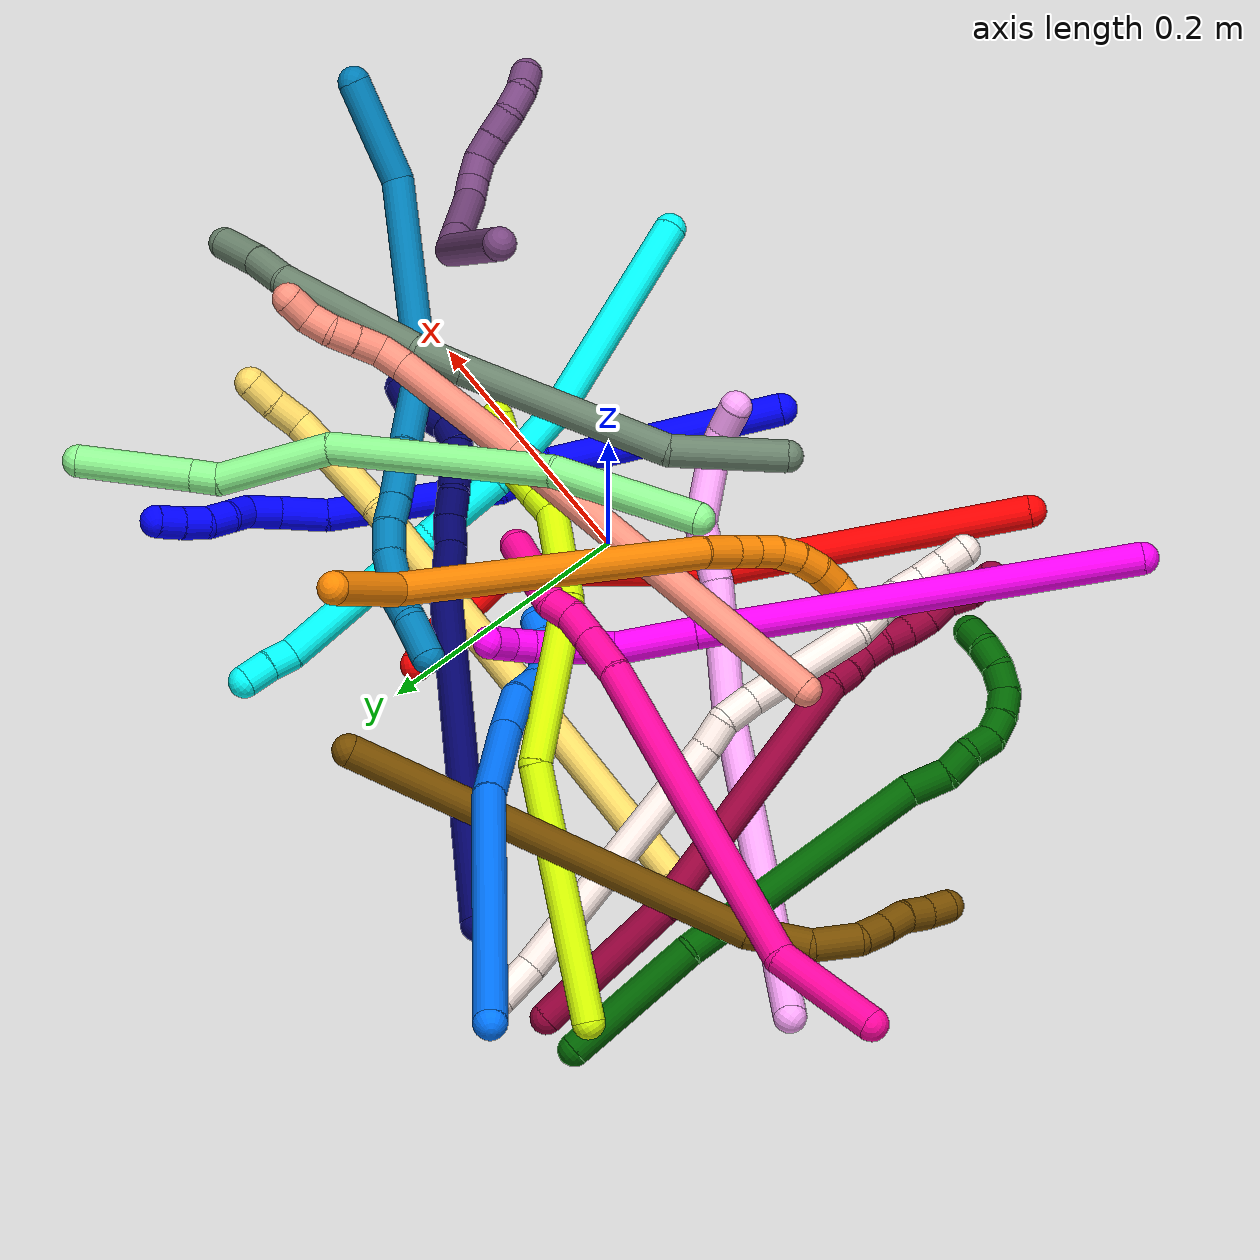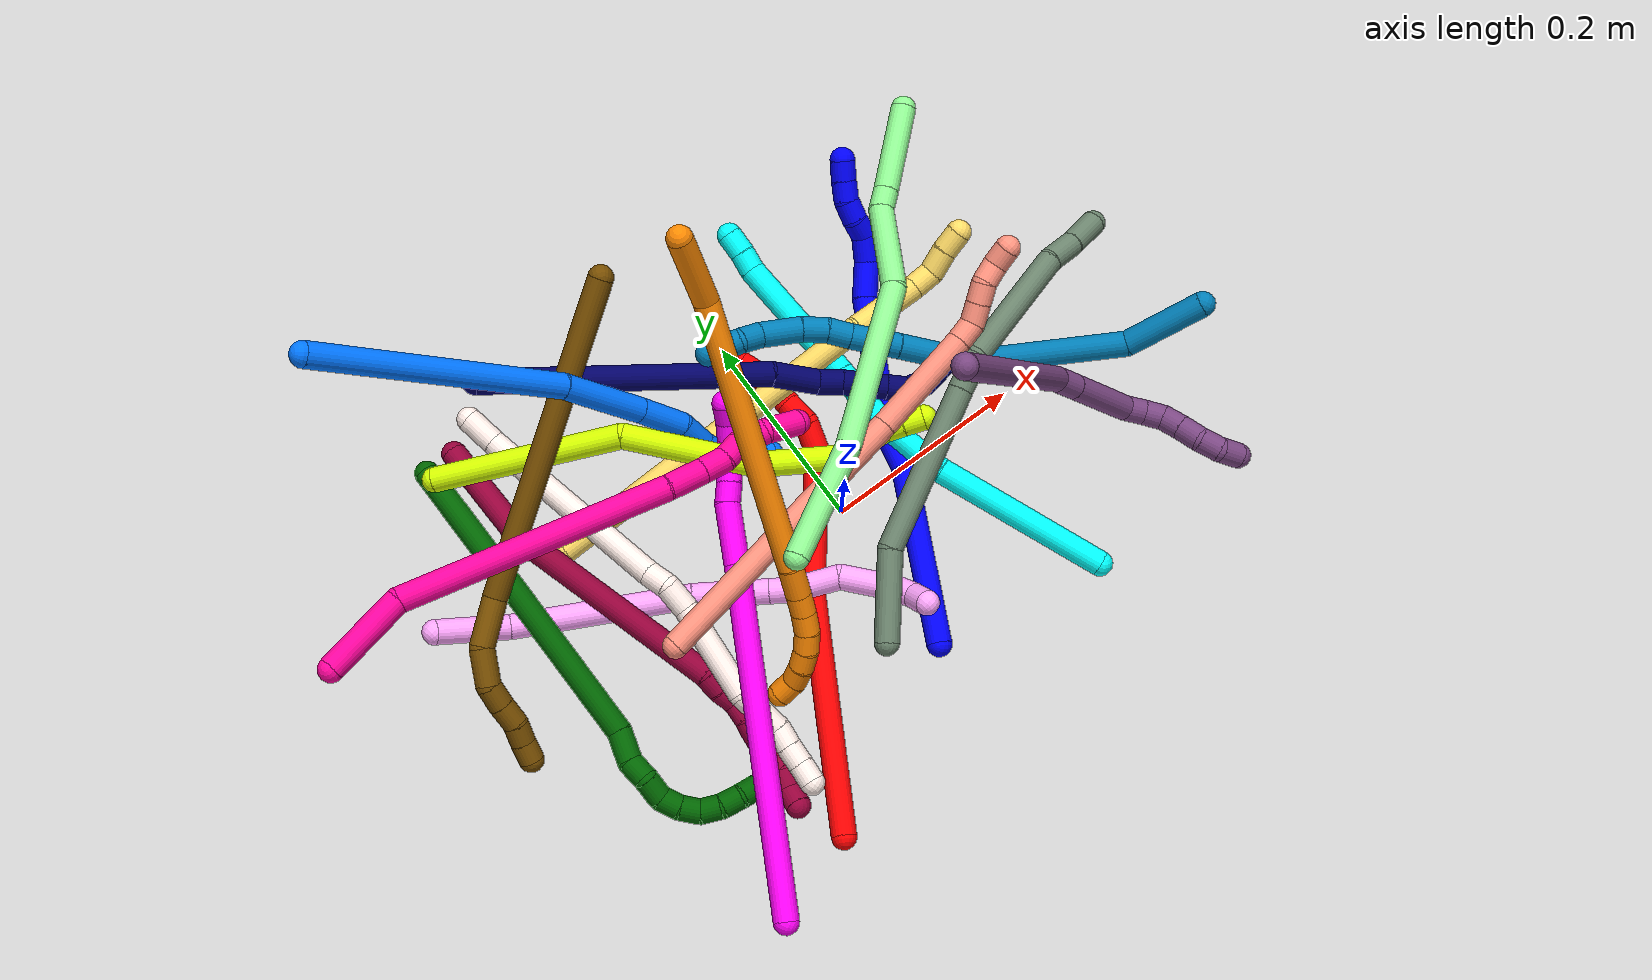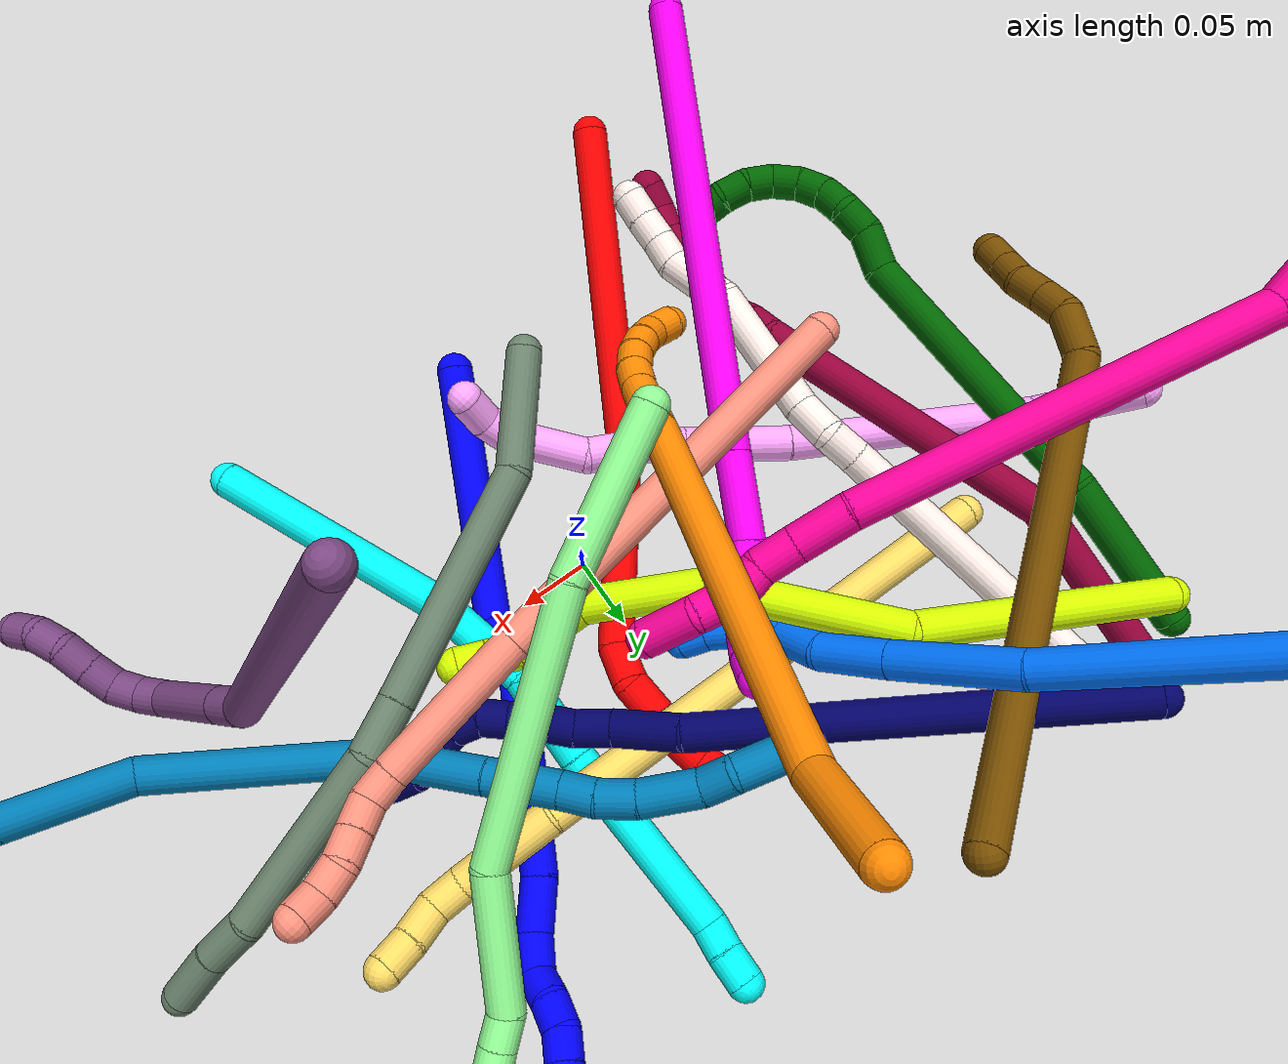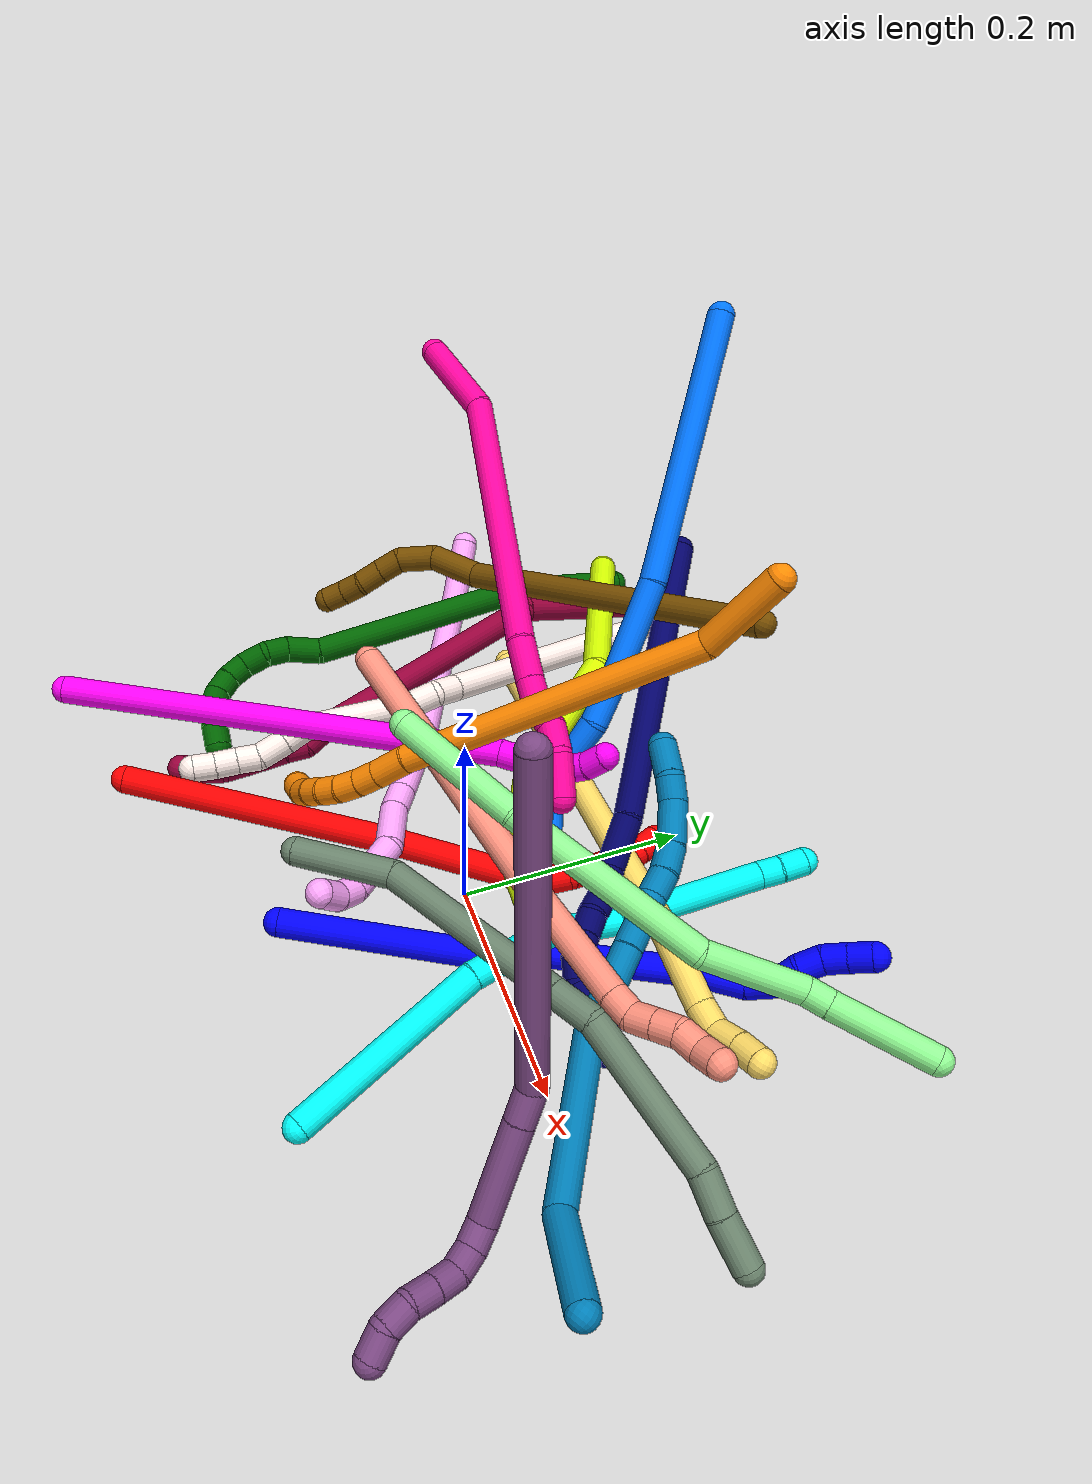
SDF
<sdf version="1.7">
 <world name="default">
  <plugin name="TubeGeneratorPlugin" filename="libtube_generator_plugin.so"/>
  <model name="photoneo_s_sensor">
   <static>1</static>
   <pose>0 0 2 1.57079 1.57079 3.14159</pose>
   <link name="link">
    <inertial><mass>0.1</mass></inertial>
    <sensor name="sensor" type="depth">
     <update_rate>30</update_rate>
     <camera>
      <horizontal_fov>1.22</horizontal_fov>
      <image><width>1920</width><height>1200</height><format>B8G8R8</format></image>
      <clip><near>0.1</near><far>4</far></clip>
      <depth_camera><output>points</output></depth_camera>
     </camera>
     <plugin name="camera_plugin" filename="libgazebo_ros_depth_camera.so">
      <baseline>0.2</baseline>
      <alwaysOn>1</alwaysOn>
      <updateRate>0.0</updateRate>
      <cameraName>camera_ir</cameraName>
      <imageTopicName>/camera/color/image_raw</imageTopicName>
      <cameraInfoTopicName>/camera/color/camera_info</cameraInfoTopicName>
      <depthImageTopicName>/camera/depth/image_raw</depthImageTopicName>
      <depthImageCameraInfoTopicName>/camera/depth/camera_info</depthImageCameraInfoTopicName>
      <pointCloudTopicName>/camera/depth/points</pointCloudTopicName>
      <frameName>fr_optical</frameName>
      <pointCloudCutoff>0.1</pointCloudCutoff>
      <pointCloudCutoffMax>2.0</pointCloudCutoffMax>
      <distortionK1>0</distortionK1>
      <distortionK2>0</distortionK2>
      <distortionK3>0</distortionK3>
      <distortionT1>0</distortionT1>
      <distortionT2>0</distortionT2>
      <CxPrime>0</CxPrime>
      <Cx>0</Cx>
      <Cy>0</Cy>
      <focalLength>0</focalLength>
      <hackBaseline>0</hackBaseline>
     </plugin>
    </sensor>
   </link>
  </model>
  <gravity>0 0 -9.8</gravity>
  <magnetic_field>6e-06 2.3e-05 -4.2e-05</magnetic_field>
  <atmosphere type="adiabatic"/>
  <physics name="default_physics" default="0" type="ode">
   <max_step_size>0.003</max_step_size>
   <real_time_factor>1</real_time_factor>
   <real_time_update_rate>1000</real_time_update_rate>
   <max_contacts>10000</max_contacts>
   <ode>
    <solver>
     <type>quick</type>
     <iters>100</iters>
     <sor>1.3</sor>
     <use_dynamic_moi_rescaling>0</use_dynamic_moi_rescaling>
    </solver>
    <constraints>
     <contact_max_correcting_vel>0</contact_max_correcting_vel>
     <contact_surface_layer>0.001</contact_surface_layer>
     <cfm>0</cfm>
     <erp>0.2</erp>
    </constraints>
   </ode>
  </physics>
  <scene><ambient>0.4 0.4 0.4 1</ambient><background>0.7 0.7 0.7 1</background><shadows>0</shadows></scene>
  <audio><device>default</device></audio>
  <spherical_coordinates>
   <surface_model>EARTH_WGS84</surface_model>
   <latitude_deg>0</latitude_deg>
   <longitude_deg>0</longitude_deg>
   <elevation>0</elevation>
   <heading_deg>0</heading_deg>
  </spherical_coordinates>
  <model name="bin">
   <static>1</static>
   <link name="bottom">
    <collision name="collision-bottom">
     <pose>0 0 -0.01 0 -0 0</pose>
     <geometry><box><size>0.8 0.6 0.02</size></box></geometry>
     <surface>
      <friction><ode><mu>100</mu><mu2>100</mu2></ode></friction>
      <contact><collide_bitmask>65535</collide_bitmask></contact>
     </surface>
    </collision>
   </link>
   <link name="west_wall">
    <collision name="collision-west_wall">
     <pose>-0.41 0 0.1 0 -0 0</pose>
     <geometry><box><size>0.02 0.6 0.2</size></box></geometry>
     <surface>
      <friction><ode><mu>100</mu><mu2>100</mu2></ode></friction>
      <contact><collide_bitmask>65535</collide_bitmask></contact>
     </surface>
    </collision>
   </link>
   <link name="east_wall">
    <collision name="collision-east_wall">
     <pose>0.41 0 0.1 0 -0 0</pose>
     <geometry><box><size>0.02 0.6 0.2</size></box></geometry>
     <surface>
      <friction><ode><mu>100</mu><mu2>100</mu2></ode></friction>
      <contact><collide_bitmask>65535</collide_bitmask></contact>
     </surface>
    </collision>
   </link>
   <link name="south_wall">
    <collision name="collision-south_wall">
     <pose>0 -0.31 0.1 0 -0 0</pose>
     <geometry><box><size>0.8 0.02 0.2</size></box></geometry>
     <surface>
      <friction><ode><mu>100</mu><mu2>100</mu2></ode></friction>
      <contact><collide_bitmask>65535</collide_bitmask></contact>
     </surface>
    </collision>
   </link>
   <link name="north_wall">
    <collision name="collision-north_wall">
     <pose>0 0.31 0.1 0 -0 0</pose>
     <geometry><box><size>0.8 0.02 0.2</size></box></geometry>
     <surface>
      <friction><ode><mu>100</mu><mu2>100</mu2></ode></friction>
      <contact><collide_bitmask>65535</collide_bitmask></contact>
     </surface>
    </collision>
   </link>
  </model>
  <model name="1">
   <static>0</static>
   <link name="1">
    <collision name="collision-cylinder-e_1_1_4">
     <pose>0.024673 0.086013 -0.006779 -1.64945 0.278531 -0.301017</pose>
     <geometry><cylinder><radius>0.0125</radius><length>0.179476</length></cylinder></geometry>
     <surface>
      <friction><ode><mu>1.16</mu><mu2>1.16</mu2><slip1>0</slip1><slip2>0</slip2></ode></friction>
      <contact><ode><kp>1e+06</kp><kd>1</kd><max_vel>0</max_vel><min_depth>0.001</min_depth></ode></contact>
     </surface>
    </collision>
    <visual name="visual-cylinder-e_1_1_4">
     <pose>0.024673 0.086013 -0.006779 -1.64945 0.278531 -0.301017</pose>
     <geometry><cylinder><radius>0.0125</radius><length>0.179476</length></cylinder></geometry>
     <material><ambient>0 0 1 1</ambient></material>
    </visual>
    <collision name="collision-cylinder-e_2_4_5">
     <pose>0.052414 0.193198 -0.010666 -1.43506 0.142604 -0.124502</pose>
     <geometry><cylinder><radius>0.0125</radius><length>0.043176</length></cylinder></geometry>
     <surface>
      <friction><ode><mu>1.16</mu><mu2>1.16</mu2><slip1>0</slip1><slip2>0</slip2></ode></friction>
      <contact><ode><kp>1e+06</kp><kd>1</kd><max_vel>0</max_vel><min_depth>0.001</min_depth></ode></contact>
     </surface>
    </collision>
    <visual name="visual-cylinder-e_2_4_5">
     <pose>0.052414 0.193198 -0.010666 -1.43506 0.142604 -0.124502</pose>
     <geometry><cylinder><radius>0.0125</radius><length>0.043176</length></cylinder></geometry>
     <material><ambient>0 0 1 1</ambient></material>
    </visual>
    <collision name="collision-cylinder-e_3_5_6">
     <pose>0.08051 0.275636 -0.01003 -1.60759 0.387593 -0.401742</pose>
     <geometry><cylinder><radius>0.0125</radius><length>0.132439</length></cylinder></geometry>
     <surface>
      <friction><ode><mu>1.16</mu><mu2>1.16</mu2><slip1>0</slip1><slip2>0</slip2></ode></friction>
      <contact><ode><kp>1e+06</kp><kd>1</kd><max_vel>0</max_vel><min_depth>0.001</min_depth></ode></contact>
     </surface>
    </collision>
    <visual name="visual-cylinder-e_3_5_6">
     <pose>0.08051 0.275636 -0.01003 -1.60759 0.387593 -0.401742</pose>
     <geometry><cylinder><radius>0.0125</radius><length>0.132439</length></cylinder></geometry>
     <material><ambient>0 0 1 1</ambient></material>
    </visual>
    <collision name="collision-cylinder-e_4_6_7">
     <pose>0.115543 0.352234 -0.014753 -1.7304 0.572308 -0.665108</pose>
     <geometry><cylinder><radius>0.0125</radius><length>0.036946</length></cylinder></geometry>
     <surface>
      <friction><ode><mu>1.16</mu><mu2>1.16</mu2><slip1>0</slip1><slip2>0</slip2></ode></friction>
      <contact><ode><kp>1e+06</kp><kd>1</kd><max_vel>0</max_vel><min_depth>0.001</min_depth></ode></contact>
     </surface>
    </collision>
    <visual name="visual-cylinder-e_4_6_7">
     <pose>0.115543 0.352234 -0.014753 -1.7304 0.572308 -0.665108</pose>
     <geometry><cylinder><radius>0.0125</radius><length>0.036946</length></cylinder></geometry>
     <material><ambient>0 0 1 1</ambient></material>
    </visual>
    <collision name="collision-cylinder-e_5_7_8">
     <pose>0.134283 0.377462 -0.014481 -1.3007 0.704883 -0.545656</pose>
     <geometry><cylinder><radius>0.0125</radius><length>0.026962</length></cylinder></geometry>
     <surface>
      <friction><ode><mu>1.16</mu><mu2>1.16</mu2><slip1>0</slip1><slip2>0</slip2></ode></friction>
      <contact><ode><kp>1e+06</kp><kd>1</kd><max_vel>0</max_vel><min_depth>0.001</min_depth></ode></contact>
     </surface>
    </collision>
    <visual name="visual-cylinder-e_5_7_8">
     <pose>0.134283 0.377462 -0.014481 -1.3007 0.704883 -0.545656</pose>
     <geometry><cylinder><radius>0.0125</radius><length>0.026962</length></cylinder></geometry>
     <material><ambient>0 0 1 1</ambient></material>
    </visual>
    <collision name="collision-cylinder-e_6_8_9">
     <pose>0.148359 0.392824 -0.005048 -0.684729 0.553612 -0.201818</pose>
     <geometry><cylinder><radius>0.0125</radius><length>0.020316</length></cylinder></geometry>
     <surface>
      <friction><ode><mu>1.16</mu><mu2>1.16</mu2><slip1>0</slip1><slip2>0</slip2></ode></friction>
      <contact><ode><kp>1e+06</kp><kd>1</kd><max_vel>0</max_vel><min_depth>0.001</min_depth></ode></contact>
     </surface>
    </collision>
    <visual name="visual-cylinder-e_6_8_9">
     <pose>0.148359 0.392824 -0.005048 -0.684729 0.553612 -0.201818</pose>
     <geometry><cylinder><radius>0.0125</radius><length>0.020316</length></cylinder></geometry>
     <material><ambient>0 0 1 1</ambient></material>
    </visual>
    <collision name="collision-cylinder-e_7_9_10">
     <pose>0.158638 0.40577 0.006432 -1.00156 0.507473 -0.281982</pose>
     <geometry><cylinder><radius>0.0125</radius><length>0.020325</length></cylinder></geometry>
     <surface>
      <friction><ode><mu>1.16</mu><mu2>1.16</mu2><slip1>0</slip1><slip2>0</slip2></ode></friction>
      <contact><ode><kp>1e+06</kp><kd>1</kd><max_vel>0</max_vel><min_depth>0.001</min_depth></ode></contact>
     </surface>
    </collision>
    <visual name="visual-cylinder-e_7_9_10">
     <pose>0.158638 0.40577 0.006432 -1.00156 0.507473 -0.281982</pose>
     <geometry><cylinder><radius>0.0125</radius><length>0.020325</length></cylinder></geometry>
     <material><ambient>0 0 1 1</ambient></material>
    </visual>
    <collision name="collision-cylinder-e_8_10_11">
     <pose>0.169825 0.420959 0.01314 -1.32652 0.666435 -0.528247</pose>
     <geometry><cylinder><radius>0.0125</radius><length>0.020214</length></cylinder></geometry>
     <surface>
      <friction><ode><mu>1.16</mu><mu2>1.16</mu2><slip1>0</slip1><slip2>0</slip2></ode></friction>
      <contact><ode><kp>1e+06</kp><kd>1</kd><max_vel>0</max_vel><min_depth>0.001</min_depth></ode></contact>
     </surface>
    </collision>
    <visual name="visual-cylinder-e_8_10_11">
     <pose>0.169825 0.420959 0.01314 -1.32652 0.666435 -0.528247</pose>
     <geometry><cylinder><radius>0.0125</radius><length>0.020214</length></cylinder></geometry>
     <material><ambient>0 0 1 1</ambient></material>
    </visual>
    <collision name="collision-cylinder-e_9_11_2">
     <pose>0.182886 0.435883 0.016789 -1.33581 0.742875 -0.59623</pose>
     <geometry><cylinder><radius>0.0125</radius><length>0.020146</length></cylinder></geometry>
     <surface>
      <friction><ode><mu>1.16</mu><mu2>1.16</mu2><slip1>0</slip1><slip2>0</slip2></ode></friction>
      <contact><ode><kp>1e+06</kp><kd>1</kd><max_vel>0</max_vel><min_depth>0.001</min_depth></ode></contact>
     </surface>
    </collision>
    <visual name="visual-cylinder-e_9_11_2">
     <pose>0.182886 0.435883 0.016789 -1.33581 0.742875 -0.59623</pose>
     <geometry><cylinder><radius>0.0125</radius><length>0.020146</length></cylinder></geometry>
     <material><ambient>0 0 1 1</ambient></material>
    </visual>
    <collision name="collision-sphere-2">
     <pose>0.189699 0.443098 0.018516 0 -0 0</pose>
     <geometry><sphere><radius>0.0125</radius></sphere></geometry>
     <surface>
      <friction><ode><mu>1.16</mu><mu2>1.16</mu2><slip1>0</slip1><slip2>0</slip2></ode></friction>
      <contact><ode><kp>1e+06</kp><kd>1</kd><max_vel>0</max_vel><min_depth>0.001</min_depth></ode></contact>
     </surface>
    </collision>
    <visual name="visual-sphere-2">
     <pose>0.189699 0.443098 0.018516 0 -0 0</pose>
     <geometry><sphere><radius>0.0125</radius></sphere></geometry>
     <material><ambient>0 0 1 1</ambient></material>
    </visual>
    <collision name="collision-sphere-11">
     <pose>0.176073 0.428668 0.015062 0 -0 0</pose>
     <geometry><sphere><radius>0.0125</radius></sphere></geometry>
     <surface>
      <friction><ode><mu>1.16</mu><mu2>1.16</mu2><slip1>0</slip1><slip2>0</slip2></ode></friction>
      <contact><ode><kp>1e+06</kp><kd>1</kd><max_vel>0</max_vel><min_depth>0.001</min_depth></ode></contact>
     </surface>
    </collision>
    <visual name="visual-sphere-11">
     <pose>0.176073 0.428668 0.015062 0 -0 0</pose>
     <geometry><sphere><radius>0.0125</radius></sphere></geometry>
     <material><ambient>0 0 1 1</ambient></material>
    </visual>
    <collision name="collision-sphere-10">
     <pose>0.163577 0.413251 0.011219 0 -0 0</pose>
     <geometry><sphere><radius>0.0125</radius></sphere></geometry>
     <surface>
      <friction><ode><mu>1.16</mu><mu2>1.16</mu2><slip1>0</slip1><slip2>0</slip2></ode></friction>
      <contact><ode><kp>1e+06</kp><kd>1</kd><max_vel>0</max_vel><min_depth>0.001</min_depth></ode></contact>
     </surface>
    </collision>
    <visual name="visual-sphere-10">
     <pose>0.163577 0.413251 0.011219 0 -0 0</pose>
     <geometry><sphere><radius>0.0125</radius></sphere></geometry>
     <material><ambient>0 0 1 1</ambient></material>
    </visual>
    <collision name="collision-sphere-9">
     <pose>0.1537 0.398289 0.001645 0 -0 0</pose>
     <geometry><sphere><radius>0.0125</radius></sphere></geometry>
     <surface>
      <friction><ode><mu>1.16</mu><mu2>1.16</mu2><slip1>0</slip1><slip2>0</slip2></ode></friction>
      <contact><ode><kp>1e+06</kp><kd>1</kd><max_vel>0</max_vel><min_depth>0.001</min_depth></ode></contact>
     </surface>
    </collision>
    <visual name="visual-sphere-9">
     <pose>0.1537 0.398289 0.001645 0 -0 0</pose>
     <geometry><sphere><radius>0.0125</radius></sphere></geometry>
     <material><ambient>0 0 1 1</ambient></material>
    </visual>
    <collision name="collision-sphere-4">
     <pose>0.049346 0.172025 -0.013558 0 -0 0</pose>
     <geometry><sphere><radius>0.0125</radius></sphere></geometry>
     <surface>
      <friction><ode><mu>1.16</mu><mu2>1.16</mu2><slip1>0</slip1><slip2>0</slip2></ode></friction>
      <contact><ode><kp>1e+06</kp><kd>1</kd><max_vel>0</max_vel><min_depth>0.001</min_depth></ode></contact>
     </surface>
    </collision>
    <visual name="visual-sphere-4">
     <pose>0.049346 0.172025 -0.013558 0 -0 0</pose>
     <geometry><sphere><radius>0.0125</radius></sphere></geometry>
     <material><ambient>0 0 1 1</ambient></material>
    </visual>
    <collision name="collision-sphere-1">
     <geometry><sphere><radius>0.0125</radius></sphere></geometry>
     <surface>
      <friction><ode><mu>1.16</mu><mu2>1.16</mu2><slip1>0</slip1><slip2>0</slip2></ode></friction>
      <contact><ode><kp>1e+06</kp><kd>1</kd><max_vel>0</max_vel><min_depth>0.001</min_depth></ode></contact>
     </surface>
    </collision>
    <visual name="visual-sphere-1">
     <geometry><sphere><radius>0.0125</radius></sphere></geometry>
     <material><ambient>0 0 1 1</ambient></material>
    </visual>
    <collision name="collision-sphere-8">
     <pose>0.143018 0.387358 -0.011742 0 -0 0</pose>
     <geometry><sphere><radius>0.0125</radius></sphere></geometry>
     <surface>
      <friction><ode><mu>1.16</mu><mu2>1.16</mu2><slip1>0</slip1><slip2>0</slip2></ode></friction>
      <contact><ode><kp>1e+06</kp><kd>1</kd><max_vel>0</max_vel><min_depth>0.001</min_depth></ode></contact>
     </surface>
    </collision>
    <visual name="visual-sphere-8">
     <pose>0.143018 0.387358 -0.011742 0 -0 0</pose>
     <geometry><sphere><radius>0.0125</radius></sphere></geometry>
     <material><ambient>0 0 1 1</ambient></material>
    </visual>
    <collision name="collision-sphere-5">
     <pose>0.055482 0.21437 -0.007775 0 -0 0</pose>
     <geometry><sphere><radius>0.0125</radius></sphere></geometry>
     <surface>
      <friction><ode><mu>1.16</mu><mu2>1.16</mu2><slip1>0</slip1><slip2>0</slip2></ode></friction>
      <contact><ode><kp>1e+06</kp><kd>1</kd><max_vel>0</max_vel><min_depth>0.001</min_depth></ode></contact>
     </surface>
    </collision>
    <visual name="visual-sphere-5">
     <pose>0.055482 0.21437 -0.007775 0 -0 0</pose>
     <geometry><sphere><radius>0.0125</radius></sphere></geometry>
     <material><ambient>0 0 1 1</ambient></material>
    </visual>
    <collision name="collision-sphere-6">
     <pose>0.105539 0.336902 -0.012285 0 -0 0</pose>
     <geometry><sphere><radius>0.0125</radius></sphere></geometry>
     <surface>
      <friction><ode><mu>1.16</mu><mu2>1.16</mu2><slip1>0</slip1><slip2>0</slip2></ode></friction>
      <contact><ode><kp>1e+06</kp><kd>1</kd><max_vel>0</max_vel><min_depth>0.001</min_depth></ode></contact>
     </surface>
    </collision>
    <visual name="visual-sphere-6">
     <pose>0.105539 0.336902 -0.012285 0 -0 0</pose>
     <geometry><sphere><radius>0.0125</radius></sphere></geometry>
     <material><ambient>0 0 1 1</ambient></material>
    </visual>
    <collision name="collision-sphere-7">
     <pose>0.125548 0.367566 -0.017221 0 -0 0</pose>
     <geometry><sphere><radius>0.0125</radius></sphere></geometry>
     <surface>
      <friction><ode><mu>1.16</mu><mu2>1.16</mu2><slip1>0</slip1><slip2>0</slip2></ode></friction>
      <contact><ode><kp>1e+06</kp><kd>1</kd><max_vel>0</max_vel><min_depth>0.001</min_depth></ode></contact>
     </surface>
    </collision>
    <visual name="visual-sphere-7">
     <pose>0.125548 0.367566 -0.017221 0 -0 0</pose>
     <geometry><sphere><radius>0.0125</radius></sphere></geometry>
     <material><ambient>0 0 1 1</ambient></material>
    </visual>
    <inertial>
     <pose>0.077198 0.233986 -0.006618 0 -0 0</pose>
     <mass>0.5</mass>
     <inertia>
      <ixx>0.000433</ixx>
      <ixy>0</ixy>
      <ixz>0</ixz>
      <iyy>-0.00015</iyy>
      <iyz>0</iyz>
      <izz>-0.000889</izz>
     </inertia>
    </inertial>
   </link>
   <pose>-0.003481 -0.162973 0.033165 -0.406486 -0.824374 0.096579</pose>
  </model>
  <model name="2">
   <static>0</static>
   <link name="2">
    <collision name="collision-cylinder-e_1_1_4">
     <pose>0.003135 0.002374 -0.119457 -3.12172 0.026232 -1.84513</pose>
     <geometry><cylinder><radius>0.0125</radius><length>0.239044</length></cylinder></geometry>
     <surface>
      <friction><ode><mu>1.16</mu><mu2>1.16</mu2><slip1>0</slip1><slip2>0</slip2></ode></friction>
      <contact><ode><kp>1e+06</kp><kd>1</kd><max_vel>0</max_vel><min_depth>0.001</min_depth></ode></contact>
     </surface>
    </collision>
    <visual name="visual-cylinder-e_1_1_4">
     <pose>0.003135 0.002374 -0.119457 -3.12172 0.026232 -1.84513</pose>
     <geometry><cylinder><radius>0.0125</radius><length>0.239044</length></cylinder></geometry>
     <material><ambient>1 0 0 1</ambient></material>
    </visual>
    <collision name="collision-cylinder-e_2_4_5">
     <pose>0.021558 0.000633 -0.308298 3.08235 0.216504 2.60927</pose>
     <geometry><cylinder><radius>0.0125</radius><length>0.142333</length></cylinder></geometry>
     <surface>
      <friction><ode><mu>1.16</mu><mu2>1.16</mu2><slip1>0</slip1><slip2>0</slip2></ode></friction>
      <contact><ode><kp>1e+06</kp><kd>1</kd><max_vel>0</max_vel><min_depth>0.001</min_depth></ode></contact>
     </surface>
    </collision>
    <visual name="visual-cylinder-e_2_4_5">
     <pose>0.021558 0.000633 -0.308298 3.08235 0.216504 2.60927</pose>
     <geometry><cylinder><radius>0.0125</radius><length>0.142333</length></cylinder></geometry>
     <material><ambient>1 0 0 1</ambient></material>
    </visual>
    <collision name="collision-cylinder-e_3_5_6">
     <pose>0.040534 0.00211 -0.390191 -2.7212 0.26295 -1.10974</pose>
     <geometry><cylinder><radius>0.0125</radius><length>0.02838</length></cylinder></geometry>
     <surface>
      <friction><ode><mu>1.16</mu><mu2>1.16</mu2><slip1>0</slip1><slip2>0</slip2></ode></friction>
      <contact><ode><kp>1e+06</kp><kd>1</kd><max_vel>0</max_vel><min_depth>0.001</min_depth></ode></contact>
     </surface>
    </collision>
    <visual name="visual-cylinder-e_3_5_6">
     <pose>0.040534 0.00211 -0.390191 -2.7212 0.26295 -1.10974</pose>
     <geometry><cylinder><radius>0.0125</radius><length>0.02838</length></cylinder></geometry>
     <material><ambient>1 0 0 1</ambient></material>
    </visual>
    <collision name="collision-cylinder-e_4_6_7">
     <pose>0.041151 0.014997 -0.413981 -2.56757 -0.22473 0.730309</pose>
     <geometry><cylinder><radius>0.0125</radius><length>0.027562</length></cylinder></geometry>
     <surface>
      <friction><ode><mu>1.16</mu><mu2>1.16</mu2><slip1>0</slip1><slip2>0</slip2></ode></friction>
      <contact><ode><kp>1e+06</kp><kd>1</kd><max_vel>0</max_vel><min_depth>0.001</min_depth></ode></contact>
     </surface>
    </collision>
    <visual name="visual-cylinder-e_4_6_7">
     <pose>0.041151 0.014997 -0.413981 -2.56757 -0.22473 0.730309</pose>
     <geometry><cylinder><radius>0.0125</radius><length>0.027562</length></cylinder></geometry>
     <material><ambient>1 0 0 1</ambient></material>
    </visual>
    <collision name="collision-cylinder-e_5_7_8">
     <pose>0.036769 0.027801 -0.433629 -2.55933 -0.130137 0.428248</pose>
     <geometry><cylinder><radius>0.0125</radius><length>0.020207</length></cylinder></geometry>
     <surface>
      <friction><ode><mu>1.16</mu><mu2>1.16</mu2><slip1>0</slip1><slip2>0</slip2></ode></friction>
      <contact><ode><kp>1e+06</kp><kd>1</kd><max_vel>0</max_vel><min_depth>0.001</min_depth></ode></contact>
     </surface>
    </collision>
    <visual name="visual-cylinder-e_5_7_8">
     <pose>0.036769 0.027801 -0.433629 -2.55933 -0.130137 0.428248</pose>
     <geometry><cylinder><radius>0.0125</radius><length>0.020207</length></cylinder></geometry>
     <material><ambient>1 0 0 1</ambient></material>
    </visual>
    <collision name="collision-cylinder-e_6_8_9">
     <pose>0.032513 0.039798 -0.450021 -2.46173 -0.278014 0.753425</pose>
     <geometry><cylinder><radius>0.0125</radius><length>0.021462</length></cylinder></geometry>
     <surface>
      <friction><ode><mu>1.16</mu><mu2>1.16</mu2><slip1>0</slip1><slip2>0</slip2></ode></friction>
      <contact><ode><kp>1e+06</kp><kd>1</kd><max_vel>0</max_vel><min_depth>0.001</min_depth></ode></contact>
     </surface>
    </collision>
    <visual name="visual-cylinder-e_6_8_9">
     <pose>0.032513 0.039798 -0.450021 -2.46173 -0.278014 0.753425</pose>
     <geometry><cylinder><radius>0.0125</radius><length>0.021462</length></cylinder></geometry>
     <material><ambient>1 0 0 1</ambient></material>
    </visual>
    <collision name="collision-cylinder-e_7_9_2">
     <pose>0.027545 0.054251 -0.464589 -2.25842 -0.19377 0.405542</pose>
     <geometry><cylinder><radius>0.0125</radius><length>0.021012</length></cylinder></geometry>
     <surface>
      <friction><ode><mu>1.16</mu><mu2>1.16</mu2><slip1>0</slip1><slip2>0</slip2></ode></friction>
      <contact><ode><kp>1e+06</kp><kd>1</kd><max_vel>0</max_vel><min_depth>0.001</min_depth></ode></contact>
     </surface>
    </collision>
    <visual name="visual-cylinder-e_7_9_2">
     <pose>0.027545 0.054251 -0.464589 -2.25842 -0.19377 0.405542</pose>
     <geometry><cylinder><radius>0.0125</radius><length>0.021012</length></cylinder></geometry>
     <material><ambient>1 0 0 1</ambient></material>
    </visual>
    <collision name="collision-sphere-2">
     <pose>0.025522 0.062218 -0.471133 0 -0 0</pose>
     <geometry><sphere><radius>0.0125</radius></sphere></geometry>
     <surface>
      <friction><ode><mu>1.16</mu><mu2>1.16</mu2><slip1>0</slip1><slip2>0</slip2></ode></friction>
      <contact><ode><kp>1e+06</kp><kd>1</kd><max_vel>0</max_vel><min_depth>0.001</min_depth></ode></contact>
     </surface>
    </collision>
    <visual name="visual-sphere-2">
     <pose>0.025522 0.062218 -0.471133 0 -0 0</pose>
     <geometry><sphere><radius>0.0125</radius></sphere></geometry>
     <material><ambient>1 0 0 1</ambient></material>
    </visual>
    <collision name="collision-sphere-9">
     <pose>0.029568 0.046285 -0.458046 0 -0 0</pose>
     <geometry><sphere><radius>0.0125</radius></sphere></geometry>
     <surface>
      <friction><ode><mu>1.16</mu><mu2>1.16</mu2><slip1>0</slip1><slip2>0</slip2></ode></friction>
      <contact><ode><kp>1e+06</kp><kd>1</kd><max_vel>0</max_vel><min_depth>0.001</min_depth></ode></contact>
     </surface>
    </collision>
    <visual name="visual-sphere-9">
     <pose>0.029568 0.046285 -0.458046 0 -0 0</pose>
     <geometry><sphere><radius>0.0125</radius></sphere></geometry>
     <material><ambient>1 0 0 1</ambient></material>
    </visual>
    <collision name="collision-sphere-4">
     <pose>0.00627 0.004748 -0.238915 0 -0 0</pose>
     <geometry><sphere><radius>0.0125</radius></sphere></geometry>
     <surface>
      <friction><ode><mu>1.16</mu><mu2>1.16</mu2><slip1>0</slip1><slip2>0</slip2></ode></friction>
      <contact><ode><kp>1e+06</kp><kd>1</kd><max_vel>0</max_vel><min_depth>0.001</min_depth></ode></contact>
     </surface>
    </collision>
    <visual name="visual-sphere-4">
     <pose>0.00627 0.004748 -0.238915 0 -0 0</pose>
     <geometry><sphere><radius>0.0125</radius></sphere></geometry>
     <material><ambient>1 0 0 1</ambient></material>
    </visual>
    <collision name="collision-sphere-1">
     <geometry><sphere><radius>0.0125</radius></sphere></geometry>
     <surface>
      <friction><ode><mu>1.16</mu><mu2>1.16</mu2><slip1>0</slip1><slip2>0</slip2></ode></friction>
      <contact><ode><kp>1e+06</kp><kd>1</kd><max_vel>0</max_vel><min_depth>0.001</min_depth></ode></contact>
     </surface>
    </collision>
    <visual name="visual-sphere-1">
     <geometry><sphere><radius>0.0125</radius></sphere></geometry>
     <material><ambient>1 0 0 1</ambient></material>
    </visual>
    <collision name="collision-sphere-8">
     <pose>0.035458 0.03331 -0.441997 0 -0 0</pose>
     <geometry><sphere><radius>0.0125</radius></sphere></geometry>
     <surface>
      <friction><ode><mu>1.16</mu><mu2>1.16</mu2><slip1>0</slip1><slip2>0</slip2></ode></friction>
      <contact><ode><kp>1e+06</kp><kd>1</kd><max_vel>0</max_vel><min_depth>0.001</min_depth></ode></contact>
     </surface>
    </collision>
    <visual name="visual-sphere-8">
     <pose>0.035458 0.03331 -0.441997 0 -0 0</pose>
     <geometry><sphere><radius>0.0125</radius></sphere></geometry>
     <material><ambient>1 0 0 1</ambient></material>
    </visual>
    <collision name="collision-sphere-5">
     <pose>0.036845 -0.003482 -0.377681 0 -0 0</pose>
     <geometry><sphere><radius>0.0125</radius></sphere></geometry>
     <surface>
      <friction><ode><mu>1.16</mu><mu2>1.16</mu2><slip1>0</slip1><slip2>0</slip2></ode></friction>
      <contact><ode><kp>1e+06</kp><kd>1</kd><max_vel>0</max_vel><min_depth>0.001</min_depth></ode></contact>
     </surface>
    </collision>
    <visual name="visual-sphere-5">
     <pose>0.036845 -0.003482 -0.377681 0 -0 0</pose>
     <geometry><sphere><radius>0.0125</radius></sphere></geometry>
     <material><ambient>1 0 0 1</ambient></material>
    </visual>
    <collision name="collision-sphere-6">
     <pose>0.044222 0.007702 -0.4027 0 -0 0</pose>
     <geometry><sphere><radius>0.0125</radius></sphere></geometry>
     <surface>
      <friction><ode><mu>1.16</mu><mu2>1.16</mu2><slip1>0</slip1><slip2>0</slip2></ode></friction>
      <contact><ode><kp>1e+06</kp><kd>1</kd><max_vel>0</max_vel><min_depth>0.001</min_depth></ode></contact>
     </surface>
    </collision>
    <visual name="visual-sphere-6">
     <pose>0.044222 0.007702 -0.4027 0 -0 0</pose>
     <geometry><sphere><radius>0.0125</radius></sphere></geometry>
     <material><ambient>1 0 0 1</ambient></material>
    </visual>
    <collision name="collision-sphere-7">
     <pose>0.03808 0.022292 -0.425262 0 -0 0</pose>
     <geometry><sphere><radius>0.0125</radius></sphere></geometry>
     <surface>
      <friction><ode><mu>1.16</mu><mu2>1.16</mu2><slip1>0</slip1><slip2>0</slip2></ode></friction>
      <contact><ode><kp>1e+06</kp><kd>1</kd><max_vel>0</max_vel><min_depth>0.001</min_depth></ode></contact>
     </surface>
    </collision>
    <visual name="visual-sphere-7">
     <pose>0.03808 0.022292 -0.425262 0 -0 0</pose>
     <geometry><sphere><radius>0.0125</radius></sphere></geometry>
     <material><ambient>1 0 0 1</ambient></material>
    </visual>
    <inertial>
     <pose>0.016244 0.007373 -0.246206 0 -0 0</pose>
     <mass>0.5</mass>
     <inertia>
      <ixx>-0.001489</ixx>
      <ixy>0</ixy>
      <ixz>0</ixz>
      <iyy>-0.000457</iyy>
      <iyz>0</iyz>
      <izz>-0.000133</izz>
     </inertia>
    </inertial>
   </link>
   <pose>-0.186689 -0.257071 0.044498 1.17923 -1.11097 -0.160621</pose>
  </model>
  <model name="3">
   <static>0</static>
   <link name="3">
    <collision name="collision-cylinder-e_1_1_4">
     <pose>-0.033633 0.081438 0.017125 -1.36353 -0.384082 0.313023</pose>
     <geometry><cylinder><radius>0.0125</radius><length>0.179517</length></cylinder></geometry>
     <surface>
      <friction><ode><mu>1.16</mu><mu2>1.16</mu2><slip1>0</slip1><slip2>0</slip2></ode></friction>
      <contact><ode><kp>1e+06</kp><kd>1</kd><max_vel>0</max_vel><min_depth>0.001</min_depth></ode></contact>
     </surface>
    </collision>
    <visual name="visual-cylinder-e_1_1_4">
     <pose>-0.033633 0.081438 0.017125 -1.36353 -0.384082 0.313023</pose>
     <geometry><cylinder><radius>0.0125</radius><length>0.179517</length></cylinder></geometry>
     <material><ambient>0.003922 1 0.996078 1</ambient></material>
    </visual>
    <collision name="collision-cylinder-e_2_4_5">
     <pose>-0.074757 0.198504 0.043616 -1.31376 -0.200595 0.154893</pose>
     <geometry><cylinder><radius>0.0125</radius><length>0.075186</length></cylinder></geometry>
     <surface>
      <friction><ode><mu>1.16</mu><mu2>1.16</mu2><slip1>0</slip1><slip2>0</slip2></ode></friction>
      <contact><ode><kp>1e+06</kp><kd>1</kd><max_vel>0</max_vel><min_depth>0.001</min_depth></ode></contact>
     </surface>
    </collision>
    <visual name="visual-cylinder-e_2_4_5">
     <pose>-0.074757 0.198504 0.043616 -1.31376 -0.200595 0.154893</pose>
     <geometry><cylinder><radius>0.0125</radius><length>0.075186</length></cylinder></geometry>
     <material><ambient>0.003922 1 0.996078 1</ambient></material>
    </visual>
    <collision name="collision-cylinder-e_3_5_6">
     <pose>-0.078251 0.26566 0.059979 -1.35234 0.123132 -0.098839</pose>
     <geometry><cylinder><radius>0.0125</radius><length>0.065081</length></cylinder></geometry>
     <surface>
      <friction><ode><mu>1.16</mu><mu2>1.16</mu2><slip1>0</slip1><slip2>0</slip2></ode></friction>
      <contact><ode><kp>1e+06</kp><kd>1</kd><max_vel>0</max_vel><min_depth>0.001</min_depth></ode></contact>
     </surface>
    </collision>
    <visual name="visual-cylinder-e_3_5_6">
     <pose>-0.078251 0.26566 0.059979 -1.35234 0.123132 -0.098839</pose>
     <geometry><cylinder><radius>0.0125</radius><length>0.065081</length></cylinder></geometry>
     <material><ambient>0.003922 1 0.996078 1</ambient></material>
    </visual>
    <collision name="collision-cylinder-e_4_6_7">
     <pose>-0.075102 0.362985 0.087223 -1.27231 -0.012316 0.009097</pose>
     <geometry><cylinder><radius>0.0125</radius><length>0.137696</length></cylinder></geometry>
     <surface>
      <friction><ode><mu>1.16</mu><mu2>1.16</mu2><slip1>0</slip1><slip2>0</slip2></ode></friction>
      <contact><ode><kp>1e+06</kp><kd>1</kd><max_vel>0</max_vel><min_depth>0.001</min_depth></ode></contact>
     </surface>
    </collision>
    <visual name="visual-cylinder-e_4_6_7">
     <pose>-0.075102 0.362985 0.087223 -1.27231 -0.012316 0.009097</pose>
     <geometry><cylinder><radius>0.0125</radius><length>0.137696</length></cylinder></geometry>
     <material><ambient>0.003922 1 0.996078 1</ambient></material>
    </visual>
    <collision name="collision-cylinder-e_5_7_8">
     <pose>-0.076036 0.437325 0.112959 -0.999481 -0.008488 0.004634</pose>
     <geometry><cylinder><radius>0.0125</radius><length>0.02031</length></cylinder></geometry>
     <surface>
      <friction><ode><mu>1.16</mu><mu2>1.16</mu2><slip1>0</slip1><slip2>0</slip2></ode></friction>
      <contact><ode><kp>1e+06</kp><kd>1</kd><max_vel>0</max_vel><min_depth>0.001</min_depth></ode></contact>
     </surface>
    </collision>
    <visual name="visual-cylinder-e_5_7_8">
     <pose>-0.076036 0.437325 0.112959 -0.999481 -0.008488 0.004634</pose>
     <geometry><cylinder><radius>0.0125</radius><length>0.02031</length></cylinder></geometry>
     <material><ambient>0.003922 1 0.996078 1</ambient></material>
    </visual>
    <collision name="collision-cylinder-e_6_8_2">
     <pose>-0.076661 0.45577 0.123448 -1.10334 -0.04856 0.029887</pose>
     <geometry><cylinder><radius>0.0125</radius><length>0.022211</length></cylinder></geometry>
     <surface>
      <friction><ode><mu>1.16</mu><mu2>1.16</mu2><slip1>0</slip1><slip2>0</slip2></ode></friction>
      <contact><ode><kp>1e+06</kp><kd>1</kd><max_vel>0</max_vel><min_depth>0.001</min_depth></ode></contact>
     </surface>
    </collision>
    <visual name="visual-cylinder-e_6_8_2">
     <pose>-0.076661 0.45577 0.123448 -1.10334 -0.04856 0.029887</pose>
     <geometry><cylinder><radius>0.0125</radius><length>0.022211</length></cylinder></geometry>
     <material><ambient>0.003922 1 0.996078 1</ambient></material>
    </visual>
    <collision name="collision-sphere-2">
     <pose>-0.0772 0.465672 0.128447 0 -0 0</pose>
     <geometry><sphere><radius>0.0125</radius></sphere></geometry>
     <surface>
      <friction><ode><mu>1.16</mu><mu2>1.16</mu2><slip1>0</slip1><slip2>0</slip2></ode></friction>
      <contact><ode><kp>1e+06</kp><kd>1</kd><max_vel>0</max_vel><min_depth>0.001</min_depth></ode></contact>
     </surface>
    </collision>
    <visual name="visual-sphere-2">
     <pose>-0.0772 0.465672 0.128447 0 -0 0</pose>
     <geometry><sphere><radius>0.0125</radius></sphere></geometry>
     <material><ambient>0.003922 1 0.996078 1</ambient></material>
    </visual>
    <collision name="collision-sphere-4">
     <pose>-0.067266 0.162876 0.034251 0 -0 0</pose>
     <geometry><sphere><radius>0.0125</radius></sphere></geometry>
     <surface>
      <friction><ode><mu>1.16</mu><mu2>1.16</mu2><slip1>0</slip1><slip2>0</slip2></ode></friction>
      <contact><ode><kp>1e+06</kp><kd>1</kd><max_vel>0</max_vel><min_depth>0.001</min_depth></ode></contact>
     </surface>
    </collision>
    <visual name="visual-sphere-4">
     <pose>-0.067266 0.162876 0.034251 0 -0 0</pose>
     <geometry><sphere><radius>0.0125</radius></sphere></geometry>
     <material><ambient>0.003922 1 0.996078 1</ambient></material>
    </visual>
    <collision name="collision-sphere-1">
     <geometry><sphere><radius>0.0125</radius></sphere></geometry>
     <surface>
      <friction><ode><mu>1.16</mu><mu2>1.16</mu2><slip1>0</slip1><slip2>0</slip2></ode></friction>
      <contact><ode><kp>1e+06</kp><kd>1</kd><max_vel>0</max_vel><min_depth>0.001</min_depth></ode></contact>
     </surface>
    </collision>
    <visual name="visual-sphere-1">
     <geometry><sphere><radius>0.0125</radius></sphere></geometry>
     <material><ambient>0.003922 1 0.996078 1</ambient></material>
    </visual>
    <collision name="collision-sphere-8">
     <pose>-0.076122 0.445867 0.11845 0 -0 0</pose>
     <geometry><sphere><radius>0.0125</radius></sphere></geometry>
     <surface>
      <friction><ode><mu>1.16</mu><mu2>1.16</mu2><slip1>0</slip1><slip2>0</slip2></ode></friction>
      <contact><ode><kp>1e+06</kp><kd>1</kd><max_vel>0</max_vel><min_depth>0.001</min_depth></ode></contact>
     </surface>
    </collision>
    <visual name="visual-sphere-8">
     <pose>-0.076122 0.445867 0.11845 0 -0 0</pose>
     <geometry><sphere><radius>0.0125</radius></sphere></geometry>
     <material><ambient>0.003922 1 0.996078 1</ambient></material>
    </visual>
    <collision name="collision-sphere-5">
     <pose>-0.082247 0.234133 0.05298 0 -0 0</pose>
     <geometry><sphere><radius>0.0125</radius></sphere></geometry>
     <surface>
      <friction><ode><mu>1.16</mu><mu2>1.16</mu2><slip1>0</slip1><slip2>0</slip2></ode></friction>
      <contact><ode><kp>1e+06</kp><kd>1</kd><max_vel>0</max_vel><min_depth>0.001</min_depth></ode></contact>
     </surface>
    </collision>
    <visual name="visual-sphere-5">
     <pose>-0.082247 0.234133 0.05298 0 -0 0</pose>
     <geometry><sphere><radius>0.0125</radius></sphere></geometry>
     <material><ambient>0.003922 1 0.996078 1</ambient></material>
    </visual>
    <collision name="collision-sphere-6">
     <pose>-0.074254 0.297186 0.066978 0 -0 0</pose>
     <geometry><sphere><radius>0.0125</radius></sphere></geometry>
     <surface>
      <friction><ode><mu>1.16</mu><mu2>1.16</mu2><slip1>0</slip1><slip2>0</slip2></ode></friction>
      <contact><ode><kp>1e+06</kp><kd>1</kd><max_vel>0</max_vel><min_depth>0.001</min_depth></ode></contact>
     </surface>
    </collision>
    <visual name="visual-sphere-6">
     <pose>-0.074254 0.297186 0.066978 0 -0 0</pose>
     <geometry><sphere><radius>0.0125</radius></sphere></geometry>
     <material><ambient>0.003922 1 0.996078 1</ambient></material>
    </visual>
    <collision name="collision-sphere-7">
     <pose>-0.07595 0.428783 0.107468 0 -0 0</pose>
     <geometry><sphere><radius>0.0125</radius></sphere></geometry>
     <surface>
      <friction><ode><mu>1.16</mu><mu2>1.16</mu2><slip1>0</slip1><slip2>0</slip2></ode></friction>
      <contact><ode><kp>1e+06</kp><kd>1</kd><max_vel>0</max_vel><min_depth>0.001</min_depth></ode></contact>
     </surface>
    </collision>
    <visual name="visual-sphere-7">
     <pose>-0.07595 0.428783 0.107468 0 -0 0</pose>
     <geometry><sphere><radius>0.0125</radius></sphere></geometry>
     <material><ambient>0.003922 1 0.996078 1</ambient></material>
    </visual>
    <inertial>
     <pose>-0.060678 0.23164 0.054607 0 -0 0</pose>
     <mass>0.5</mass>
     <inertia>
      <ixx>0.000859</ixx>
      <ixy>0</ixy>
      <ixz>0</ixz>
      <iyy>0.000416</iyy>
      <iyz>0</iyz>
      <izz>-0.00052</izz>
     </inertia>
    </inertial>
   </link>
   <pose>0.171002 -0.191402 0.02022 -0.396826 0.642313 -0.001075</pose>
  </model>
  <model name="4">
   <static>0</static>
   <link name="4">
    <collision name="collision-cylinder-e_1_1_4">
     <pose>0.025404 0.000134 0.027908 -0.004799 0.738458 -0.001857</pose>
     <geometry><cylinder><radius>0.0125</radius><length>0.075479</length></cylinder></geometry>
     <surface>
      <friction><ode><mu>1.16</mu><mu2>1.16</mu2><slip1>0</slip1><slip2>0</slip2></ode></friction>
      <contact><ode><kp>1e+06</kp><kd>1</kd><max_vel>0</max_vel><min_depth>0.001</min_depth></ode></contact>
     </surface>
    </collision>
    <visual name="visual-cylinder-e_1_1_4">
     <pose>0.025404 0.000134 0.027908 -0.004799 0.738458 -0.001857</pose>
     <geometry><cylinder><radius>0.0125</radius><length>0.075479</length></cylinder></geometry>
     <material><ambient>1 0.65098 0.996078 1</ambient></material>
    </visual>
    <collision name="collision-cylinder-e_2_4_5">
     <pose>0.094391 -0.038704 0.124759 0.514506 0.50309 0.135013</pose>
     <geometry><cylinder><radius>0.0125</radius><length>0.18079</length></cylinder></geometry>
     <surface>
      <friction><ode><mu>1.16</mu><mu2>1.16</mu2><slip1>0</slip1><slip2>0</slip2></ode></friction>
      <contact><ode><kp>1e+06</kp><kd>1</kd><max_vel>0</max_vel><min_depth>0.001</min_depth></ode></contact>
     </surface>
    </collision>
    <visual name="visual-cylinder-e_2_4_5">
     <pose>0.094391 -0.038704 0.124759 0.514506 0.50309 0.135013</pose>
     <geometry><cylinder><radius>0.0125</radius><length>0.18079</length></cylinder></geometry>
     <material><ambient>1 0.65098 0.996078 1</ambient></material>
    </visual>
    <collision name="collision-cylinder-e_3_5_6">
     <pose>0.158758 -0.094988 0.219657 0.588186 0.58765 0.18278</pose>
     <geometry><cylinder><radius>0.0125</radius><length>0.074977</length></cylinder></geometry>
     <surface>
      <friction><ode><mu>1.16</mu><mu2>1.16</mu2><slip1>0</slip1><slip2>0</slip2></ode></friction>
      <contact><ode><kp>1e+06</kp><kd>1</kd><max_vel>0</max_vel><min_depth>0.001</min_depth></ode></contact>
     </surface>
    </collision>
    <visual name="visual-cylinder-e_3_5_6">
     <pose>0.158758 -0.094988 0.219657 0.588186 0.58765 0.18278</pose>
     <geometry><cylinder><radius>0.0125</radius><length>0.074977</length></cylinder></geometry>
     <material><ambient>1 0.65098 0.996078 1</ambient></material>
    </visual>
    <collision name="collision-cylinder-e_4_6_7">
     <pose>0.185879 -0.118483 0.253857 0.643652 0.551387 0.188089</pose>
     <geometry><cylinder><radius>0.0125</radius><length>0.024195</length></cylinder></geometry>
     <surface>
      <friction><ode><mu>1.16</mu><mu2>1.16</mu2><slip1>0</slip1><slip2>0</slip2></ode></friction>
      <contact><ode><kp>1e+06</kp><kd>1</kd><max_vel>0</max_vel><min_depth>0.001</min_depth></ode></contact>
     </surface>
    </collision>
    <visual name="visual-cylinder-e_4_6_7">
     <pose>0.185879 -0.118483 0.253857 0.643652 0.551387 0.188089</pose>
     <geometry><cylinder><radius>0.0125</radius><length>0.024195</length></cylinder></geometry>
     <material><ambient>1 0.65098 0.996078 1</ambient></material>
    </visual>
    <collision name="collision-cylinder-e_5_7_8">
     <pose>0.200476 -0.136089 0.28023 0.56217 0.367888 0.107331</pose>
     <geometry><cylinder><radius>0.0125</radius><length>0.045931</length></cylinder></geometry>
     <surface>
      <friction><ode><mu>1.16</mu><mu2>1.16</mu2><slip1>0</slip1><slip2>0</slip2></ode></friction>
      <contact><ode><kp>1e+06</kp><kd>1</kd><max_vel>0</max_vel><min_depth>0.001</min_depth></ode></contact>
     </surface>
    </collision>
    <visual name="visual-cylinder-e_5_7_8">
     <pose>0.200476 -0.136089 0.28023 0.56217 0.367888 0.107331</pose>
     <geometry><cylinder><radius>0.0125</radius><length>0.045931</length></cylinder></geometry>
     <material><ambient>1 0.65098 0.996078 1</ambient></material>
    </visual>
    <collision name="collision-cylinder-e_6_8_9">
     <pose>0.228102 -0.161801 0.311604 0.823411 0.782381 0.356379</pose>
     <geometry><cylinder><radius>0.0125</radius><length>0.054942</length></cylinder></geometry>
     <surface>
      <friction><ode><mu>1.16</mu><mu2>1.16</mu2><slip1>0</slip1><slip2>0</slip2></ode></friction>
      <contact><ode><kp>1e+06</kp><kd>1</kd><max_vel>0</max_vel><min_depth>0.001</min_depth></ode></contact>
     </surface>
    </collision>
    <visual name="visual-cylinder-e_6_8_9">
     <pose>0.228102 -0.161801 0.311604 0.823411 0.782381 0.356379</pose>
     <geometry><cylinder><radius>0.0125</radius><length>0.054942</length></cylinder></geometry>
     <material><ambient>1 0.65098 0.996078 1</ambient></material>
    </visual>
    <collision name="collision-cylinder-e_7_9_10">
     <pose>0.253143 -0.184452 0.326739 1.34831 0.584844 0.472136</pose>
     <geometry><cylinder><radius>0.0125</radius><length>0.020559</length></cylinder></geometry>
     <surface>
      <friction><ode><mu>1.16</mu><mu2>1.16</mu2><slip1>0</slip1><slip2>0</slip2></ode></friction>
      <contact><ode><kp>1e+06</kp><kd>1</kd><max_vel>0</max_vel><min_depth>0.001</min_depth></ode></contact>
     </surface>
    </collision>
    <visual name="visual-cylinder-e_7_9_10">
     <pose>0.253143 -0.184452 0.326739 1.34831 0.584844 0.472136</pose>
     <geometry><cylinder><radius>0.0125</radius><length>0.020559</length></cylinder></geometry>
     <material><ambient>1 0.65098 0.996078 1</ambient></material>
    </visual>
    <collision name="collision-cylinder-e_8_10_2">
     <pose>0.261586 -0.204016 0.327919 1.63417 0.241762 0.257422</pose>
     <geometry><cylinder><radius>0.0125</radius><length>0.023127</length></cylinder></geometry>
     <surface>
      <friction><ode><mu>1.16</mu><mu2>1.16</mu2><slip1>0</slip1><slip2>0</slip2></ode></friction>
      <contact><ode><kp>1e+06</kp><kd>1</kd><max_vel>0</max_vel><min_depth>0.001</min_depth></ode></contact>
     </surface>
    </collision>
    <visual name="visual-cylinder-e_8_10_2">
     <pose>0.261586 -0.204016 0.327919 1.63417 0.241762 0.257422</pose>
     <geometry><cylinder><radius>0.0125</radius><length>0.023127</length></cylinder></geometry>
     <material><ambient>1 0.65098 0.996078 1</ambient></material>
    </visual>
    <collision name="collision-sphere-2">
     <pose>0.264355 -0.215221 0.327208 0 -0 0</pose>
     <geometry><sphere><radius>0.0125</radius></sphere></geometry>
     <surface>
      <friction><ode><mu>1.16</mu><mu2>1.16</mu2><slip1>0</slip1><slip2>0</slip2></ode></friction>
      <contact><ode><kp>1e+06</kp><kd>1</kd><max_vel>0</max_vel><min_depth>0.001</min_depth></ode></contact>
     </surface>
    </collision>
    <visual name="visual-sphere-2">
     <pose>0.264355 -0.215221 0.327208 0 -0 0</pose>
     <geometry><sphere><radius>0.0125</radius></sphere></geometry>
     <material><ambient>1 0.65098 0.996078 1</ambient></material>
    </visual>
    <collision name="collision-sphere-10">
     <pose>0.258818 -0.192811 0.32863 0 -0 0</pose>
     <geometry><sphere><radius>0.0125</radius></sphere></geometry>
     <surface>
      <friction><ode><mu>1.16</mu><mu2>1.16</mu2><slip1>0</slip1><slip2>0</slip2></ode></friction>
      <contact><ode><kp>1e+06</kp><kd>1</kd><max_vel>0</max_vel><min_depth>0.001</min_depth></ode></contact>
     </surface>
    </collision>
    <visual name="visual-sphere-10">
     <pose>0.258818 -0.192811 0.32863 0 -0 0</pose>
     <geometry><sphere><radius>0.0125</radius></sphere></geometry>
     <material><ambient>1 0.65098 0.996078 1</ambient></material>
    </visual>
    <collision name="collision-sphere-9">
     <pose>0.247468 -0.176092 0.324848 0 -0 0</pose>
     <geometry><sphere><radius>0.0125</radius></sphere></geometry>
     <surface>
      <friction><ode><mu>1.16</mu><mu2>1.16</mu2><slip1>0</slip1><slip2>0</slip2></ode></friction>
      <contact><ode><kp>1e+06</kp><kd>1</kd><max_vel>0</max_vel><min_depth>0.001</min_depth></ode></contact>
     </surface>
    </collision>
    <visual name="visual-sphere-9">
     <pose>0.247468 -0.176092 0.324848 0 -0 0</pose>
     <geometry><sphere><radius>0.0125</radius></sphere></geometry>
     <material><ambient>1 0.65098 0.996078 1</ambient></material>
    </visual>
    <collision name="collision-sphere-4">
     <pose>0.050809 0.000268 0.055817 0 -0 0</pose>
     <geometry><sphere><radius>0.0125</radius></sphere></geometry>
     <surface>
      <friction><ode><mu>1.16</mu><mu2>1.16</mu2><slip1>0</slip1><slip2>0</slip2></ode></friction>
      <contact><ode><kp>1e+06</kp><kd>1</kd><max_vel>0</max_vel><min_depth>0.001</min_depth></ode></contact>
     </surface>
    </collision>
    <visual name="visual-sphere-4">
     <pose>0.050809 0.000268 0.055817 0 -0 0</pose>
     <geometry><sphere><radius>0.0125</radius></sphere></geometry>
     <material><ambient>1 0.65098 0.996078 1</ambient></material>
    </visual>
    <collision name="collision-sphere-1">
     <geometry><sphere><radius>0.0125</radius></sphere></geometry>
     <surface>
      <friction><ode><mu>1.16</mu><mu2>1.16</mu2><slip1>0</slip1><slip2>0</slip2></ode></friction>
      <contact><ode><kp>1e+06</kp><kd>1</kd><max_vel>0</max_vel><min_depth>0.001</min_depth></ode></contact>
     </surface>
    </collision>
    <visual name="visual-sphere-1">
     <geometry><sphere><radius>0.0125</radius></sphere></geometry>
     <material><ambient>1 0.65098 0.996078 1</ambient></material>
    </visual>
    <collision name="collision-sphere-8">
     <pose>0.208736 -0.147511 0.298361 0 -0 0</pose>
     <geometry><sphere><radius>0.0125</radius></sphere></geometry>
     <surface>
      <friction><ode><mu>1.16</mu><mu2>1.16</mu2><slip1>0</slip1><slip2>0</slip2></ode></friction>
      <contact><ode><kp>1e+06</kp><kd>1</kd><max_vel>0</max_vel><min_depth>0.001</min_depth></ode></contact>
     </surface>
    </collision>
    <visual name="visual-sphere-8">
     <pose>0.208736 -0.147511 0.298361 0 -0 0</pose>
     <geometry><sphere><radius>0.0125</radius></sphere></geometry>
     <material><ambient>1 0.65098 0.996078 1</ambient></material>
    </visual>
    <collision name="collision-sphere-5">
     <pose>0.137974 -0.077676 0.193701 0 -0 0</pose>
     <geometry><sphere><radius>0.0125</radius></sphere></geometry>
     <surface>
      <friction><ode><mu>1.16</mu><mu2>1.16</mu2><slip1>0</slip1><slip2>0</slip2></ode></friction>
      <contact><ode><kp>1e+06</kp><kd>1</kd><max_vel>0</max_vel><min_depth>0.001</min_depth></ode></contact>
     </surface>
    </collision>
    <visual name="visual-sphere-5">
     <pose>0.137974 -0.077676 0.193701 0 -0 0</pose>
     <geometry><sphere><radius>0.0125</radius></sphere></geometry>
     <material><ambient>1 0.65098 0.996078 1</ambient></material>
    </visual>
    <collision name="collision-sphere-6">
     <pose>0.179542 -0.112299 0.245614 0 -0 0</pose>
     <geometry><sphere><radius>0.0125</radius></sphere></geometry>
     <surface>
      <friction><ode><mu>1.16</mu><mu2>1.16</mu2><slip1>0</slip1><slip2>0</slip2></ode></friction>
      <contact><ode><kp>1e+06</kp><kd>1</kd><max_vel>0</max_vel><min_depth>0.001</min_depth></ode></contact>
     </surface>
    </collision>
    <visual name="visual-sphere-6">
     <pose>0.179542 -0.112299 0.245614 0 -0 0</pose>
     <geometry><sphere><radius>0.0125</radius></sphere></geometry>
     <material><ambient>1 0.65098 0.996078 1</ambient></material>
    </visual>
    <collision name="collision-sphere-7">
     <pose>0.192217 -0.124667 0.262099 0 -0 0</pose>
     <geometry><sphere><radius>0.0125</radius></sphere></geometry>
     <surface>
      <friction><ode><mu>1.16</mu><mu2>1.16</mu2><slip1>0</slip1><slip2>0</slip2></ode></friction>
      <contact><ode><kp>1e+06</kp><kd>1</kd><max_vel>0</max_vel><min_depth>0.001</min_depth></ode></contact>
     </surface>
    </collision>
    <visual name="visual-sphere-7">
     <pose>0.192217 -0.124667 0.262099 0 -0 0</pose>
     <geometry><sphere><radius>0.0125</radius></sphere></geometry>
     <material><ambient>1 0.65098 0.996078 1</ambient></material>
    </visual>
    <inertial>
     <pose>0.136755 -0.081253 0.183131 0 -0 0</pose>
     <mass>0.5</mass>
     <inertia>
      <ixx>0.00061</ixx>
      <ixy>0</ixy>
      <ixz>0</ixz>
      <iyy>0.000597</iyy>
      <iyz>0</iyz>
      <izz>-2.9e-05</izz>
     </inertia>
    </inertial>
   </link>
   <pose>-0.388506 0.131588 0.04259 -1.72737 0.451621 -1.43588</pose>
  </model>
  <model name="5">
   <static>0</static>
   <link name="5">
    <collision name="collision-cylinder-e_1_1_4">
     <pose>0.157678 0.072785 -0.042974 -2.10414 1.07872 -1.61814</pose>
     <geometry><cylinder><radius>0.0125</radius><length>0.35781</length></cylinder></geometry>
     <surface>
      <friction><ode><mu>1.16</mu><mu2>1.16</mu2><slip1>0</slip1><slip2>0</slip2></ode></friction>
      <contact><ode><kp>1e+06</kp><kd>1</kd><max_vel>0</max_vel><min_depth>0.001</min_depth></ode></contact>
     </surface>
    </collision>
    <visual name="visual-cylinder-e_1_1_4">
     <pose>0.157678 0.072785 -0.042974 -2.10414 1.07872 -1.61814</pose>
     <geometry><cylinder><radius>0.0125</radius><length>0.35781</length></cylinder></geometry>
     <material><ambient>1 0.858824 0.4 1</ambient></material>
    </visual>
    <collision name="collision-cylinder-e_2_4_5">
     <pose>0.341885 0.163869 -0.100207 -2.23276 0.852278 -1.4975</pose>
     <geometry><cylinder><radius>0.0125</radius><length>0.070481</length></cylinder></geometry>
     <surface>
      <friction><ode><mu>1.16</mu><mu2>1.16</mu2><slip1>0</slip1><slip2>0</slip2></ode></friction>
      <contact><ode><kp>1e+06</kp><kd>1</kd><max_vel>0</max_vel><min_depth>0.001</min_depth></ode></contact>
     </surface>
    </collision>
    <visual name="visual-cylinder-e_2_4_5">
     <pose>0.341885 0.163869 -0.100207 -2.23276 0.852278 -1.4975</pose>
     <geometry><cylinder><radius>0.0125</radius><length>0.070481</length></cylinder></geometry>
     <material><ambient>1 0.858824 0.4 1</ambient></material>
    </visual>
    <collision name="collision-cylinder-e_3_5_6">
     <pose>0.377951 0.188121 -0.117872 -2.09036 0.947346 -1.44749</pose>
     <geometry><cylinder><radius>0.0125</radius><length>0.023496</length></cylinder></geometry>
     <surface>
      <friction><ode><mu>1.16</mu><mu2>1.16</mu2><slip1>0</slip1><slip2>0</slip2></ode></friction>
      <contact><ode><kp>1e+06</kp><kd>1</kd><max_vel>0</max_vel><min_depth>0.001</min_depth></ode></contact>
     </surface>
    </collision>
    <visual name="visual-cylinder-e_3_5_6">
     <pose>0.377951 0.188121 -0.117872 -2.09036 0.947346 -1.44749</pose>
     <geometry><cylinder><radius>0.0125</radius><length>0.023496</length></cylinder></geometry>
     <material><ambient>1 0.858824 0.4 1</ambient></material>
    </visual>
    <collision name="collision-cylinder-e_4_6_7">
     <pose>0.398675 0.199746 -0.118481 -1.11269 1.05634 -0.696129</pose>
     <geometry><cylinder><radius>0.0125</radius><length>0.025699</length></cylinder></geometry>
     <surface>
      <friction><ode><mu>1.16</mu><mu2>1.16</mu2><slip1>0</slip1><slip2>0</slip2></ode></friction>
      <contact><ode><kp>1e+06</kp><kd>1</kd><max_vel>0</max_vel><min_depth>0.001</min_depth></ode></contact>
     </surface>
    </collision>
    <visual name="visual-cylinder-e_4_6_7">
     <pose>0.398675 0.199746 -0.118481 -1.11269 1.05634 -0.696129</pose>
     <geometry><cylinder><radius>0.0125</radius><length>0.025699</length></cylinder></geometry>
     <material><ambient>1 0.858824 0.4 1</ambient></material>
    </visual>
    <collision name="collision-cylinder-e_5_7_2">
     <pose>0.420102 0.209905 -0.114378 -1.28745 1.14252 -0.898754</pose>
     <geometry><cylinder><radius>0.0125</radius><length>0.022514</length></cylinder></geometry>
     <surface>
      <friction><ode><mu>1.16</mu><mu2>1.16</mu2><slip1>0</slip1><slip2>0</slip2></ode></friction>
      <contact><ode><kp>1e+06</kp><kd>1</kd><max_vel>0</max_vel><min_depth>0.001</min_depth></ode></contact>
     </surface>
    </collision>
    <visual name="visual-cylinder-e_5_7_2">
     <pose>0.420102 0.209905 -0.114378 -1.28745 1.14252 -0.898754</pose>
     <geometry><cylinder><radius>0.0125</radius><length>0.022514</length></cylinder></geometry>
     <material><ambient>1 0.858824 0.4 1</ambient></material>
    </visual>
    <collision name="collision-sphere-2">
     <pose>0.430342 0.214394 -0.113071 0 -0 0</pose>
     <geometry><sphere><radius>0.0125</radius></sphere></geometry>
     <surface>
      <friction><ode><mu>1.16</mu><mu2>1.16</mu2><slip1>0</slip1><slip2>0</slip2></ode></friction>
      <contact><ode><kp>1e+06</kp><kd>1</kd><max_vel>0</max_vel><min_depth>0.001</min_depth></ode></contact>
     </surface>
    </collision>
    <visual name="visual-sphere-2">
     <pose>0.430342 0.214394 -0.113071 0 -0 0</pose>
     <geometry><sphere><radius>0.0125</radius></sphere></geometry>
     <material><ambient>1 0.858824 0.4 1</ambient></material>
    </visual>
    <collision name="collision-sphere-7">
     <pose>0.409862 0.205416 -0.115685 0 -0 0</pose>
     <geometry><sphere><radius>0.0125</radius></sphere></geometry>
     <surface>
      <friction><ode><mu>1.16</mu><mu2>1.16</mu2><slip1>0</slip1><slip2>0</slip2></ode></friction>
      <contact><ode><kp>1e+06</kp><kd>1</kd><max_vel>0</max_vel><min_depth>0.001</min_depth></ode></contact>
     </surface>
    </collision>
    <visual name="visual-sphere-7">
     <pose>0.409862 0.205416 -0.115685 0 -0 0</pose>
     <geometry><sphere><radius>0.0125</radius></sphere></geometry>
     <material><ambient>1 0.858824 0.4 1</ambient></material>
    </visual>
    <collision name="collision-sphere-6">
     <pose>0.387489 0.194075 -0.121277 0 -0 0</pose>
     <geometry><sphere><radius>0.0125</radius></sphere></geometry>
     <surface>
      <friction><ode><mu>1.16</mu><mu2>1.16</mu2><slip1>0</slip1><slip2>0</slip2></ode></friction>
      <contact><ode><kp>1e+06</kp><kd>1</kd><max_vel>0</max_vel><min_depth>0.001</min_depth></ode></contact>
     </surface>
    </collision>
    <visual name="visual-sphere-6">
     <pose>0.387489 0.194075 -0.121277 0 -0 0</pose>
     <geometry><sphere><radius>0.0125</radius></sphere></geometry>
     <material><ambient>1 0.858824 0.4 1</ambient></material>
    </visual>
    <collision name="collision-sphere-5">
     <pose>0.368413 0.182167 -0.114466 0 -0 0</pose>
     <geometry><sphere><radius>0.0125</radius></sphere></geometry>
     <surface>
      <friction><ode><mu>1.16</mu><mu2>1.16</mu2><slip1>0</slip1><slip2>0</slip2></ode></friction>
      <contact><ode><kp>1e+06</kp><kd>1</kd><max_vel>0</max_vel><min_depth>0.001</min_depth></ode></contact>
     </surface>
    </collision>
    <visual name="visual-sphere-5">
     <pose>0.368413 0.182167 -0.114466 0 -0 0</pose>
     <geometry><sphere><radius>0.0125</radius></sphere></geometry>
     <material><ambient>1 0.858824 0.4 1</ambient></material>
    </visual>
    <collision name="collision-sphere-1">
     <geometry><sphere><radius>0.0125</radius></sphere></geometry>
     <surface>
      <friction><ode><mu>1.16</mu><mu2>1.16</mu2><slip1>0</slip1><slip2>0</slip2></ode></friction>
      <contact><ode><kp>1e+06</kp><kd>1</kd><max_vel>0</max_vel><min_depth>0.001</min_depth></ode></contact>
     </surface>
    </collision>
    <visual name="visual-sphere-1">
     <geometry><sphere><radius>0.0125</radius></sphere></geometry>
     <material><ambient>1 0.858824 0.4 1</ambient></material>
    </visual>
    <collision name="collision-sphere-4">
     <pose>0.315356 0.145571 -0.085948 0 -0 0</pose>
     <geometry><sphere><radius>0.0125</radius></sphere></geometry>
     <surface>
      <friction><ode><mu>1.16</mu><mu2>1.16</mu2><slip1>0</slip1><slip2>0</slip2></ode></friction>
      <contact><ode><kp>1e+06</kp><kd>1</kd><max_vel>0</max_vel><min_depth>0.001</min_depth></ode></contact>
     </surface>
    </collision>
    <visual name="visual-sphere-4">
     <pose>0.315356 0.145571 -0.085948 0 -0 0</pose>
     <geometry><sphere><radius>0.0125</radius></sphere></geometry>
     <material><ambient>1 0.858824 0.4 1</ambient></material>
    </visual>
    <inertial>
     <pose>0.218199 0.103744 -0.061658 0 -0 0</pose>
     <mass>0.5</mass>
     <inertia>
      <ixx>-0.001881</ixx>
      <ixy>0</ixy>
      <ixz>0</ixz>
      <iyy>0.001204</iyy>
      <iyz>0</iyz>
      <izz>-0.004993</izz>
     </inertia>
    </inertial>
   </link>
   <pose>-0.241169 0.126674 0.012515 -0.580197 -0.553163 -0.196359</pose>
  </model>
  <model name="6">
   <static>0</static>
   <link name="6">
    <collision name="collision-cylinder-e_1_1_4">
     <pose>-0.008604 -0.008267 0.054281 0.151145 -0.155443 -0.011793</pose>
     <geometry><cylinder><radius>0.0125</radius><length>0.111155</length></cylinder></geometry>
     <surface>
      <friction><ode><mu>1.16</mu><mu2>1.16</mu2><slip1>0</slip1><slip2>0</slip2></ode></friction>
      <contact><ode><kp>1e+06</kp><kd>1</kd><max_vel>0</max_vel><min_depth>0.001</min_depth></ode></contact>
     </surface>
    </collision>
    <visual name="visual-cylinder-e_1_1_4">
     <pose>-0.008604 -0.008267 0.054281 0.151145 -0.155443 -0.011793</pose>
     <geometry><cylinder><radius>0.0125</radius><length>0.111155</length></cylinder></geometry>
     <material><ambient>0 0.392157 0.003922 1</ambient></material>
    </visual>
    <collision name="collision-cylinder-e_2_4_5">
     <pose>-0.060357 -0.043812 0.19985 0.290357 -0.425245 -0.063107</pose>
     <geometry><cylinder><radius>0.0125</radius><length>0.209181</length></cylinder></geometry>
     <surface>
      <friction><ode><mu>1.16</mu><mu2>1.16</mu2><slip1>0</slip1><slip2>0</slip2></ode></friction>
      <contact><ode><kp>1e+06</kp><kd>1</kd><max_vel>0</max_vel><min_depth>0.001</min_depth></ode></contact>
     </surface>
    </collision>
    <visual name="visual-cylinder-e_2_4_5">
     <pose>-0.060357 -0.043812 0.19985 0.290357 -0.425245 -0.063107</pose>
     <geometry><cylinder><radius>0.0125</radius><length>0.209181</length></cylinder></geometry>
     <material><ambient>0 0.392157 0.003922 1</ambient></material>
    </visual>
    <collision name="collision-cylinder-e_3_5_6">
     <pose>-0.108965 -0.069725 0.306016 -0.091366 -0.350351 0.016182</pose>
     <geometry><cylinder><radius>0.0125</radius><length>0.031814</length></cylinder></geometry>
     <surface>
      <friction><ode><mu>1.16</mu><mu2>1.16</mu2><slip1>0</slip1><slip2>0</slip2></ode></friction>
      <contact><ode><kp>1e+06</kp><kd>1</kd><max_vel>0</max_vel><min_depth>0.001</min_depth></ode></contact>
     </surface>
    </collision>
    <visual name="visual-cylinder-e_3_5_6">
     <pose>-0.108965 -0.069725 0.306016 -0.091366 -0.350351 0.016182</pose>
     <geometry><cylinder><radius>0.0125</radius><length>0.031814</length></cylinder></geometry>
     <material><ambient>0 0.392157 0.003922 1</ambient></material>
    </visual>
    <collision name="collision-cylinder-e_4_6_7">
     <pose>-0.116457 -0.071439 0.331342 0.286375 -0.184495 -0.026673</pose>
     <geometry><cylinder><radius>0.0125</radius><length>0.02216</length></cylinder></geometry>
     <surface>
      <friction><ode><mu>1.16</mu><mu2>1.16</mu2><slip1>0</slip1><slip2>0</slip2></ode></friction>
      <contact><ode><kp>1e+06</kp><kd>1</kd><max_vel>0</max_vel><min_depth>0.001</min_depth></ode></contact>
     </surface>
    </collision>
    <visual name="visual-cylinder-e_4_6_7">
     <pose>-0.116457 -0.071439 0.331342 0.286375 -0.184495 -0.026673</pose>
     <geometry><cylinder><radius>0.0125</radius><length>0.02216</length></cylinder></geometry>
     <material><ambient>0 0.392157 0.003922 1</ambient></material>
    </visual>
    <collision name="collision-cylinder-e_5_7_8">
     <pose>-0.125526 -0.078669 0.350136 0.461812 -0.646532 -0.1572</pose>
     <geometry><cylinder><radius>0.0125</radius><length>0.023359</length></cylinder></geometry>
     <surface>
      <friction><ode><mu>1.16</mu><mu2>1.16</mu2><slip1>0</slip1><slip2>0</slip2></ode></friction>
      <contact><ode><kp>1e+06</kp><kd>1</kd><max_vel>0</max_vel><min_depth>0.001</min_depth></ode></contact>
     </surface>
    </collision>
    <visual name="visual-cylinder-e_5_7_8">
     <pose>-0.125526 -0.078669 0.350136 0.461812 -0.646532 -0.1572</pose>
     <geometry><cylinder><radius>0.0125</radius><length>0.023359</length></cylinder></geometry>
     <material><ambient>0 0.392157 0.003922 1</ambient></material>
    </visual>
    <collision name="collision-cylinder-e_6_8_9">
     <pose>-0.13488 -0.089469 0.365947 0.727474 -0.227959 -0.087101</pose>
     <geometry><cylinder><radius>0.0125</radius><length>0.02052</length></cylinder></geometry>
     <surface>
      <friction><ode><mu>1.16</mu><mu2>1.16</mu2><slip1>0</slip1><slip2>0</slip2></ode></friction>
      <contact><ode><kp>1e+06</kp><kd>1</kd><max_vel>0</max_vel><min_depth>0.001</min_depth></ode></contact>
     </surface>
    </collision>
    <visual name="visual-cylinder-e_6_8_9">
     <pose>-0.13488 -0.089469 0.365947 0.727474 -0.227959 -0.087101</pose>
     <geometry><cylinder><radius>0.0125</radius><length>0.02052</length></cylinder></geometry>
     <material><ambient>0 0.392157 0.003922 1</ambient></material>
    </visual>
    <collision name="collision-cylinder-e_7_9_10">
     <pose>-0.138172 -0.104811 0.379312 0.974545 -0.092289 -0.048928</pose>
     <geometry><cylinder><radius>0.0125</radius><length>0.021108</length></cylinder></geometry>
     <surface>
      <friction><ode><mu>1.16</mu><mu2>1.16</mu2><slip1>0</slip1><slip2>0</slip2></ode></friction>
      <contact><ode><kp>1e+06</kp><kd>1</kd><max_vel>0</max_vel><min_depth>0.001</min_depth></ode></contact>
     </surface>
    </collision>
    <visual name="visual-cylinder-e_7_9_10">
     <pose>-0.138172 -0.104811 0.379312 0.974545 -0.092289 -0.048928</pose>
     <geometry><cylinder><radius>0.0125</radius><length>0.021108</length></cylinder></geometry>
     <material><ambient>0 0.392157 0.003922 1</ambient></material>
    </visual>
    <collision name="collision-cylinder-e_8_10_11">
     <pose>-0.135363 -0.122395 0.38882 1.18535 0.375531 0.254527</pose>
     <geometry><cylinder><radius>0.0125</radius><length>0.020621</length></cylinder></geometry>
     <surface>
      <friction><ode><mu>1.16</mu><mu2>1.16</mu2><slip1>0</slip1><slip2>0</slip2></ode></friction>
      <contact><ode><kp>1e+06</kp><kd>1</kd><max_vel>0</max_vel><min_depth>0.001</min_depth></ode></contact>
     </surface>
    </collision>
    <visual name="visual-cylinder-e_8_10_11">
     <pose>-0.135363 -0.122395 0.38882 1.18535 0.375531 0.254527</pose>
     <geometry><cylinder><radius>0.0125</radius><length>0.020621</length></cylinder></geometry>
     <material><ambient>0 0.392157 0.003922 1</ambient></material>
    </visual>
    <collision name="collision-cylinder-e_9_11_12">
     <pose>-0.128697 -0.140876 0.392862 1.5254 0.291764 0.278981</pose>
     <geometry><cylinder><radius>0.0125</radius><length>0.020052</length></cylinder></geometry>
     <surface>
      <friction><ode><mu>1.16</mu><mu2>1.16</mu2><slip1>0</slip1><slip2>0</slip2></ode></friction>
      <contact><ode><kp>1e+06</kp><kd>1</kd><max_vel>0</max_vel><min_depth>0.001</min_depth></ode></contact>
     </surface>
    </collision>
    <visual name="visual-cylinder-e_9_11_12">
     <pose>-0.128697 -0.140876 0.392862 1.5254 0.291764 0.278981</pose>
     <geometry><cylinder><radius>0.0125</radius><length>0.020052</length></cylinder></geometry>
     <material><ambient>0 0.392157 0.003922 1</ambient></material>
    </visual>
    <collision name="collision-cylinder-e_10_12_2">
     <pose>-0.12558 -0.160375 0.39185 1.71593 0.023344 0.027004</pose>
     <geometry><cylinder><radius>0.0125</radius><length>0.020031</length></cylinder></geometry>
     <surface>
      <friction><ode><mu>1.16</mu><mu2>1.16</mu2><slip1>0</slip1><slip2>0</slip2></ode></friction>
      <contact><ode><kp>1e+06</kp><kd>1</kd><max_vel>0</max_vel><min_depth>0.001</min_depth></ode></contact>
     </surface>
    </collision>
    <visual name="visual-cylinder-e_10_12_2">
     <pose>-0.12558 -0.160375 0.39185 1.71593 0.023344 0.027004</pose>
     <geometry><cylinder><radius>0.0125</radius><length>0.020031</length></cylinder></geometry>
     <material><ambient>0 0.392157 0.003922 1</ambient></material>
    </visual>
    <collision name="collision-sphere-2">
     <pose>-0.125346 -0.170283 0.390402 0 -0 0</pose>
     <geometry><sphere><radius>0.0125</radius></sphere></geometry>
     <surface>
      <friction><ode><mu>1.16</mu><mu2>1.16</mu2><slip1>0</slip1><slip2>0</slip2></ode></friction>
      <contact><ode><kp>1e+06</kp><kd>1</kd><max_vel>0</max_vel><min_depth>0.001</min_depth></ode></contact>
     </surface>
    </collision>
    <visual name="visual-sphere-2">
     <pose>-0.125346 -0.170283 0.390402 0 -0 0</pose>
     <geometry><sphere><radius>0.0125</radius></sphere></geometry>
     <material><ambient>0 0.392157 0.003922 1</ambient></material>
    </visual>
    <collision name="collision-sphere-12">
     <pose>-0.125813 -0.150468 0.393298 0 -0 0</pose>
     <geometry><sphere><radius>0.0125</radius></sphere></geometry>
     <surface>
      <friction><ode><mu>1.16</mu><mu2>1.16</mu2><slip1>0</slip1><slip2>0</slip2></ode></friction>
      <contact><ode><kp>1e+06</kp><kd>1</kd><max_vel>0</max_vel><min_depth>0.001</min_depth></ode></contact>
     </surface>
    </collision>
    <visual name="visual-sphere-12">
     <pose>-0.125813 -0.150468 0.393298 0 -0 0</pose>
     <geometry><sphere><radius>0.0125</radius></sphere></geometry>
     <material><ambient>0 0.392157 0.003922 1</ambient></material>
    </visual>
    <collision name="collision-sphere-11">
     <pose>-0.131581 -0.131283 0.392426 0 -0 0</pose>
     <geometry><sphere><radius>0.0125</radius></sphere></geometry>
     <surface>
      <friction><ode><mu>1.16</mu><mu2>1.16</mu2><slip1>0</slip1><slip2>0</slip2></ode></friction>
      <contact><ode><kp>1e+06</kp><kd>1</kd><max_vel>0</max_vel><min_depth>0.001</min_depth></ode></contact>
     </surface>
    </collision>
    <visual name="visual-sphere-11">
     <pose>-0.131581 -0.131283 0.392426 0 -0 0</pose>
     <geometry><sphere><radius>0.0125</radius></sphere></geometry>
     <material><ambient>0 0.392157 0.003922 1</ambient></material>
    </visual>
    <collision name="collision-sphere-10">
     <pose>-0.139144 -0.113507 0.385214 0 -0 0</pose>
     <geometry><sphere><radius>0.0125</radius></sphere></geometry>
     <surface>
      <friction><ode><mu>1.16</mu><mu2>1.16</mu2><slip1>0</slip1><slip2>0</slip2></ode></friction>
      <contact><ode><kp>1e+06</kp><kd>1</kd><max_vel>0</max_vel><min_depth>0.001</min_depth></ode></contact>
     </surface>
    </collision>
    <visual name="visual-sphere-10">
     <pose>-0.139144 -0.113507 0.385214 0 -0 0</pose>
     <geometry><sphere><radius>0.0125</radius></sphere></geometry>
     <material><ambient>0 0.392157 0.003922 1</ambient></material>
    </visual>
    <collision name="collision-sphere-9">
     <pose>-0.137199 -0.096116 0.373411 0 -0 0</pose>
     <geometry><sphere><radius>0.0125</radius></sphere></geometry>
     <surface>
      <friction><ode><mu>1.16</mu><mu2>1.16</mu2><slip1>0</slip1><slip2>0</slip2></ode></friction>
      <contact><ode><kp>1e+06</kp><kd>1</kd><max_vel>0</max_vel><min_depth>0.001</min_depth></ode></contact>
     </surface>
    </collision>
    <visual name="visual-sphere-9">
     <pose>-0.137199 -0.096116 0.373411 0 -0 0</pose>
     <geometry><sphere><radius>0.0125</radius></sphere></geometry>
     <material><ambient>0 0.392157 0.003922 1</ambient></material>
    </visual>
    <collision name="collision-sphere-4">
     <pose>-0.017209 -0.016535 0.108563 0 -0 0</pose>
     <geometry><sphere><radius>0.0125</radius></sphere></geometry>
     <surface>
      <friction><ode><mu>1.16</mu><mu2>1.16</mu2><slip1>0</slip1><slip2>0</slip2></ode></friction>
      <contact><ode><kp>1e+06</kp><kd>1</kd><max_vel>0</max_vel><min_depth>0.001</min_depth></ode></contact>
     </surface>
    </collision>
    <visual name="visual-sphere-4">
     <pose>-0.017209 -0.016535 0.108563 0 -0 0</pose>
     <geometry><sphere><radius>0.0125</radius></sphere></geometry>
     <material><ambient>0 0.392157 0.003922 1</ambient></material>
    </visual>
    <collision name="collision-sphere-1">
     <geometry><sphere><radius>0.0125</radius></sphere></geometry>
     <surface>
      <friction><ode><mu>1.16</mu><mu2>1.16</mu2><slip1>0</slip1><slip2>0</slip2></ode></friction>
      <contact><ode><kp>1e+06</kp><kd>1</kd><max_vel>0</max_vel><min_depth>0.001</min_depth></ode></contact>
     </surface>
    </collision>
    <visual name="visual-sphere-1">
     <geometry><sphere><radius>0.0125</radius></sphere></geometry>
     <material><ambient>0 0.392157 0.003922 1</ambient></material>
    </visual>
    <collision name="collision-sphere-8">
     <pose>-0.132562 -0.082823 0.358482 0 -0 0</pose>
     <geometry><sphere><radius>0.0125</radius></sphere></geometry>
     <surface>
      <friction><ode><mu>1.16</mu><mu2>1.16</mu2><slip1>0</slip1><slip2>0</slip2></ode></friction>
      <contact><ode><kp>1e+06</kp><kd>1</kd><max_vel>0</max_vel><min_depth>0.001</min_depth></ode></contact>
     </surface>
    </collision>
    <visual name="visual-sphere-8">
     <pose>-0.132562 -0.082823 0.358482 0 -0 0</pose>
     <geometry><sphere><radius>0.0125</radius></sphere></geometry>
     <material><ambient>0 0.392157 0.003922 1</ambient></material>
    </visual>
    <collision name="collision-sphere-5">
     <pose>-0.103505 -0.071089 0.291137 0 -0 0</pose>
     <geometry><sphere><radius>0.0125</radius></sphere></geometry>
     <surface>
      <friction><ode><mu>1.16</mu><mu2>1.16</mu2><slip1>0</slip1><slip2>0</slip2></ode></friction>
      <contact><ode><kp>1e+06</kp><kd>1</kd><max_vel>0</max_vel><min_depth>0.001</min_depth></ode></contact>
     </surface>
    </collision>
    <visual name="visual-sphere-5">
     <pose>-0.103505 -0.071089 0.291137 0 -0 0</pose>
     <geometry><sphere><radius>0.0125</radius></sphere></geometry>
     <material><ambient>0 0.392157 0.003922 1</ambient></material>
    </visual>
    <collision name="collision-sphere-6">
     <pose>-0.114425 -0.068362 0.320894 0 -0 0</pose>
     <geometry><sphere><radius>0.0125</radius></sphere></geometry>
     <surface>
      <friction><ode><mu>1.16</mu><mu2>1.16</mu2><slip1>0</slip1><slip2>0</slip2></ode></friction>
      <contact><ode><kp>1e+06</kp><kd>1</kd><max_vel>0</max_vel><min_depth>0.001</min_depth></ode></contact>
     </surface>
    </collision>
    <visual name="visual-sphere-6">
     <pose>-0.114425 -0.068362 0.320894 0 -0 0</pose>
     <geometry><sphere><radius>0.0125</radius></sphere></geometry>
     <material><ambient>0 0.392157 0.003922 1</ambient></material>
    </visual>
    <collision name="collision-sphere-7">
     <pose>-0.11849 -0.074516 0.341791 0 -0 0</pose>
     <geometry><sphere><radius>0.0125</radius></sphere></geometry>
     <surface>
      <friction><ode><mu>1.16</mu><mu2>1.16</mu2><slip1>0</slip1><slip2>0</slip2></ode></friction>
      <contact><ode><kp>1e+06</kp><kd>1</kd><max_vel>0</max_vel><min_depth>0.001</min_depth></ode></contact>
     </surface>
    </collision>
    <visual name="visual-sphere-7">
     <pose>-0.11849 -0.074516 0.341791 0 -0 0</pose>
     <geometry><sphere><radius>0.0125</radius></sphere></geometry>
     <material><ambient>0 0.392157 0.003922 1</ambient></material>
    </visual>
    <inertial>
     <pose>-0.072266 -0.056664 0.224711 0 -0 0</pose>
     <mass>0.5</mass>
     <inertia>
      <ixx>0.000777</ixx>
      <ixy>0</ixy>
      <ixz>0</ixz>
      <iyy>0.000812</iyy>
      <iyz>0</iyz>
      <izz>0.000595</izz>
     </inertia>
    </inertial>
   </link>
   <pose>-0.30684 0.267573 0.01932 0.753661 -0.960672 0.674594</pose>
  </model>
  <model name="7">
   <static>0</static>
   <link name="7">
    <collision name="collision-cylinder-e_1_1_4">
     <pose>0.119876 -0.076515 -0.005884 1.64754 1.00136 1.06737</pose>
     <geometry><cylinder><radius>0.0125</radius><length>0.28467</length></cylinder></geometry>
     <surface>
      <friction><ode><mu>1.16</mu><mu2>1.16</mu2><slip1>0</slip1><slip2>0</slip2></ode></friction>
      <contact><ode><kp>1e+06</kp><kd>1</kd><max_vel>0</max_vel><min_depth>0.001</min_depth></ode></contact>
     </surface>
    </collision>
    <visual name="visual-cylinder-e_1_1_4">
     <pose>0.119876 -0.076515 -0.005884 1.64754 1.00136 1.06737</pose>
     <geometry><cylinder><radius>0.0125</radius><length>0.28467</length></cylinder></geometry>
     <material><ambient>0.003922 0 0.403922 1</ambient></material>
    </visual>
    <collision name="collision-cylinder-e_2_4_5">
     <pose>0.259409 -0.164169 -0.017809 2.06777 0.998184 1.48296</pose>
     <geometry><cylinder><radius>0.0125</radius><length>0.046777</length></cylinder></geometry>
     <surface>
      <friction><ode><mu>1.16</mu><mu2>1.16</mu2><slip1>0</slip1><slip2>0</slip2></ode></friction>
      <contact><ode><kp>1e+06</kp><kd>1</kd><max_vel>0</max_vel><min_depth>0.001</min_depth></ode></contact>
     </surface>
    </collision>
    <visual name="visual-cylinder-e_2_4_5">
     <pose>0.259409 -0.164169 -0.017809 2.06777 0.998184 1.48296</pose>
     <geometry><cylinder><radius>0.0125</radius><length>0.046777</length></cylinder></geometry>
     <material><ambient>0.003922 0 0.403922 1</ambient></material>
    </visual>
    <collision name="collision-cylinder-e_3_5_6">
     <pose>0.289474 -0.183106 -0.024623 1.66949 0.925463 1.00675</pose>
     <geometry><cylinder><radius>0.0125</radius><length>0.026054</length></cylinder></geometry>
     <surface>
      <friction><ode><mu>1.16</mu><mu2>1.16</mu2><slip1>0</slip1><slip2>0</slip2></ode></friction>
      <contact><ode><kp>1e+06</kp><kd>1</kd><max_vel>0</max_vel><min_depth>0.001</min_depth></ode></contact>
     </surface>
    </collision>
    <visual name="visual-cylinder-e_3_5_6">
     <pose>0.289474 -0.183106 -0.024623 1.66949 0.925463 1.00675</pose>
     <geometry><cylinder><radius>0.0125</radius><length>0.026054</length></cylinder></geometry>
     <material><ambient>0.003922 0 0.403922 1</ambient></material>
    </visual>
    <collision name="collision-cylinder-e_4_6_7">
     <pose>0.305885 -0.200119 -0.025644 1.59775 0.577268 0.592146</pose>
     <geometry><cylinder><radius>0.0125</radius><length>0.022005</length></cylinder></geometry>
     <surface>
      <friction><ode><mu>1.16</mu><mu2>1.16</mu2><slip1>0</slip1><slip2>0</slip2></ode></friction>
      <contact><ode><kp>1e+06</kp><kd>1</kd><max_vel>0</max_vel><min_depth>0.001</min_depth></ode></contact>
     </surface>
    </collision>
    <visual name="visual-cylinder-e_4_6_7">
     <pose>0.305885 -0.200119 -0.025644 1.59775 0.577268 0.592146</pose>
     <geometry><cylinder><radius>0.0125</radius><length>0.022005</length></cylinder></geometry>
     <material><ambient>0.003922 0 0.403922 1</ambient></material>
    </visual>
    <collision name="collision-cylinder-e_5_7_8">
     <pose>0.319654 -0.215706 -0.027107 1.75924 0.87492 1.02903</pose>
     <geometry><cylinder><radius>0.0125</radius><length>0.020234</length></cylinder></geometry>
     <surface>
      <friction><ode><mu>1.16</mu><mu2>1.16</mu2><slip1>0</slip1><slip2>0</slip2></ode></friction>
      <contact><ode><kp>1e+06</kp><kd>1</kd><max_vel>0</max_vel><min_depth>0.001</min_depth></ode></contact>
     </surface>
    </collision>
    <visual name="visual-cylinder-e_5_7_8">
     <pose>0.319654 -0.215706 -0.027107 1.75924 0.87492 1.02903</pose>
     <geometry><cylinder><radius>0.0125</radius><length>0.020234</length></cylinder></geometry>
     <material><ambient>0.003922 0 0.403922 1</ambient></material>
    </visual>
    <collision name="collision-cylinder-e_6_8_9">
     <pose>0.334784 -0.228818 -0.029481 1.74103 0.822284 0.954833</pose>
     <geometry><cylinder><radius>0.0125</radius><length>0.020103</length></cylinder></geometry>
     <surface>
      <friction><ode><mu>1.16</mu><mu2>1.16</mu2><slip1>0</slip1><slip2>0</slip2></ode></friction>
      <contact><ode><kp>1e+06</kp><kd>1</kd><max_vel>0</max_vel><min_depth>0.001</min_depth></ode></contact>
     </surface>
    </collision>
    <visual name="visual-cylinder-e_6_8_9">
     <pose>0.334784 -0.228818 -0.029481 1.74103 0.822284 0.954833</pose>
     <geometry><cylinder><radius>0.0125</radius><length>0.020103</length></cylinder></geometry>
     <material><ambient>0.003922 0 0.403922 1</ambient></material>
    </visual>
    <collision name="collision-cylinder-e_7_9_10">
     <pose>0.351388 -0.238995 -0.028868 1.09473 1.17458 0.770812</pose>
     <geometry><cylinder><radius>0.0125</radius><length>0.02003</length></cylinder></geometry>
     <surface>
      <friction><ode><mu>1.16</mu><mu2>1.16</mu2><slip1>0</slip1><slip2>0</slip2></ode></friction>
      <contact><ode><kp>1e+06</kp><kd>1</kd><max_vel>0</max_vel><min_depth>0.001</min_depth></ode></contact>
     </surface>
    </collision>
    <visual name="visual-cylinder-e_7_9_10">
     <pose>0.351388 -0.238995 -0.028868 1.09473 1.17458 0.770812</pose>
     <geometry><cylinder><radius>0.0125</radius><length>0.02003</length></cylinder></geometry>
     <material><ambient>0.003922 0 0.403922 1</ambient></material>
    </visual>
    <collision name="collision-cylinder-e_8_10_11">
     <pose>0.369855 -0.241629 -0.023278 -0.207003 1.1707 -0.137486</pose>
     <geometry><cylinder><radius>0.0125</radius><length>0.020039</length></cylinder></geometry>
     <surface>
      <friction><ode><mu>1.16</mu><mu2>1.16</mu2><slip1>0</slip1><slip2>0</slip2></ode></friction>
      <contact><ode><kp>1e+06</kp><kd>1</kd><max_vel>0</max_vel><min_depth>0.001</min_depth></ode></contact>
     </surface>
    </collision>
    <visual name="visual-cylinder-e_8_10_11">
     <pose>0.369855 -0.241629 -0.023278 -0.207003 1.1707 -0.137486</pose>
     <geometry><cylinder><radius>0.0125</radius><length>0.020039</length></cylinder></geometry>
     <material><ambient>0.003922 0 0.403922 1</ambient></material>
    </visual>
    <collision name="collision-cylinder-e_9_11_12">
     <pose>0.38836 -0.239982 -0.015794 -0.226555 1.1857 -0.152985</pose>
     <geometry><cylinder><radius>0.0125</radius><length>0.02002</length></cylinder></geometry>
     <surface>
      <friction><ode><mu>1.16</mu><mu2>1.16</mu2><slip1>0</slip1><slip2>0</slip2></ode></friction>
      <contact><ode><kp>1e+06</kp><kd>1</kd><max_vel>0</max_vel><min_depth>0.001</min_depth></ode></contact>
     </surface>
    </collision>
    <visual name="visual-cylinder-e_9_11_12">
     <pose>0.38836 -0.239982 -0.015794 -0.226555 1.1857 -0.152985</pose>
     <geometry><cylinder><radius>0.0125</radius><length>0.02002</length></cylinder></geometry>
     <material><ambient>0.003922 0 0.403922 1</ambient></material>
    </visual>
    <collision name="collision-cylinder-e_10_12_2">
     <pose>0.407202 -0.241918 -0.01092 1.16027 1.26381 0.894634</pose>
     <geometry><cylinder><radius>0.0125</radius><length>0.020069</length></cylinder></geometry>
     <surface>
      <friction><ode><mu>1.16</mu><mu2>1.16</mu2><slip1>0</slip1><slip2>0</slip2></ode></friction>
      <contact><ode><kp>1e+06</kp><kd>1</kd><max_vel>0</max_vel><min_depth>0.001</min_depth></ode></contact>
     </surface>
    </collision>
    <visual name="visual-cylinder-e_10_12_2">
     <pose>0.407202 -0.241918 -0.01092 1.16027 1.26381 0.894634</pose>
     <geometry><cylinder><radius>0.0125</radius><length>0.020069</length></cylinder></geometry>
     <material><ambient>0.003922 0 0.403922 1</ambient></material>
    </visual>
    <collision name="collision-sphere-2">
     <pose>0.416767 -0.244698 -0.00971 0 -0 0</pose>
     <geometry><sphere><radius>0.0125</radius></sphere></geometry>
     <surface>
      <friction><ode><mu>1.16</mu><mu2>1.16</mu2><slip1>0</slip1><slip2>0</slip2></ode></friction>
      <contact><ode><kp>1e+06</kp><kd>1</kd><max_vel>0</max_vel><min_depth>0.001</min_depth></ode></contact>
     </surface>
    </collision>
    <visual name="visual-sphere-2">
     <pose>0.416767 -0.244698 -0.00971 0 -0 0</pose>
     <geometry><sphere><radius>0.0125</radius></sphere></geometry>
     <material><ambient>0.003922 0 0.403922 1</ambient></material>
    </visual>
    <collision name="collision-sphere-12">
     <pose>0.397636 -0.239137 -0.01213 0 -0 0</pose>
     <geometry><sphere><radius>0.0125</radius></sphere></geometry>
     <surface>
      <friction><ode><mu>1.16</mu><mu2>1.16</mu2><slip1>0</slip1><slip2>0</slip2></ode></friction>
      <contact><ode><kp>1e+06</kp><kd>1</kd><max_vel>0</max_vel><min_depth>0.001</min_depth></ode></contact>
     </surface>
    </collision>
    <visual name="visual-sphere-12">
     <pose>0.397636 -0.239137 -0.01213 0 -0 0</pose>
     <geometry><sphere><radius>0.0125</radius></sphere></geometry>
     <material><ambient>0.003922 0 0.403922 1</ambient></material>
    </visual>
    <collision name="collision-sphere-11">
     <pose>0.379083 -0.240827 -0.019458 0 -0 0</pose>
     <geometry><sphere><radius>0.0125</radius></sphere></geometry>
     <surface>
      <friction><ode><mu>1.16</mu><mu2>1.16</mu2><slip1>0</slip1><slip2>0</slip2></ode></friction>
      <contact><ode><kp>1e+06</kp><kd>1</kd><max_vel>0</max_vel><min_depth>0.001</min_depth></ode></contact>
     </surface>
    </collision>
    <visual name="visual-sphere-11">
     <pose>0.379083 -0.240827 -0.019458 0 -0 0</pose>
     <geometry><sphere><radius>0.0125</radius></sphere></geometry>
     <material><ambient>0.003922 0 0.403922 1</ambient></material>
    </visual>
    <collision name="collision-sphere-10">
     <pose>0.360627 -0.242431 -0.027097 0 -0 0</pose>
     <geometry><sphere><radius>0.0125</radius></sphere></geometry>
     <surface>
      <friction><ode><mu>1.16</mu><mu2>1.16</mu2><slip1>0</slip1><slip2>0</slip2></ode></friction>
      <contact><ode><kp>1e+06</kp><kd>1</kd><max_vel>0</max_vel><min_depth>0.001</min_depth></ode></contact>
     </surface>
    </collision>
    <visual name="visual-sphere-10">
     <pose>0.360627 -0.242431 -0.027097 0 -0 0</pose>
     <geometry><sphere><radius>0.0125</radius></sphere></geometry>
     <material><ambient>0.003922 0 0.403922 1</ambient></material>
    </visual>
    <collision name="collision-sphere-9">
     <pose>0.342148 -0.23556 -0.03064 0 -0 0</pose>
     <geometry><sphere><radius>0.0125</radius></sphere></geometry>
     <surface>
      <friction><ode><mu>1.16</mu><mu2>1.16</mu2><slip1>0</slip1><slip2>0</slip2></ode></friction>
      <contact><ode><kp>1e+06</kp><kd>1</kd><max_vel>0</max_vel><min_depth>0.001</min_depth></ode></contact>
     </surface>
    </collision>
    <visual name="visual-sphere-9">
     <pose>0.342148 -0.23556 -0.03064 0 -0 0</pose>
     <geometry><sphere><radius>0.0125</radius></sphere></geometry>
     <material><ambient>0.003922 0 0.403922 1</ambient></material>
    </visual>
    <collision name="collision-sphere-4">
     <pose>0.239751 -0.15303 -0.011767 0 -0 0</pose>
     <geometry><sphere><radius>0.0125</radius></sphere></geometry>
     <surface>
      <friction><ode><mu>1.16</mu><mu2>1.16</mu2><slip1>0</slip1><slip2>0</slip2></ode></friction>
      <contact><ode><kp>1e+06</kp><kd>1</kd><max_vel>0</max_vel><min_depth>0.001</min_depth></ode></contact>
     </surface>
    </collision>
    <visual name="visual-sphere-4">
     <pose>0.239751 -0.15303 -0.011767 0 -0 0</pose>
     <geometry><sphere><radius>0.0125</radius></sphere></geometry>
     <material><ambient>0.003922 0 0.403922 1</ambient></material>
    </visual>
    <collision name="collision-sphere-1">
     <geometry><sphere><radius>0.0125</radius></sphere></geometry>
     <surface>
      <friction><ode><mu>1.16</mu><mu2>1.16</mu2><slip1>0</slip1><slip2>0</slip2></ode></friction>
      <contact><ode><kp>1e+06</kp><kd>1</kd><max_vel>0</max_vel><min_depth>0.001</min_depth></ode></contact>
     </surface>
    </collision>
    <visual name="visual-sphere-1">
     <geometry><sphere><radius>0.0125</radius></sphere></geometry>
     <material><ambient>0.003922 0 0.403922 1</ambient></material>
    </visual>
    <collision name="collision-sphere-8">
     <pose>0.327419 -0.222077 -0.028322 0 -0 0</pose>
     <geometry><sphere><radius>0.0125</radius></sphere></geometry>
     <surface>
      <friction><ode><mu>1.16</mu><mu2>1.16</mu2><slip1>0</slip1><slip2>0</slip2></ode></friction>
      <contact><ode><kp>1e+06</kp><kd>1</kd><max_vel>0</max_vel><min_depth>0.001</min_depth></ode></contact>
     </surface>
    </collision>
    <visual name="visual-sphere-8">
     <pose>0.327419 -0.222077 -0.028322 0 -0 0</pose>
     <geometry><sphere><radius>0.0125</radius></sphere></geometry>
     <material><ambient>0.003922 0 0.403922 1</ambient></material>
    </visual>
    <collision name="collision-sphere-5">
     <pose>0.279067 -0.175309 -0.023851 0 -0 0</pose>
     <geometry><sphere><radius>0.0125</radius></sphere></geometry>
     <surface>
      <friction><ode><mu>1.16</mu><mu2>1.16</mu2><slip1>0</slip1><slip2>0</slip2></ode></friction>
      <contact><ode><kp>1e+06</kp><kd>1</kd><max_vel>0</max_vel><min_depth>0.001</min_depth></ode></contact>
     </surface>
    </collision>
    <visual name="visual-sphere-5">
     <pose>0.279067 -0.175309 -0.023851 0 -0 0</pose>
     <geometry><sphere><radius>0.0125</radius></sphere></geometry>
     <material><ambient>0.003922 0 0.403922 1</ambient></material>
    </visual>
    <collision name="collision-sphere-6">
     <pose>0.299881 -0.190903 -0.025395 0 -0 0</pose>
     <geometry><sphere><radius>0.0125</radius></sphere></geometry>
     <surface>
      <friction><ode><mu>1.16</mu><mu2>1.16</mu2><slip1>0</slip1><slip2>0</slip2></ode></friction>
      <contact><ode><kp>1e+06</kp><kd>1</kd><max_vel>0</max_vel><min_depth>0.001</min_depth></ode></contact>
     </surface>
    </collision>
    <visual name="visual-sphere-6">
     <pose>0.299881 -0.190903 -0.025395 0 -0 0</pose>
     <geometry><sphere><radius>0.0125</radius></sphere></geometry>
     <material><ambient>0.003922 0 0.403922 1</ambient></material>
    </visual>
    <collision name="collision-sphere-7">
     <pose>0.31189 -0.209335 -0.025892 0 -0 0</pose>
     <geometry><sphere><radius>0.0125</radius></sphere></geometry>
     <surface>
      <friction><ode><mu>1.16</mu><mu2>1.16</mu2><slip1>0</slip1><slip2>0</slip2></ode></friction>
      <contact><ode><kp>1e+06</kp><kd>1</kd><max_vel>0</max_vel><min_depth>0.001</min_depth></ode></contact>
     </surface>
    </collision>
    <visual name="visual-sphere-7">
     <pose>0.31189 -0.209335 -0.025892 0 -0 0</pose>
     <geometry><sphere><radius>0.0125</radius></sphere></geometry>
     <material><ambient>0.003922 0 0.403922 1</ambient></material>
    </visual>
    <inertial>
     <pose>0.208254 -0.133776 -0.01287 0 -0 0</pose>
     <mass>0.5</mass>
     <inertia>
      <ixx>0.001464</ixx>
      <ixy>0</ixy>
      <ixz>0</ixz>
      <iyy>0.002271</iyy>
      <iyz>0</iyz>
      <izz>-0.000599</izz>
     </inertia>
    </inertial>
   </link>
   <pose>-0.217904 0.286955 0.133893 -0.801473 0.632591 -0.134786</pose>
  </model>
  <model name="8">
   <static>0</static>
   <link name="8">
    <collision name="collision-cylinder-e_1_1_4">
     <pose>0.011382 -0.056613 0.011426 1.37164 0.194584 0.159401</pose>
     <geometry><cylinder><radius>0.0125</radius><length>0.117732</length></cylinder></geometry>
     <surface>
      <friction><ode><mu>1.16</mu><mu2>1.16</mu2><slip1>0</slip1><slip2>0</slip2></ode></friction>
      <contact><ode><kp>1e+06</kp><kd>1</kd><max_vel>0</max_vel><min_depth>0.001</min_depth></ode></contact>
     </surface>
    </collision>
    <visual name="visual-cylinder-e_1_1_4">
     <pose>0.011382 -0.056613 0.011426 1.37164 0.194584 0.159401</pose>
     <geometry><cylinder><radius>0.0125</radius><length>0.117732</length></cylinder></geometry>
     <material><ambient>0.584314 0 0.227451 1</ambient></material>
    </visual>
    <collision name="collision-cylinder-e_2_4_5">
     <pose>0.064248 -0.212973 -0.000452 1.80032 0.384798 0.481611</pose>
     <geometry><cylinder><radius>0.0125</radius><length>0.221027</length></cylinder></geometry>
     <surface>
      <friction><ode><mu>1.16</mu><mu2>1.16</mu2><slip1>0</slip1><slip2>0</slip2></ode></friction>
      <contact><ode><kp>1e+06</kp><kd>1</kd><max_vel>0</max_vel><min_depth>0.001</min_depth></ode></contact>
     </surface>
    </collision>
    <visual name="visual-cylinder-e_2_4_5">
     <pose>0.064248 -0.212973 -0.000452 1.80032 0.384798 0.481611</pose>
     <geometry><cylinder><radius>0.0125</radius><length>0.221027</length></cylinder></geometry>
     <material><ambient>0.584314 0 0.227451 1</ambient></material>
    </visual>
    <collision name="collision-cylinder-e_3_5_6">
     <pose>0.10689 -0.321608 -0.028487 2.05976 0.11447 0.190201</pose>
     <geometry><cylinder><radius>0.0125</radius><length>0.020271</length></cylinder></geometry>
     <surface>
      <friction><ode><mu>1.16</mu><mu2>1.16</mu2><slip1>0</slip1><slip2>0</slip2></ode></friction>
      <contact><ode><kp>1e+06</kp><kd>1</kd><max_vel>0</max_vel><min_depth>0.001</min_depth></ode></contact>
     </surface>
    </collision>
    <visual name="visual-cylinder-e_3_5_6">
     <pose>0.10689 -0.321608 -0.028487 2.05976 0.11447 0.190201</pose>
     <geometry><cylinder><radius>0.0125</radius><length>0.020271</length></cylinder></geometry>
     <material><ambient>0.584314 0 0.227451 1</ambient></material>
    </visual>
    <collision name="collision-cylinder-e_4_6_7">
     <pose>0.111029 -0.338807 -0.038355 2.12466 0.296225 0.523142</pose>
     <geometry><cylinder><radius>0.0125</radius><length>0.020431</length></cylinder></geometry>
     <surface>
      <friction><ode><mu>1.16</mu><mu2>1.16</mu2><slip1>0</slip1><slip2>0</slip2></ode></friction>
      <contact><ode><kp>1e+06</kp><kd>1</kd><max_vel>0</max_vel><min_depth>0.001</min_depth></ode></contact>
     </surface>
    </collision>
    <visual name="visual-cylinder-e_4_6_7">
     <pose>0.111029 -0.338807 -0.038355 2.12466 0.296225 0.523142</pose>
     <geometry><cylinder><radius>0.0125</radius><length>0.020431</length></cylinder></geometry>
     <material><ambient>0.584314 0 0.227451 1</ambient></material>
    </visual>
    <collision name="collision-cylinder-e_5_7_8">
     <pose>0.114631 -0.357211 -0.044662 1.68597 0.06086 0.068302</pose>
     <geometry><cylinder><radius>0.0125</radius><length>0.02036</length></cylinder></geometry>
     <surface>
      <friction><ode><mu>1.16</mu><mu2>1.16</mu2><slip1>0</slip1><slip2>0</slip2></ode></friction>
      <contact><ode><kp>1e+06</kp><kd>1</kd><max_vel>0</max_vel><min_depth>0.001</min_depth></ode></contact>
     </surface>
    </collision>
    <visual name="visual-cylinder-e_5_7_8">
     <pose>0.114631 -0.357211 -0.044662 1.68597 0.06086 0.068302</pose>
     <geometry><cylinder><radius>0.0125</radius><length>0.02036</length></cylinder></geometry>
     <material><ambient>0.584314 0 0.227451 1</ambient></material>
    </visual>
    <collision name="collision-cylinder-e_6_8_9">
     <pose>0.114464 -0.376774 -0.049032 1.89685 -0.078487 -0.109338</pose>
     <geometry><cylinder><radius>0.0125</radius><length>0.020053</length></cylinder></geometry>
     <surface>
      <friction><ode><mu>1.16</mu><mu2>1.16</mu2><slip1>0</slip1><slip2>0</slip2></ode></friction>
      <contact><ode><kp>1e+06</kp><kd>1</kd><max_vel>0</max_vel><min_depth>0.001</min_depth></ode></contact>
     </surface>
    </collision>
    <visual name="visual-cylinder-e_6_8_9">
     <pose>0.114464 -0.376774 -0.049032 1.89685 -0.078487 -0.109338</pose>
     <geometry><cylinder><radius>0.0125</radius><length>0.020053</length></cylinder></geometry>
     <material><ambient>0.584314 0 0.227451 1</ambient></material>
    </visual>
    <collision name="collision-cylinder-e_7_9_10">
     <pose>0.113939 -0.396043 -0.054457 1.79391 0.026078 0.032656</pose>
     <geometry><cylinder><radius>0.0125</radius><length>0.020104</length></cylinder></geometry>
     <surface>
      <friction><ode><mu>1.16</mu><mu2>1.16</mu2><slip1>0</slip1><slip2>0</slip2></ode></friction>
      <contact><ode><kp>1e+06</kp><kd>1</kd><max_vel>0</max_vel><min_depth>0.001</min_depth></ode></contact>
     </surface>
    </collision>
    <visual name="visual-cylinder-e_7_9_10">
     <pose>0.113939 -0.396043 -0.054457 1.79391 0.026078 0.032656</pose>
     <geometry><cylinder><radius>0.0125</radius><length>0.020104</length></cylinder></geometry>
     <material><ambient>0.584314 0 0.227451 1</ambient></material>
    </visual>
    <collision name="collision-cylinder-e_8_10_11">
     <pose>0.116477 -0.41558 -0.056908 1.59416 0.229529 0.234906</pose>
     <geometry><cylinder><radius>0.0125</radius><length>0.020006</length></cylinder></geometry>
     <surface>
      <friction><ode><mu>1.16</mu><mu2>1.16</mu2><slip1>0</slip1><slip2>0</slip2></ode></friction>
      <contact><ode><kp>1e+06</kp><kd>1</kd><max_vel>0</max_vel><min_depth>0.001</min_depth></ode></contact>
     </surface>
    </collision>
    <visual name="visual-cylinder-e_8_10_11">
     <pose>0.116477 -0.41558 -0.056908 1.59416 0.229529 0.234906</pose>
     <geometry><cylinder><radius>0.0125</radius><length>0.020006</length></cylinder></geometry>
     <material><ambient>0.584314 0 0.227451 1</ambient></material>
    </visual>
    <collision name="collision-cylinder-e_9_11_12">
     <pose>0.116802 -0.43511 -0.057722 1.63059 -0.196394 -0.208417</pose>
     <geometry><cylinder><radius>0.0125</radius><length>0.020003</length></cylinder></geometry>
     <surface>
      <friction><ode><mu>1.16</mu><mu2>1.16</mu2><slip1>0</slip1><slip2>0</slip2></ode></friction>
      <contact><ode><kp>1e+06</kp><kd>1</kd><max_vel>0</max_vel><min_depth>0.001</min_depth></ode></contact>
     </surface>
    </collision>
    <visual name="visual-cylinder-e_9_11_12">
     <pose>0.116802 -0.43511 -0.057722 1.63059 -0.196394 -0.208417</pose>
     <geometry><cylinder><radius>0.0125</radius><length>0.020003</length></cylinder></geometry>
     <material><ambient>0.584314 0 0.227451 1</ambient></material>
    </visual>
    <collision name="collision-cylinder-e_10_12_2">
     <pose>0.115504 -0.45437 -0.055139 1.24782 0.06544 0.047114</pose>
     <geometry><cylinder><radius>0.0125</radius><length>0.020013</length></cylinder></geometry>
     <surface>
      <friction><ode><mu>1.16</mu><mu2>1.16</mu2><slip1>0</slip1><slip2>0</slip2></ode></friction>
      <contact><ode><kp>1e+06</kp><kd>1</kd><max_vel>0</max_vel><min_depth>0.001</min_depth></ode></contact>
     </surface>
    </collision>
    <visual name="visual-cylinder-e_10_12_2">
     <pose>0.115504 -0.45437 -0.055139 1.24782 0.06544 0.047114</pose>
     <geometry><cylinder><radius>0.0125</radius><length>0.020013</length></cylinder></geometry>
     <material><ambient>0.584314 0 0.227451 1</ambient></material>
    </visual>
    <collision name="collision-sphere-2">
     <pose>0.116159 -0.463839 -0.051969 0 -0 0</pose>
     <geometry><sphere><radius>0.0125</radius></sphere></geometry>
     <surface>
      <friction><ode><mu>1.16</mu><mu2>1.16</mu2><slip1>0</slip1><slip2>0</slip2></ode></friction>
      <contact><ode><kp>1e+06</kp><kd>1</kd><max_vel>0</max_vel><min_depth>0.001</min_depth></ode></contact>
     </surface>
    </collision>
    <visual name="visual-sphere-2">
     <pose>0.116159 -0.463839 -0.051969 0 -0 0</pose>
     <geometry><sphere><radius>0.0125</radius></sphere></geometry>
     <material><ambient>0.584314 0 0.227451 1</ambient></material>
    </visual>
    <collision name="collision-sphere-12">
     <pose>0.11485 -0.444901 -0.058308 0 -0 0</pose>
     <geometry><sphere><radius>0.0125</radius></sphere></geometry>
     <surface>
      <friction><ode><mu>1.16</mu><mu2>1.16</mu2><slip1>0</slip1><slip2>0</slip2></ode></friction>
      <contact><ode><kp>1e+06</kp><kd>1</kd><max_vel>0</max_vel><min_depth>0.001</min_depth></ode></contact>
     </surface>
    </collision>
    <visual name="visual-sphere-12">
     <pose>0.11485 -0.444901 -0.058308 0 -0 0</pose>
     <geometry><sphere><radius>0.0125</radius></sphere></geometry>
     <material><ambient>0.584314 0 0.227451 1</ambient></material>
    </visual>
    <collision name="collision-sphere-11">
     <pose>0.118753 -0.425318 -0.057135 0 -0 0</pose>
     <geometry><sphere><radius>0.0125</radius></sphere></geometry>
     <surface>
      <friction><ode><mu>1.16</mu><mu2>1.16</mu2><slip1>0</slip1><slip2>0</slip2></ode></friction>
      <contact><ode><kp>1e+06</kp><kd>1</kd><max_vel>0</max_vel><min_depth>0.001</min_depth></ode></contact>
     </surface>
    </collision>
    <visual name="visual-sphere-11">
     <pose>0.118753 -0.425318 -0.057135 0 -0 0</pose>
     <geometry><sphere><radius>0.0125</radius></sphere></geometry>
     <material><ambient>0.584314 0 0.227451 1</ambient></material>
    </visual>
    <collision name="collision-sphere-10">
     <pose>0.114202 -0.405842 -0.05668 0 -0 0</pose>
     <geometry><sphere><radius>0.0125</radius></sphere></geometry>
     <surface>
      <friction><ode><mu>1.16</mu><mu2>1.16</mu2><slip1>0</slip1><slip2>0</slip2></ode></friction>
      <contact><ode><kp>1e+06</kp><kd>1</kd><max_vel>0</max_vel><min_depth>0.001</min_depth></ode></contact>
     </surface>
    </collision>
    <visual name="visual-sphere-10">
     <pose>0.114202 -0.405842 -0.05668 0 -0 0</pose>
     <geometry><sphere><radius>0.0125</radius></sphere></geometry>
     <material><ambient>0.584314 0 0.227451 1</ambient></material>
    </visual>
    <collision name="collision-sphere-9">
     <pose>0.113677 -0.386243 -0.052233 0 -0 0</pose>
     <geometry><sphere><radius>0.0125</radius></sphere></geometry>
     <surface>
      <friction><ode><mu>1.16</mu><mu2>1.16</mu2><slip1>0</slip1><slip2>0</slip2></ode></friction>
      <contact><ode><kp>1e+06</kp><kd>1</kd><max_vel>0</max_vel><min_depth>0.001</min_depth></ode></contact>
     </surface>
    </collision>
    <visual name="visual-sphere-9">
     <pose>0.113677 -0.386243 -0.052233 0 -0 0</pose>
     <geometry><sphere><radius>0.0125</radius></sphere></geometry>
     <material><ambient>0.584314 0 0.227451 1</ambient></material>
    </visual>
    <collision name="collision-sphere-4">
     <pose>0.022764 -0.113227 0.022853 0 -0 0</pose>
     <geometry><sphere><radius>0.0125</radius></sphere></geometry>
     <surface>
      <friction><ode><mu>1.16</mu><mu2>1.16</mu2><slip1>0</slip1><slip2>0</slip2></ode></friction>
      <contact><ode><kp>1e+06</kp><kd>1</kd><max_vel>0</max_vel><min_depth>0.001</min_depth></ode></contact>
     </surface>
    </collision>
    <visual name="visual-sphere-4">
     <pose>0.022764 -0.113227 0.022853 0 -0 0</pose>
     <geometry><sphere><radius>0.0125</radius></sphere></geometry>
     <material><ambient>0.584314 0 0.227451 1</ambient></material>
    </visual>
    <collision name="collision-sphere-1">
     <geometry><sphere><radius>0.0125</radius></sphere></geometry>
     <surface>
      <friction><ode><mu>1.16</mu><mu2>1.16</mu2><slip1>0</slip1><slip2>0</slip2></ode></friction>
      <contact><ode><kp>1e+06</kp><kd>1</kd><max_vel>0</max_vel><min_depth>0.001</min_depth></ode></contact>
     </surface>
    </collision>
    <visual name="visual-sphere-1">
     <geometry><sphere><radius>0.0125</radius></sphere></geometry>
     <material><ambient>0.584314 0 0.227451 1</ambient></material>
    </visual>
    <collision name="collision-sphere-8">
     <pose>0.11525 -0.367305 -0.04583 0 -0 0</pose>
     <geometry><sphere><radius>0.0125</radius></sphere></geometry>
     <surface>
      <friction><ode><mu>1.16</mu><mu2>1.16</mu2><slip1>0</slip1><slip2>0</slip2></ode></friction>
      <contact><ode><kp>1e+06</kp><kd>1</kd><max_vel>0</max_vel><min_depth>0.001</min_depth></ode></contact>
     </surface>
    </collision>
    <visual name="visual-sphere-8">
     <pose>0.11525 -0.367305 -0.04583 0 -0 0</pose>
     <geometry><sphere><radius>0.0125</radius></sphere></geometry>
     <material><ambient>0.584314 0 0.227451 1</ambient></material>
    </visual>
    <collision name="collision-sphere-5">
     <pose>0.105732 -0.312719 -0.023757 0 -0 0</pose>
     <geometry><sphere><radius>0.0125</radius></sphere></geometry>
     <surface>
      <friction><ode><mu>1.16</mu><mu2>1.16</mu2><slip1>0</slip1><slip2>0</slip2></ode></friction>
      <contact><ode><kp>1e+06</kp><kd>1</kd><max_vel>0</max_vel><min_depth>0.001</min_depth></ode></contact>
     </surface>
    </collision>
    <visual name="visual-sphere-5">
     <pose>0.105732 -0.312719 -0.023757 0 -0 0</pose>
     <geometry><sphere><radius>0.0125</radius></sphere></geometry>
     <material><ambient>0.584314 0 0.227451 1</ambient></material>
    </visual>
    <collision name="collision-sphere-6">
     <pose>0.108047 -0.330497 -0.033216 0 -0 0</pose>
     <geometry><sphere><radius>0.0125</radius></sphere></geometry>
     <surface>
      <friction><ode><mu>1.16</mu><mu2>1.16</mu2><slip1>0</slip1><slip2>0</slip2></ode></friction>
      <contact><ode><kp>1e+06</kp><kd>1</kd><max_vel>0</max_vel><min_depth>0.001</min_depth></ode></contact>
     </surface>
    </collision>
    <visual name="visual-sphere-6">
     <pose>0.108047 -0.330497 -0.033216 0 -0 0</pose>
     <geometry><sphere><radius>0.0125</radius></sphere></geometry>
     <material><ambient>0.584314 0 0.227451 1</ambient></material>
    </visual>
    <collision name="collision-sphere-7">
     <pose>0.114011 -0.347117 -0.043494 0 -0 0</pose>
     <geometry><sphere><radius>0.0125</radius></sphere></geometry>
     <surface>
      <friction><ode><mu>1.16</mu><mu2>1.16</mu2><slip1>0</slip1><slip2>0</slip2></ode></friction>
      <contact><ode><kp>1e+06</kp><kd>1</kd><max_vel>0</max_vel><min_depth>0.001</min_depth></ode></contact>
     </surface>
    </collision>
    <visual name="visual-sphere-7">
     <pose>0.114011 -0.347117 -0.043494 0 -0 0</pose>
     <geometry><sphere><radius>0.0125</radius></sphere></geometry>
     <material><ambient>0.584314 0 0.227451 1</ambient></material>
    </visual>
    <inertial>
     <pose>0.067748 -0.232161 -0.012999 0 -0 0</pose>
     <mass>0.5</mass>
     <inertia>
      <ixx>0.001316</ixx>
      <ixy>0</ixy>
      <ixz>0</ixz>
      <iyy>0.000377</iyy>
      <iyz>0</iyz>
      <izz>0.000593</izz>
     </inertia>
    </inertial>
   </link>
   <pose>-0.274461 0.268464 0.016961 -0.070337 -0.194366 -0.100003</pose>
  </model>
  <model name="9">
   <static>0</static>
   <link name="9">
    <collision name="collision-cylinder-e_1_1_4">
     <pose>-0.034073 0.008745 -0.021017 -2.74727 -0.981813 2.42635</pose>
     <geometry><cylinder><radius>0.0125</radius><length>0.081954</length></cylinder></geometry>
     <surface>
      <friction><ode><mu>1.16</mu><mu2>1.16</mu2><slip1>0</slip1><slip2>0</slip2></ode></friction>
      <contact><ode><kp>1e+06</kp><kd>1</kd><max_vel>0</max_vel><min_depth>0.001</min_depth></ode></contact>
     </surface>
    </collision>
    <visual name="visual-cylinder-e_1_1_4">
     <pose>-0.034073 0.008745 -0.021017 -2.74727 -0.981813 2.42635</pose>
     <geometry><cylinder><radius>0.0125</radius><length>0.081954</length></cylinder></geometry>
     <material><ambient>0 0.490196 0.709804 1</ambient></material>
    </visual>
    <collision name="collision-cylinder-e_2_4_5">
     <pose>-0.108827 0.029686 -0.104238 -2.948 -0.570576 2.50215</pose>
     <geometry><cylinder><radius>0.0125</radius><length>0.150641</length></cylinder></geometry>
     <surface>
      <friction><ode><mu>1.16</mu><mu2>1.16</mu2><slip1>0</slip1><slip2>0</slip2></ode></friction>
      <contact><ode><kp>1e+06</kp><kd>1</kd><max_vel>0</max_vel><min_depth>0.001</min_depth></ode></contact>
     </surface>
    </collision>
    <visual name="visual-cylinder-e_2_4_5">
     <pose>-0.108827 0.029686 -0.104238 -2.948 -0.570576 2.50215</pose>
     <geometry><cylinder><radius>0.0125</radius><length>0.150641</length></cylinder></geometry>
     <material><ambient>0 0.490196 0.709804 1</ambient></material>
    </visual>
    <collision name="collision-cylinder-e_3_5_6">
     <pose>-0.154525 0.047105 -0.202773 -2.99879 -0.135813 1.52045</pose>
     <geometry><cylinder><radius>0.0125</radius><length>0.074092</length></cylinder></geometry>
     <surface>
      <friction><ode><mu>1.16</mu><mu2>1.16</mu2><slip1>0</slip1><slip2>0</slip2></ode></friction>
      <contact><ode><kp>1e+06</kp><kd>1</kd><max_vel>0</max_vel><min_depth>0.001</min_depth></ode></contact>
     </surface>
    </collision>
    <visual name="visual-cylinder-e_3_5_6">
     <pose>-0.154525 0.047105 -0.202773 -2.99879 -0.135813 1.52045</pose>
     <geometry><cylinder><radius>0.0125</radius><length>0.074092</length></cylinder></geometry>
     <material><ambient>0 0.490196 0.709804 1</ambient></material>
    </visual>
    <collision name="collision-cylinder-e_4_6_7">
     <pose>-0.164341 0.054872 -0.262973 -3.03547 -0.197387 2.1569</pose>
     <geometry><cylinder><radius>0.0125</radius><length>0.048958</length></cylinder></geometry>
     <surface>
      <friction><ode><mu>1.16</mu><mu2>1.16</mu2><slip1>0</slip1><slip2>0</slip2></ode></friction>
      <contact><ode><kp>1e+06</kp><kd>1</kd><max_vel>0</max_vel><min_depth>0.001</min_depth></ode></contact>
     </surface>
    </collision>
    <visual name="visual-cylinder-e_4_6_7">
     <pose>-0.164341 0.054872 -0.262973 -3.03547 -0.197387 2.1569</pose>
     <geometry><cylinder><radius>0.0125</radius><length>0.048958</length></cylinder></geometry>
     <material><ambient>0 0.490196 0.709804 1</ambient></material>
    </visual>
    <collision name="collision-cylinder-e_5_7_8">
     <pose>-0.170888 0.058208 -0.298042 -3.07088 -0.15429 2.28325</pose>
     <geometry><cylinder><radius>0.0125</radius><length>0.022727</length></cylinder></geometry>
     <surface>
      <friction><ode><mu>1.16</mu><mu2>1.16</mu2><slip1>0</slip1><slip2>0</slip2></ode></friction>
      <contact><ode><kp>1e+06</kp><kd>1</kd><max_vel>0</max_vel><min_depth>0.001</min_depth></ode></contact>
     </surface>
    </collision>
    <visual name="visual-cylinder-e_5_7_8">
     <pose>-0.170888 0.058208 -0.298042 -3.07088 -0.15429 2.28325</pose>
     <geometry><cylinder><radius>0.0125</radius><length>0.022727</length></cylinder></geometry>
     <material><ambient>0 0.490196 0.709804 1</ambient></material>
    </visual>
    <collision name="collision-cylinder-e_6_8_9">
     <pose>-0.176456 0.061738 -0.321166 -2.91598 -0.302763 1.86404</pose>
     <geometry><cylinder><radius>0.0125</radius><length>0.025632</length></cylinder></geometry>
     <surface>
      <friction><ode><mu>1.16</mu><mu2>1.16</mu2><slip1>0</slip1><slip2>0</slip2></ode></friction>
      <contact><ode><kp>1e+06</kp><kd>1</kd><max_vel>0</max_vel><min_depth>0.001</min_depth></ode></contact>
     </surface>
    </collision>
    <visual name="visual-cylinder-e_6_8_9">
     <pose>-0.176456 0.061738 -0.321166 -2.91598 -0.302763 1.86404</pose>
     <geometry><cylinder><radius>0.0125</radius><length>0.025632</length></cylinder></geometry>
     <material><ambient>0 0.490196 0.709804 1</ambient></material>
    </visual>
    <collision name="collision-cylinder-e_7_9_10">
     <pose>-0.187571 0.072175 -0.350465 -2.72443 -0.36644 1.43818</pose>
     <geometry><cylinder><radius>0.0125</radius><length>0.040714</length></cylinder></geometry>
     <surface>
      <friction><ode><mu>1.16</mu><mu2>1.16</mu2><slip1>0</slip1><slip2>0</slip2></ode></friction>
      <contact><ode><kp>1e+06</kp><kd>1</kd><max_vel>0</max_vel><min_depth>0.001</min_depth></ode></contact>
     </surface>
    </collision>
    <visual name="visual-cylinder-e_7_9_10">
     <pose>-0.187571 0.072175 -0.350465 -2.72443 -0.36644 1.43818</pose>
     <geometry><cylinder><radius>0.0125</radius><length>0.040714</length></cylinder></geometry>
     <material><ambient>0 0.490196 0.709804 1</ambient></material>
    </visual>
    <collision name="collision-cylinder-e_8_10_11">
     <pose>-0.196785 0.087144 -0.376145 -2.42261 -0.172278 0.451699</pose>
     <geometry><cylinder><radius>0.0125</radius><length>0.022404</length></cylinder></geometry>
     <surface>
      <friction><ode><mu>1.16</mu><mu2>1.16</mu2><slip1>0</slip1><slip2>0</slip2></ode></friction>
      <contact><ode><kp>1e+06</kp><kd>1</kd><max_vel>0</max_vel><min_depth>0.001</min_depth></ode></contact>
     </surface>
    </collision>
    <visual name="visual-cylinder-e_8_10_11">
     <pose>-0.196785 0.087144 -0.376145 -2.42261 -0.172278 0.451699</pose>
     <geometry><cylinder><radius>0.0125</radius><length>0.022404</length></cylinder></geometry>
     <material><ambient>0 0.490196 0.709804 1</ambient></material>
    </visual>
    <collision name="collision-cylinder-e_9_11_2">
     <pose>-0.207317 0.102284 -0.39603 -2.54461 -0.551375 1.48689</pose>
     <geometry><cylinder><radius>0.0125</radius><length>0.032878</length></cylinder></geometry>
     <surface>
      <friction><ode><mu>1.16</mu><mu2>1.16</mu2><slip1>0</slip1><slip2>0</slip2></ode></friction>
      <contact><ode><kp>1e+06</kp><kd>1</kd><max_vel>0</max_vel><min_depth>0.001</min_depth></ode></contact>
     </surface>
    </collision>
    <visual name="visual-cylinder-e_9_11_2">
     <pose>-0.207317 0.102284 -0.39603 -2.54461 -0.551375 1.48689</pose>
     <geometry><cylinder><radius>0.0125</radius><length>0.032878</length></cylinder></geometry>
     <material><ambient>0 0.490196 0.709804 1</ambient></material>
    </visual>
    <collision name="collision-sphere-2">
     <pose>-0.215928 0.110156 -0.407611 0 -0 0</pose>
     <geometry><sphere><radius>0.0125</radius></sphere></geometry>
     <surface>
      <friction><ode><mu>1.16</mu><mu2>1.16</mu2><slip1>0</slip1><slip2>0</slip2></ode></friction>
      <contact><ode><kp>1e+06</kp><kd>1</kd><max_vel>0</max_vel><min_depth>0.001</min_depth></ode></contact>
     </surface>
    </collision>
    <visual name="visual-sphere-2">
     <pose>-0.215928 0.110156 -0.407611 0 -0 0</pose>
     <geometry><sphere><radius>0.0125</radius></sphere></geometry>
     <material><ambient>0 0.490196 0.709804 1</ambient></material>
    </visual>
    <collision name="collision-sphere-11">
     <pose>-0.198705 0.094412 -0.384449 0 -0 0</pose>
     <geometry><sphere><radius>0.0125</radius></sphere></geometry>
     <surface>
      <friction><ode><mu>1.16</mu><mu2>1.16</mu2><slip1>0</slip1><slip2>0</slip2></ode></friction>
      <contact><ode><kp>1e+06</kp><kd>1</kd><max_vel>0</max_vel><min_depth>0.001</min_depth></ode></contact>
     </surface>
    </collision>
    <visual name="visual-sphere-11">
     <pose>-0.198705 0.094412 -0.384449 0 -0 0</pose>
     <geometry><sphere><radius>0.0125</radius></sphere></geometry>
     <material><ambient>0 0.490196 0.709804 1</ambient></material>
    </visual>
    <collision name="collision-sphere-10">
     <pose>-0.194864 0.079875 -0.36784 0 -0 0</pose>
     <geometry><sphere><radius>0.0125</radius></sphere></geometry>
     <surface>
      <friction><ode><mu>1.16</mu><mu2>1.16</mu2><slip1>0</slip1><slip2>0</slip2></ode></friction>
      <contact><ode><kp>1e+06</kp><kd>1</kd><max_vel>0</max_vel><min_depth>0.001</min_depth></ode></contact>
     </surface>
    </collision>
    <visual name="visual-sphere-10">
     <pose>-0.194864 0.079875 -0.36784 0 -0 0</pose>
     <geometry><sphere><radius>0.0125</radius></sphere></geometry>
     <material><ambient>0 0.490196 0.709804 1</ambient></material>
    </visual>
    <collision name="collision-sphere-9">
     <pose>-0.180277 0.064474 -0.333089 0 -0 0</pose>
     <geometry><sphere><radius>0.0125</radius></sphere></geometry>
     <surface>
      <friction><ode><mu>1.16</mu><mu2>1.16</mu2><slip1>0</slip1><slip2>0</slip2></ode></friction>
      <contact><ode><kp>1e+06</kp><kd>1</kd><max_vel>0</max_vel><min_depth>0.001</min_depth></ode></contact>
     </surface>
    </collision>
    <visual name="visual-sphere-9">
     <pose>-0.180277 0.064474 -0.333089 0 -0 0</pose>
     <geometry><sphere><radius>0.0125</radius></sphere></geometry>
     <material><ambient>0 0.490196 0.709804 1</ambient></material>
    </visual>
    <collision name="collision-sphere-4">
     <pose>-0.068145 0.017491 -0.042033 0 -0 0</pose>
     <geometry><sphere><radius>0.0125</radius></sphere></geometry>
     <surface>
      <friction><ode><mu>1.16</mu><mu2>1.16</mu2><slip1>0</slip1><slip2>0</slip2></ode></friction>
      <contact><ode><kp>1e+06</kp><kd>1</kd><max_vel>0</max_vel><min_depth>0.001</min_depth></ode></contact>
     </surface>
    </collision>
    <visual name="visual-sphere-4">
     <pose>-0.068145 0.017491 -0.042033 0 -0 0</pose>
     <geometry><sphere><radius>0.0125</radius></sphere></geometry>
     <material><ambient>0 0.490196 0.709804 1</ambient></material>
    </visual>
    <collision name="collision-sphere-1">
     <geometry><sphere><radius>0.0125</radius></sphere></geometry>
     <surface>
      <friction><ode><mu>1.16</mu><mu2>1.16</mu2><slip1>0</slip1><slip2>0</slip2></ode></friction>
      <contact><ode><kp>1e+06</kp><kd>1</kd><max_vel>0</max_vel><min_depth>0.001</min_depth></ode></contact>
     </surface>
    </collision>
    <visual name="visual-sphere-1">
     <geometry><sphere><radius>0.0125</radius></sphere></geometry>
     <material><ambient>0 0.490196 0.709804 1</ambient></material>
    </visual>
    <collision name="collision-sphere-8">
     <pose>-0.172634 0.059001 -0.309243 0 -0 0</pose>
     <geometry><sphere><radius>0.0125</radius></sphere></geometry>
     <surface>
      <friction><ode><mu>1.16</mu><mu2>1.16</mu2><slip1>0</slip1><slip2>0</slip2></ode></friction>
      <contact><ode><kp>1e+06</kp><kd>1</kd><max_vel>0</max_vel><min_depth>0.001</min_depth></ode></contact>
     </surface>
    </collision>
    <visual name="visual-sphere-8">
     <pose>-0.172634 0.059001 -0.309243 0 -0 0</pose>
     <geometry><sphere><radius>0.0125</radius></sphere></geometry>
     <material><ambient>0 0.490196 0.709804 1</ambient></material>
    </visual>
    <collision name="collision-sphere-5">
     <pose>-0.149509 0.041882 -0.166442 0 -0 0</pose>
     <geometry><sphere><radius>0.0125</radius></sphere></geometry>
     <surface>
      <friction><ode><mu>1.16</mu><mu2>1.16</mu2><slip1>0</slip1><slip2>0</slip2></ode></friction>
      <contact><ode><kp>1e+06</kp><kd>1</kd><max_vel>0</max_vel><min_depth>0.001</min_depth></ode></contact>
     </surface>
    </collision>
    <visual name="visual-sphere-5">
     <pose>-0.149509 0.041882 -0.166442 0 -0 0</pose>
     <geometry><sphere><radius>0.0125</radius></sphere></geometry>
     <material><ambient>0 0.490196 0.709804 1</ambient></material>
    </visual>
    <collision name="collision-sphere-6">
     <pose>-0.159541 0.052329 -0.239104 0 -0 0</pose>
     <geometry><sphere><radius>0.0125</radius></sphere></geometry>
     <surface>
      <friction><ode><mu>1.16</mu><mu2>1.16</mu2><slip1>0</slip1><slip2>0</slip2></ode></friction>
      <contact><ode><kp>1e+06</kp><kd>1</kd><max_vel>0</max_vel><min_depth>0.001</min_depth></ode></contact>
     </surface>
    </collision>
    <visual name="visual-sphere-6">
     <pose>-0.159541 0.052329 -0.239104 0 -0 0</pose>
     <geometry><sphere><radius>0.0125</radius></sphere></geometry>
     <material><ambient>0 0.490196 0.709804 1</ambient></material>
    </visual>
    <collision name="collision-sphere-7">
     <pose>-0.169142 0.057414 -0.286842 0 -0 0</pose>
     <geometry><sphere><radius>0.0125</radius></sphere></geometry>
     <surface>
      <friction><ode><mu>1.16</mu><mu2>1.16</mu2><slip1>0</slip1><slip2>0</slip2></ode></friction>
      <contact><ode><kp>1e+06</kp><kd>1</kd><max_vel>0</max_vel><min_depth>0.001</min_depth></ode></contact>
     </surface>
    </collision>
    <visual name="visual-sphere-7">
     <pose>-0.169142 0.057414 -0.286842 0 -0 0</pose>
     <geometry><sphere><radius>0.0125</radius></sphere></geometry>
     <material><ambient>0 0.490196 0.709804 1</ambient></material>
    </visual>
    <inertial>
     <pose>-0.131899 0.045049 -0.192092 0 -0 0</pose>
     <mass>0.5</mass>
     <inertia>
      <ixx>-1.3e-05</ixx>
      <ixy>0</ixy>
      <ixz>0</ixz>
      <iyy>0.000532</iyy>
      <iyz>0</iyz>
      <izz>0.000109</izz>
     </inertia>
    </inertial>
   </link>
   <pose>0.38699 -0.052871 0.100554 2.01999 -0.894218 0.212234</pose>
  </model>
  <model name="10">
   <static>0</static>
   <link name="10">
    <collision name="collision-cylinder-e_1_1_4">
     <pose>0.123444 0.057773 -0.099674 -2.6163 0.819901 -2.03351</pose>
     <geometry><cylinder><radius>0.0125</radius><length>0.337705</length></cylinder></geometry>
     <surface>
      <friction><ode><mu>1.16</mu><mu2>1.16</mu2><slip1>0</slip1><slip2>0</slip2></ode></friction>
      <contact><ode><kp>1e+06</kp><kd>1</kd><max_vel>0</max_vel><min_depth>0.001</min_depth></ode></contact>
     </surface>
    </collision>
    <visual name="visual-cylinder-e_1_1_4">
     <pose>0.123444 0.057773 -0.099674 -2.6163 0.819901 -2.03351</pose>
     <geometry><cylinder><radius>0.0125</radius><length>0.337705</length></cylinder></geometry>
     <material><ambient>1 0 0.964706 1</ambient></material>
    </visual>
    <collision name="collision-cylinder-e_2_4_5">
     <pose>0.269043 0.12529 -0.217954 -2.65916 0.812069 -2.10213</pose>
     <geometry><cylinder><radius>0.0125</radius><length>0.061055</length></cylinder></geometry>
     <surface>
      <friction><ode><mu>1.16</mu><mu2>1.16</mu2><slip1>0</slip1><slip2>0</slip2></ode></friction>
      <contact><ode><kp>1e+06</kp><kd>1</kd><max_vel>0</max_vel><min_depth>0.001</min_depth></ode></contact>
     </surface>
    </collision>
    <visual name="visual-cylinder-e_2_4_5">
     <pose>0.269043 0.12529 -0.217954 -2.65916 0.812069 -2.10213</pose>
     <geometry><cylinder><radius>0.0125</radius><length>0.061055</length></cylinder></geometry>
     <material><ambient>1 0 0.964706 1</ambient></material>
    </visual>
    <collision name="collision-cylinder-e_3_5_6">
     <pose>0.299866 0.138667 -0.240573 -2.40582 1.01262 -1.92676</pose>
     <geometry><cylinder><radius>0.0125</radius><length>0.02044</length></cylinder></geometry>
     <surface>
      <friction><ode><mu>1.16</mu><mu2>1.16</mu2><slip1>0</slip1><slip2>0</slip2></ode></friction>
      <contact><ode><kp>1e+06</kp><kd>1</kd><max_vel>0</max_vel><min_depth>0.001</min_depth></ode></contact>
     </surface>
    </collision>
    <visual name="visual-cylinder-e_3_5_6">
     <pose>0.299866 0.138667 -0.240573 -2.40582 1.01262 -1.92676</pose>
     <geometry><cylinder><radius>0.0125</radius><length>0.02044</length></cylinder></geometry>
     <material><ambient>1 0 0.964706 1</ambient></material>
    </visual>
    <collision name="collision-cylinder-e_4_6_7">
     <pose>0.316358 0.146132 -0.249611 -2.49018 0.891227 -1.91069</pose>
     <geometry><cylinder><radius>0.0125</radius><length>0.020114</length></cylinder></geometry>
     <surface>
      <friction><ode><mu>1.16</mu><mu2>1.16</mu2><slip1>0</slip1><slip2>0</slip2></ode></friction>
      <contact><ode><kp>1e+06</kp><kd>1</kd><max_vel>0</max_vel><min_depth>0.001</min_depth></ode></contact>
     </surface>
    </collision>
    <visual name="visual-cylinder-e_4_6_7">
     <pose>0.316358 0.146132 -0.249611 -2.49018 0.891227 -1.91069</pose>
     <geometry><cylinder><radius>0.0125</radius><length>0.020114</length></cylinder></geometry>
     <material><ambient>1 0 0.964706 1</ambient></material>
    </visual>
    <collision name="collision-cylinder-e_5_7_8">
     <pose>0.332604 0.154066 -0.258583 -2.33667 0.976572 -1.79039</pose>
     <geometry><cylinder><radius>0.0125</radius><length>0.020331</length></cylinder></geometry>
     <surface>
      <friction><ode><mu>1.16</mu><mu2>1.16</mu2><slip1>0</slip1><slip2>0</slip2></ode></friction>
      <contact><ode><kp>1e+06</kp><kd>1</kd><max_vel>0</max_vel><min_depth>0.001</min_depth></ode></contact>
     </surface>
    </collision>
    <visual name="visual-cylinder-e_5_7_8">
     <pose>0.332604 0.154066 -0.258583 -2.33667 0.976572 -1.79039</pose>
     <geometry><cylinder><radius>0.0125</radius><length>0.020331</length></cylinder></geometry>
     <material><ambient>1 0 0.964706 1</ambient></material>
    </visual>
    <collision name="collision-cylinder-e_6_8_9">
     <pose>0.34657 0.165881 -0.265885 -1.98133 0.582753 -0.858366</pose>
     <geometry><cylinder><radius>0.0125</radius><length>0.020147</length></cylinder></geometry>
     <surface>
      <friction><ode><mu>1.16</mu><mu2>1.16</mu2><slip1>0</slip1><slip2>0</slip2></ode></friction>
      <contact><ode><kp>1e+06</kp><kd>1</kd><max_vel>0</max_vel><min_depth>0.001</min_depth></ode></contact>
     </surface>
    </collision>
    <visual name="visual-cylinder-e_6_8_9">
     <pose>0.34657 0.165881 -0.265885 -1.98133 0.582753 -0.858366</pose>
     <geometry><cylinder><radius>0.0125</radius><length>0.020147</length></cylinder></geometry>
     <material><ambient>1 0 0.964706 1</ambient></material>
    </visual>
    <collision name="collision-cylinder-e_7_9_2">
     <pose>0.355424 0.18274 -0.271974 -1.86106 0.333725 -0.444707</pose>
     <geometry><cylinder><radius>0.0125</radius><length>0.020207</length></cylinder></geometry>
     <surface>
      <friction><ode><mu>1.16</mu><mu2>1.16</mu2><slip1>0</slip1><slip2>0</slip2></ode></friction>
      <contact><ode><kp>1e+06</kp><kd>1</kd><max_vel>0</max_vel><min_depth>0.001</min_depth></ode></contact>
     </surface>
    </collision>
    <visual name="visual-cylinder-e_7_9_2">
     <pose>0.355424 0.18274 -0.271974 -1.86106 0.333725 -0.444707</pose>
     <geometry><cylinder><radius>0.0125</radius><length>0.020207</length></cylinder></geometry>
     <material><ambient>1 0 0.964706 1</ambient></material>
    </visual>
    <collision name="collision-sphere-2">
     <pose>0.358733 0.191886 -0.274706 0 -0 0</pose>
     <geometry><sphere><radius>0.0125</radius></sphere></geometry>
     <surface>
      <friction><ode><mu>1.16</mu><mu2>1.16</mu2><slip1>0</slip1><slip2>0</slip2></ode></friction>
      <contact><ode><kp>1e+06</kp><kd>1</kd><max_vel>0</max_vel><min_depth>0.001</min_depth></ode></contact>
     </surface>
    </collision>
    <visual name="visual-sphere-2">
     <pose>0.358733 0.191886 -0.274706 0 -0 0</pose>
     <geometry><sphere><radius>0.0125</radius></sphere></geometry>
     <material><ambient>1 0 0.964706 1</ambient></material>
    </visual>
    <collision name="collision-sphere-9">
     <pose>0.352114 0.173593 -0.269241 0 -0 0</pose>
     <geometry><sphere><radius>0.0125</radius></sphere></geometry>
     <surface>
      <friction><ode><mu>1.16</mu><mu2>1.16</mu2><slip1>0</slip1><slip2>0</slip2></ode></friction>
      <contact><ode><kp>1e+06</kp><kd>1</kd><max_vel>0</max_vel><min_depth>0.001</min_depth></ode></contact>
     </surface>
    </collision>
    <visual name="visual-sphere-9">
     <pose>0.352114 0.173593 -0.269241 0 -0 0</pose>
     <geometry><sphere><radius>0.0125</radius></sphere></geometry>
     <material><ambient>1 0 0.964706 1</ambient></material>
    </visual>
    <collision name="collision-sphere-4">
     <pose>0.246889 0.115546 -0.199348 0 -0 0</pose>
     <geometry><sphere><radius>0.0125</radius></sphere></geometry>
     <surface>
      <friction><ode><mu>1.16</mu><mu2>1.16</mu2><slip1>0</slip1><slip2>0</slip2></ode></friction>
      <contact><ode><kp>1e+06</kp><kd>1</kd><max_vel>0</max_vel><min_depth>0.001</min_depth></ode></contact>
     </surface>
    </collision>
    <visual name="visual-sphere-4">
     <pose>0.246889 0.115546 -0.199348 0 -0 0</pose>
     <geometry><sphere><radius>0.0125</radius></sphere></geometry>
     <material><ambient>1 0 0.964706 1</ambient></material>
    </visual>
    <collision name="collision-sphere-1">
     <geometry><sphere><radius>0.0125</radius></sphere></geometry>
     <surface>
      <friction><ode><mu>1.16</mu><mu2>1.16</mu2><slip1>0</slip1><slip2>0</slip2></ode></friction>
      <contact><ode><kp>1e+06</kp><kd>1</kd><max_vel>0</max_vel><min_depth>0.001</min_depth></ode></contact>
     </surface>
    </collision>
    <visual name="visual-sphere-1">
     <geometry><sphere><radius>0.0125</radius></sphere></geometry>
     <material><ambient>1 0 0.964706 1</ambient></material>
    </visual>
    <collision name="collision-sphere-8">
     <pose>0.341027 0.158168 -0.262528 0 -0 0</pose>
     <geometry><sphere><radius>0.0125</radius></sphere></geometry>
     <surface>
      <friction><ode><mu>1.16</mu><mu2>1.16</mu2><slip1>0</slip1><slip2>0</slip2></ode></friction>
      <contact><ode><kp>1e+06</kp><kd>1</kd><max_vel>0</max_vel><min_depth>0.001</min_depth></ode></contact>
     </surface>
    </collision>
    <visual name="visual-sphere-8">
     <pose>0.341027 0.158168 -0.262528 0 -0 0</pose>
     <geometry><sphere><radius>0.0125</radius></sphere></geometry>
     <material><ambient>1 0 0.964706 1</ambient></material>
    </visual>
    <collision name="collision-sphere-5">
     <pose>0.291197 0.135034 -0.23656 0 -0 0</pose>
     <geometry><sphere><radius>0.0125</radius></sphere></geometry>
     <surface>
      <friction><ode><mu>1.16</mu><mu2>1.16</mu2><slip1>0</slip1><slip2>0</slip2></ode></friction>
      <contact><ode><kp>1e+06</kp><kd>1</kd><max_vel>0</max_vel><min_depth>0.001</min_depth></ode></contact>
     </surface>
    </collision>
    <visual name="visual-sphere-5">
     <pose>0.291197 0.135034 -0.23656 0 -0 0</pose>
     <geometry><sphere><radius>0.0125</radius></sphere></geometry>
     <material><ambient>1 0 0.964706 1</ambient></material>
    </visual>
    <collision name="collision-sphere-6">
     <pose>0.308535 0.1423 -0.244585 0 -0 0</pose>
     <geometry><sphere><radius>0.0125</radius></sphere></geometry>
     <surface>
      <friction><ode><mu>1.16</mu><mu2>1.16</mu2><slip1>0</slip1><slip2>0</slip2></ode></friction>
      <contact><ode><kp>1e+06</kp><kd>1</kd><max_vel>0</max_vel><min_depth>0.001</min_depth></ode></contact>
     </surface>
    </collision>
    <visual name="visual-sphere-6">
     <pose>0.308535 0.1423 -0.244585 0 -0 0</pose>
     <geometry><sphere><radius>0.0125</radius></sphere></geometry>
     <material><ambient>1 0 0.964706 1</ambient></material>
    </visual>
    <collision name="collision-sphere-7">
     <pose>0.32418 0.149964 -0.254638 0 -0 0</pose>
     <geometry><sphere><radius>0.0125</radius></sphere></geometry>
     <surface>
      <friction><ode><mu>1.16</mu><mu2>1.16</mu2><slip1>0</slip1><slip2>0</slip2></ode></friction>
      <contact><ode><kp>1e+06</kp><kd>1</kd><max_vel>0</max_vel><min_depth>0.001</min_depth></ode></contact>
     </surface>
    </collision>
    <visual name="visual-sphere-7">
     <pose>0.32418 0.149964 -0.254638 0 -0 0</pose>
     <geometry><sphere><radius>0.0125</radius></sphere></geometry>
     <material><ambient>1 0 0.964706 1</ambient></material>
    </visual>
    <inertial>
     <pose>0.183067 0.086201 -0.146031 0 -0 0</pose>
     <mass>0.5</mass>
     <inertia>
      <ixx>-0.002944</ixx>
      <ixy>0</ixy>
      <ixz>0</ixz>
      <iyy>0.000352</iyy>
      <iyz>0</iyz>
      <izz>-0.003512</izz>
     </inertia>
    </inertial>
   </link>
   <pose>-0.277089 -0.288594 0.080917 1.26612 0.242668 0.351292</pose>
  </model>
  <model name="11">
   <static>0</static>
   <link name="11">
    <collision name="collision-cylinder-e_1_1_4">
     <pose>0.005634 -0.015909 -0.001959 1.6933 0.338007 0.381172</pose>
     <geometry><cylinder><radius>0.0125</radius><length>0.033981</length></cylinder></geometry>
     <surface>
      <friction><ode><mu>1.16</mu><mu2>1.16</mu2><slip1>0</slip1><slip2>0</slip2></ode></friction>
      <contact><ode><kp>1e+06</kp><kd>1</kd><max_vel>0</max_vel><min_depth>0.001</min_depth></ode></contact>
     </surface>
    </collision>
    <visual name="visual-cylinder-e_1_1_4">
     <pose>0.005634 -0.015909 -0.001959 1.6933 0.338007 0.381172</pose>
     <geometry><cylinder><radius>0.0125</radius><length>0.033981</length></cylinder></geometry>
     <material><ambient>1 0.933333 0.909804 1</ambient></material>
    </visual>
    <collision name="collision-cylinder-e_2_4_5">
     <pose>0.026203 -0.134518 -0.010772 1.63744 0.144089 0.153988</pose>
     <geometry><cylinder><radius>0.0125</radius><length>0.208013</length></cylinder></geometry>
     <surface>
      <friction><ode><mu>1.16</mu><mu2>1.16</mu2><slip1>0</slip1><slip2>0</slip2></ode></friction>
      <contact><ode><kp>1e+06</kp><kd>1</kd><max_vel>0</max_vel><min_depth>0.001</min_depth></ode></contact>
     </surface>
    </collision>
    <visual name="visual-cylinder-e_2_4_5">
     <pose>0.026203 -0.134518 -0.010772 1.63744 0.144089 0.153988</pose>
     <geometry><cylinder><radius>0.0125</radius><length>0.208013</length></cylinder></geometry>
     <material><ambient>1 0.933333 0.909804 1</ambient></material>
    </visual>
    <collision name="collision-cylinder-e_3_5_6">
     <pose>0.04164 -0.248876 -0.017371 1.54885 0.043123 0.042187</pose>
     <geometry><cylinder><radius>0.0125</radius><length>0.023342</length></cylinder></geometry>
     <surface>
      <friction><ode><mu>1.16</mu><mu2>1.16</mu2><slip1>0</slip1><slip2>0</slip2></ode></friction>
      <contact><ode><kp>1e+06</kp><kd>1</kd><max_vel>0</max_vel><min_depth>0.001</min_depth></ode></contact>
     </surface>
    </collision>
    <visual name="visual-cylinder-e_3_5_6">
     <pose>0.04164 -0.248876 -0.017371 1.54885 0.043123 0.042187</pose>
     <geometry><cylinder><radius>0.0125</radius><length>0.023342</length></cylinder></geometry>
     <material><ambient>1 0.933333 0.909804 1</ambient></material>
    </visual>
    <collision name="collision-cylinder-e_4_6_7">
     <pose>0.048545 -0.272419 -0.020482 1.84691 0.478115 0.623706</pose>
     <geometry><cylinder><radius>0.0125</radius><length>0.027827</length></cylinder></geometry>
     <surface>
      <friction><ode><mu>1.16</mu><mu2>1.16</mu2><slip1>0</slip1><slip2>0</slip2></ode></friction>
      <contact><ode><kp>1e+06</kp><kd>1</kd><max_vel>0</max_vel><min_depth>0.001</min_depth></ode></contact>
     </surface>
    </collision>
    <visual name="visual-cylinder-e_4_6_7">
     <pose>0.048545 -0.272419 -0.020482 1.84691 0.478115 0.623706</pose>
     <geometry><cylinder><radius>0.0125</radius><length>0.027827</length></cylinder></geometry>
     <material><ambient>1 0.933333 0.909804 1</ambient></material>
    </visual>
    <collision name="collision-cylinder-e_5_7_8">
     <pose>0.069093 -0.327359 -0.041275 1.95537 0.295646 0.434834</pose>
     <geometry><cylinder><radius>0.0125</radius><length>0.097107</length></cylinder></geometry>
     <surface>
      <friction><ode><mu>1.16</mu><mu2>1.16</mu2><slip1>0</slip1><slip2>0</slip2></ode></friction>
      <contact><ode><kp>1e+06</kp><kd>1</kd><max_vel>0</max_vel><min_depth>0.001</min_depth></ode></contact>
     </surface>
    </collision>
    <visual name="visual-cylinder-e_5_7_8">
     <pose>0.069093 -0.327359 -0.041275 1.95537 0.295646 0.434834</pose>
     <geometry><cylinder><radius>0.0125</radius><length>0.097107</length></cylinder></geometry>
     <material><ambient>1 0.933333 0.909804 1</ambient></material>
    </visual>
    <collision name="collision-cylinder-e_6_8_9">
     <pose>0.089251 -0.379295 -0.059736 1.68683 0.591847 0.659912</pose>
     <geometry><cylinder><radius>0.0125</radius><length>0.02155</length></cylinder></geometry>
     <surface>
      <friction><ode><mu>1.16</mu><mu2>1.16</mu2><slip1>0</slip1><slip2>0</slip2></ode></friction>
      <contact><ode><kp>1e+06</kp><kd>1</kd><max_vel>0</max_vel><min_depth>0.001</min_depth></ode></contact>
     </surface>
    </collision>
    <visual name="visual-cylinder-e_6_8_9">
     <pose>0.089251 -0.379295 -0.059736 1.68683 0.591847 0.659912</pose>
     <geometry><cylinder><radius>0.0125</radius><length>0.02155</length></cylinder></geometry>
     <material><ambient>1 0.933333 0.909804 1</ambient></material>
    </visual>
    <collision name="collision-cylinder-e_7_9_10">
     <pose>0.102233 -0.399691 -0.062392 1.71064 0.54011 0.616703</pose>
     <geometry><cylinder><radius>0.0125</radius><length>0.027113</length></cylinder></geometry>
     <surface>
      <friction><ode><mu>1.16</mu><mu2>1.16</mu2><slip1>0</slip1><slip2>0</slip2></ode></friction>
      <contact><ode><kp>1e+06</kp><kd>1</kd><max_vel>0</max_vel><min_depth>0.001</min_depth></ode></contact>
     </surface>
    </collision>
    <visual name="visual-cylinder-e_7_9_10">
     <pose>0.102233 -0.399691 -0.062392 1.71064 0.54011 0.616703</pose>
     <geometry><cylinder><radius>0.0125</radius><length>0.027113</length></cylinder></geometry>
     <material><ambient>1 0.933333 0.909804 1</ambient></material>
    </visual>
    <collision name="collision-cylinder-e_8_10_11">
     <pose>0.111908 -0.420252 -0.068057 1.99122 0.266315 0.407496</pose>
     <geometry><cylinder><radius>0.0125</radius><length>0.020547</length></cylinder></geometry>
     <surface>
      <friction><ode><mu>1.16</mu><mu2>1.16</mu2><slip1>0</slip1><slip2>0</slip2></ode></friction>
      <contact><ode><kp>1e+06</kp><kd>1</kd><max_vel>0</max_vel><min_depth>0.001</min_depth></ode></contact>
     </surface>
    </collision>
    <visual name="visual-cylinder-e_8_10_11">
     <pose>0.111908 -0.420252 -0.068057 1.99122 0.266315 0.407496</pose>
     <geometry><cylinder><radius>0.0125</radius><length>0.020547</length></cylinder></geometry>
     <material><ambient>1 0.933333 0.909804 1</ambient></material>
    </visual>
    <collision name="collision-cylinder-e_9_11_12">
     <pose>0.117219 -0.438579 -0.075473 1.91919 0.258149 0.366318</pose>
     <geometry><cylinder><radius>0.0125</radius><length>0.020419</length></cylinder></geometry>
     <surface>
      <friction><ode><mu>1.16</mu><mu2>1.16</mu2><slip1>0</slip1><slip2>0</slip2></ode></friction>
      <contact><ode><kp>1e+06</kp><kd>1</kd><max_vel>0</max_vel><min_depth>0.001</min_depth></ode></contact>
     </surface>
    </collision>
    <visual name="visual-cylinder-e_9_11_12">
     <pose>0.117219 -0.438579 -0.075473 1.91919 0.258149 0.366318</pose>
     <geometry><cylinder><radius>0.0125</radius><length>0.020419</length></cylinder></geometry>
     <material><ambient>1 0.933333 0.909804 1</ambient></material>
    </visual>
    <collision name="collision-cylinder-e_10_12_2">
     <pose>0.121678 -0.457079 -0.082382 1.93729 0.185432 0.268943</pose>
     <geometry><cylinder><radius>0.0125</radius><length>0.020101</length></cylinder></geometry>
     <surface>
      <friction><ode><mu>1.16</mu><mu2>1.16</mu2><slip1>0</slip1><slip2>0</slip2></ode></friction>
      <contact><ode><kp>1e+06</kp><kd>1</kd><max_vel>0</max_vel><min_depth>0.001</min_depth></ode></contact>
     </surface>
    </collision>
    <visual name="visual-cylinder-e_10_12_2">
     <pose>0.121678 -0.457079 -0.082382 1.93729 0.185432 0.268943</pose>
     <geometry><cylinder><radius>0.0125</radius><length>0.020101</length></cylinder></geometry>
     <material><ambient>1 0.933333 0.909804 1</ambient></material>
    </visual>
    <collision name="collision-sphere-2">
     <pose>0.123531 -0.466301 -0.085922 0 -0 0</pose>
     <geometry><sphere><radius>0.0125</radius></sphere></geometry>
     <surface>
      <friction><ode><mu>1.16</mu><mu2>1.16</mu2><slip1>0</slip1><slip2>0</slip2></ode></friction>
      <contact><ode><kp>1e+06</kp><kd>1</kd><max_vel>0</max_vel><min_depth>0.001</min_depth></ode></contact>
     </surface>
    </collision>
    <visual name="visual-sphere-2">
     <pose>0.123531 -0.466301 -0.085922 0 -0 0</pose>
     <geometry><sphere><radius>0.0125</radius></sphere></geometry>
     <material><ambient>1 0.933333 0.909804 1</ambient></material>
    </visual>
    <collision name="collision-sphere-12">
     <pose>0.119825 -0.447857 -0.078842 0 -0 0</pose>
     <geometry><sphere><radius>0.0125</radius></sphere></geometry>
     <surface>
      <friction><ode><mu>1.16</mu><mu2>1.16</mu2><slip1>0</slip1><slip2>0</slip2></ode></friction>
      <contact><ode><kp>1e+06</kp><kd>1</kd><max_vel>0</max_vel><min_depth>0.001</min_depth></ode></contact>
     </surface>
    </collision>
    <visual name="visual-sphere-12">
     <pose>0.119825 -0.447857 -0.078842 0 -0 0</pose>
     <geometry><sphere><radius>0.0125</radius></sphere></geometry>
     <material><ambient>1 0.933333 0.909804 1</ambient></material>
    </visual>
    <collision name="collision-sphere-11">
     <pose>0.114612 -0.429301 -0.072103 0 -0 0</pose>
     <geometry><sphere><radius>0.0125</radius></sphere></geometry>
     <surface>
      <friction><ode><mu>1.16</mu><mu2>1.16</mu2><slip1>0</slip1><slip2>0</slip2></ode></friction>
      <contact><ode><kp>1e+06</kp><kd>1</kd><max_vel>0</max_vel><min_depth>0.001</min_depth></ode></contact>
     </surface>
    </collision>
    <visual name="visual-sphere-11">
     <pose>0.114612 -0.429301 -0.072103 0 -0 0</pose>
     <geometry><sphere><radius>0.0125</radius></sphere></geometry>
     <material><ambient>1 0.933333 0.909804 1</ambient></material>
    </visual>
    <collision name="collision-sphere-10">
     <pose>0.109205 -0.411204 -0.064012 0 -0 0</pose>
     <geometry><sphere><radius>0.0125</radius></sphere></geometry>
     <surface>
      <friction><ode><mu>1.16</mu><mu2>1.16</mu2><slip1>0</slip1><slip2>0</slip2></ode></friction>
      <contact><ode><kp>1e+06</kp><kd>1</kd><max_vel>0</max_vel><min_depth>0.001</min_depth></ode></contact>
     </surface>
    </collision>
    <visual name="visual-sphere-10">
     <pose>0.109205 -0.411204 -0.064012 0 -0 0</pose>
     <geometry><sphere><radius>0.0125</radius></sphere></geometry>
     <material><ambient>1 0.933333 0.909804 1</ambient></material>
    </visual>
    <collision name="collision-sphere-9">
     <pose>0.095262 -0.388177 -0.060771 0 -0 0</pose>
     <geometry><sphere><radius>0.0125</radius></sphere></geometry>
     <surface>
      <friction><ode><mu>1.16</mu><mu2>1.16</mu2><slip1>0</slip1><slip2>0</slip2></ode></friction>
      <contact><ode><kp>1e+06</kp><kd>1</kd><max_vel>0</max_vel><min_depth>0.001</min_depth></ode></contact>
     </surface>
    </collision>
    <visual name="visual-sphere-9">
     <pose>0.095262 -0.388177 -0.060771 0 -0 0</pose>
     <geometry><sphere><radius>0.0125</radius></sphere></geometry>
     <material><ambient>1 0.933333 0.909804 1</ambient></material>
    </visual>
    <collision name="collision-sphere-4">
     <pose>0.011268 -0.031818 -0.003917 0 -0 0</pose>
     <geometry><sphere><radius>0.0125</radius></sphere></geometry>
     <surface>
      <friction><ode><mu>1.16</mu><mu2>1.16</mu2><slip1>0</slip1><slip2>0</slip2></ode></friction>
      <contact><ode><kp>1e+06</kp><kd>1</kd><max_vel>0</max_vel><min_depth>0.001</min_depth></ode></contact>
     </surface>
    </collision>
    <visual name="visual-sphere-4">
     <pose>0.011268 -0.031818 -0.003917 0 -0 0</pose>
     <geometry><sphere><radius>0.0125</radius></sphere></geometry>
     <material><ambient>1 0.933333 0.909804 1</ambient></material>
    </visual>
    <collision name="collision-sphere-1">
     <geometry><sphere><radius>0.0125</radius></sphere></geometry>
     <surface>
      <friction><ode><mu>1.16</mu><mu2>1.16</mu2><slip1>0</slip1><slip2>0</slip2></ode></friction>
      <contact><ode><kp>1e+06</kp><kd>1</kd><max_vel>0</max_vel><min_depth>0.001</min_depth></ode></contact>
     </surface>
    </collision>
    <visual name="visual-sphere-1">
     <geometry><sphere><radius>0.0125</radius></sphere></geometry>
     <material><ambient>1 0.933333 0.909804 1</ambient></material>
    </visual>
    <collision name="collision-sphere-8">
     <pose>0.08324 -0.370413 -0.0587 0 -0 0</pose>
     <geometry><sphere><radius>0.0125</radius></sphere></geometry>
     <surface>
      <friction><ode><mu>1.16</mu><mu2>1.16</mu2><slip1>0</slip1><slip2>0</slip2></ode></friction>
      <contact><ode><kp>1e+06</kp><kd>1</kd><max_vel>0</max_vel><min_depth>0.001</min_depth></ode></contact>
     </surface>
    </collision>
    <visual name="visual-sphere-8">
     <pose>0.08324 -0.370413 -0.0587 0 -0 0</pose>
     <geometry><sphere><radius>0.0125</radius></sphere></geometry>
     <material><ambient>1 0.933333 0.909804 1</ambient></material>
    </visual>
    <collision name="collision-sphere-5">
     <pose>0.041137 -0.237219 -0.017626 0 -0 0</pose>
     <geometry><sphere><radius>0.0125</radius></sphere></geometry>
     <surface>
      <friction><ode><mu>1.16</mu><mu2>1.16</mu2><slip1>0</slip1><slip2>0</slip2></ode></friction>
      <contact><ode><kp>1e+06</kp><kd>1</kd><max_vel>0</max_vel><min_depth>0.001</min_depth></ode></contact>
     </surface>
    </collision>
    <visual name="visual-sphere-5">
     <pose>0.041137 -0.237219 -0.017626 0 -0 0</pose>
     <geometry><sphere><radius>0.0125</radius></sphere></geometry>
     <material><ambient>1 0.933333 0.909804 1</ambient></material>
    </visual>
    <collision name="collision-sphere-6">
     <pose>0.042143 -0.260534 -0.017115 0 -0 0</pose>
     <geometry><sphere><radius>0.0125</radius></sphere></geometry>
     <surface>
      <friction><ode><mu>1.16</mu><mu2>1.16</mu2><slip1>0</slip1><slip2>0</slip2></ode></friction>
      <contact><ode><kp>1e+06</kp><kd>1</kd><max_vel>0</max_vel><min_depth>0.001</min_depth></ode></contact>
     </surface>
    </collision>
    <visual name="visual-sphere-6">
     <pose>0.042143 -0.260534 -0.017115 0 -0 0</pose>
     <geometry><sphere><radius>0.0125</radius></sphere></geometry>
     <material><ambient>1 0.933333 0.909804 1</ambient></material>
    </visual>
    <collision name="collision-sphere-7">
     <pose>0.054947 -0.284304 -0.02385 0 -0 0</pose>
     <geometry><sphere><radius>0.0125</radius></sphere></geometry>
     <surface>
      <friction><ode><mu>1.16</mu><mu2>1.16</mu2><slip1>0</slip1><slip2>0</slip2></ode></friction>
      <contact><ode><kp>1e+06</kp><kd>1</kd><max_vel>0</max_vel><min_depth>0.001</min_depth></ode></contact>
     </surface>
    </collision>
    <visual name="visual-sphere-7">
     <pose>0.054947 -0.284304 -0.02385 0 -0 0</pose>
     <geometry><sphere><radius>0.0125</radius></sphere></geometry>
     <material><ambient>1 0.933333 0.909804 1</ambient></material>
    </visual>
    <inertial>
     <pose>0.053016 -0.238979 -0.02973 0 -0 0</pose>
     <mass>0.5</mass>
     <inertia><ixx>0.00099</ixx><ixy>0</ixy><ixz>0</ixz><iyy>6.6e-05</iyy><iyz>0</iyz><izz>0.000691</izz></inertia>
    </inertial>
   </link>
   <pose>-0.242801 0.287574 0.018854 -1.37767 1.24497 -1.08026</pose>
  </model>
  <model name="12">
   <static>0</static>
   <link name="12">
    <collision name="collision-cylinder-e_1_1_4">
     <pose>-0.071217 -0.115047 0.090414 0.904721 -0.452958 -0.223037</pose>
     <geometry><cylinder><radius>0.0125</radius><length>0.325467</length></cylinder></geometry>
     <surface>
      <friction><ode><mu>1.16</mu><mu2>1.16</mu2><slip1>0</slip1><slip2>0</slip2></ode></friction>
      <contact><ode><kp>1e+06</kp><kd>1</kd><max_vel>0</max_vel><min_depth>0.001</min_depth></ode></contact>
     </surface>
    </collision>
    <visual name="visual-cylinder-e_1_1_4">
     <pose>-0.071217 -0.115047 0.090414 0.904721 -0.452958 -0.223037</pose>
     <geometry><cylinder><radius>0.0125</radius><length>0.325467</length></cylinder></geometry>
     <material><ambient>0.466667 0.301961 0 1</ambient></material>
    </visual>
    <collision name="collision-cylinder-e_2_4_5">
     <pose>-0.15265 -0.24023 0.20076 0.47047 -0.428564 -0.104222</pose>
     <geometry><cylinder><radius>0.0125</radius><length>0.049173</length></cylinder></geometry>
     <surface>
      <friction><ode><mu>1.16</mu><mu2>1.16</mu2><slip1>0</slip1><slip2>0</slip2></ode></friction>
      <contact><ode><kp>1e+06</kp><kd>1</kd><max_vel>0</max_vel><min_depth>0.001</min_depth></ode></contact>
     </surface>
    </collision>
    <visual name="visual-cylinder-e_2_4_5">
     <pose>-0.15265 -0.24023 0.20076 0.47047 -0.428564 -0.104222</pose>
     <geometry><cylinder><radius>0.0125</radius><length>0.049173</length></cylinder></geometry>
     <material><ambient>0.466667 0.301961 0 1</ambient></material>
    </visual>
    <collision name="collision-cylinder-e_3_5_6">
     <pose>-0.162781 -0.261011 0.235579 0.620724 0.004732 0.001518</pose>
     <geometry><cylinder><radius>0.0125</radius><length>0.036599</length></cylinder></geometry>
     <surface>
      <friction><ode><mu>1.16</mu><mu2>1.16</mu2><slip1>0</slip1><slip2>0</slip2></ode></friction>
      <contact><ode><kp>1e+06</kp><kd>1</kd><max_vel>0</max_vel><min_depth>0.001</min_depth></ode></contact>
     </surface>
    </collision>
    <visual name="visual-cylinder-e_3_5_6">
     <pose>-0.162781 -0.261011 0.235579 0.620724 0.004732 0.001518</pose>
     <geometry><cylinder><radius>0.0125</radius><length>0.036599</length></cylinder></geometry>
     <material><ambient>0.466667 0.301961 0 1</ambient></material>
    </visual>
    <collision name="collision-cylinder-e_4_6_7">
     <pose>-0.158329 -0.280125 0.257183 0.900257 0.383744 0.187191</pose>
     <geometry><cylinder><radius>0.0125</radius><length>0.02332</length></cylinder></geometry>
     <surface>
      <friction><ode><mu>1.16</mu><mu2>1.16</mu2><slip1>0</slip1><slip2>0</slip2></ode></friction>
      <contact><ode><kp>1e+06</kp><kd>1</kd><max_vel>0</max_vel><min_depth>0.001</min_depth></ode></contact>
     </surface>
    </collision>
    <visual name="visual-cylinder-e_4_6_7">
     <pose>-0.158329 -0.280125 0.257183 0.900257 0.383744 0.187191</pose>
     <geometry><cylinder><radius>0.0125</radius><length>0.02332</length></cylinder></geometry>
     <material><ambient>0.466667 0.301961 0 1</ambient></material>
    </visual>
    <collision name="collision-cylinder-e_5_7_8">
     <pose>-0.148604 -0.296714 0.270756 0.8696 0.467251 0.220154</pose>
     <geometry><cylinder><radius>0.0125</radius><length>0.023799</length></cylinder></geometry>
     <surface>
      <friction><ode><mu>1.16</mu><mu2>1.16</mu2><slip1>0</slip1><slip2>0</slip2></ode></friction>
      <contact><ode><kp>1e+06</kp><kd>1</kd><max_vel>0</max_vel><min_depth>0.001</min_depth></ode></contact>
     </surface>
    </collision>
    <visual name="visual-cylinder-e_5_7_8">
     <pose>-0.148604 -0.296714 0.270756 0.8696 0.467251 0.220154</pose>
     <geometry><cylinder><radius>0.0125</radius><length>0.023799</length></cylinder></geometry>
     <material><ambient>0.466667 0.301961 0 1</ambient></material>
    </visual>
    <collision name="collision-cylinder-e_6_8_9">
     <pose>-0.141115 -0.313357 0.283454 0.969903 0.203075 0.107271</pose>
     <geometry><cylinder><radius>0.0125</radius><length>0.021107</length></cylinder></geometry>
     <surface>
      <friction><ode><mu>1.16</mu><mu2>1.16</mu2><slip1>0</slip1><slip2>0</slip2></ode></friction>
      <contact><ode><kp>1e+06</kp><kd>1</kd><max_vel>0</max_vel><min_depth>0.001</min_depth></ode></contact>
     </surface>
    </collision>
    <visual name="visual-cylinder-e_6_8_9">
     <pose>-0.141115 -0.313357 0.283454 0.969903 0.203075 0.107271</pose>
     <geometry><cylinder><radius>0.0125</radius><length>0.021107</length></cylinder></geometry>
     <material><ambient>0.466667 0.301961 0 1</ambient></material>
    </visual>
    <collision name="collision-cylinder-e_7_9_2">
     <pose>-0.136235 -0.329219 0.295935 0.835392 0.271313 0.121008</pose>
     <geometry><cylinder><radius>0.0125</radius><length>0.020536</length></cylinder></geometry>
     <surface>
      <friction><ode><mu>1.16</mu><mu2>1.16</mu2><slip1>0</slip1><slip2>0</slip2></ode></friction>
      <contact><ode><kp>1e+06</kp><kd>1</kd><max_vel>0</max_vel><min_depth>0.001</min_depth></ode></contact>
     </surface>
    </collision>
    <visual name="visual-cylinder-e_7_9_2">
     <pose>-0.136235 -0.329219 0.295935 0.835392 0.271313 0.121008</pose>
     <geometry><cylinder><radius>0.0125</radius><length>0.020536</length></cylinder></geometry>
     <material><ambient>0.466667 0.301961 0 1</ambient></material>
    </visual>
    <collision name="collision-sphere-2">
     <pose>-0.133483 -0.336555 0.302571 0 -0 0</pose>
     <geometry><sphere><radius>0.0125</radius></sphere></geometry>
     <surface>
      <friction><ode><mu>1.16</mu><mu2>1.16</mu2><slip1>0</slip1><slip2>0</slip2></ode></friction>
      <contact><ode><kp>1e+06</kp><kd>1</kd><max_vel>0</max_vel><min_depth>0.001</min_depth></ode></contact>
     </surface>
    </collision>
    <visual name="visual-sphere-2">
     <pose>-0.133483 -0.336555 0.302571 0 -0 0</pose>
     <geometry><sphere><radius>0.0125</radius></sphere></geometry>
     <material><ambient>0.466667 0.301961 0 1</ambient></material>
    </visual>
    <collision name="collision-sphere-9">
     <pose>-0.138987 -0.321883 0.289298 0 -0 0</pose>
     <geometry><sphere><radius>0.0125</radius></sphere></geometry>
     <surface>
      <friction><ode><mu>1.16</mu><mu2>1.16</mu2><slip1>0</slip1><slip2>0</slip2></ode></friction>
      <contact><ode><kp>1e+06</kp><kd>1</kd><max_vel>0</max_vel><min_depth>0.001</min_depth></ode></contact>
     </surface>
    </collision>
    <visual name="visual-sphere-9">
     <pose>-0.138987 -0.321883 0.289298 0 -0 0</pose>
     <geometry><sphere><radius>0.0125</radius></sphere></geometry>
     <material><ambient>0.466667 0.301961 0 1</ambient></material>
    </visual>
    <collision name="collision-sphere-4">
     <pose>-0.142433 -0.230093 0.180827 0 -0 0</pose>
     <geometry><sphere><radius>0.0125</radius></sphere></geometry>
     <surface>
      <friction><ode><mu>1.16</mu><mu2>1.16</mu2><slip1>0</slip1><slip2>0</slip2></ode></friction>
      <contact><ode><kp>1e+06</kp><kd>1</kd><max_vel>0</max_vel><min_depth>0.001</min_depth></ode></contact>
     </surface>
    </collision>
    <visual name="visual-sphere-4">
     <pose>-0.142433 -0.230093 0.180827 0 -0 0</pose>
     <geometry><sphere><radius>0.0125</radius></sphere></geometry>
     <material><ambient>0.466667 0.301961 0 1</ambient></material>
    </visual>
    <collision name="collision-sphere-1">
     <geometry><sphere><radius>0.0125</radius></sphere></geometry>
     <surface>
      <friction><ode><mu>1.16</mu><mu2>1.16</mu2><slip1>0</slip1><slip2>0</slip2></ode></friction>
      <contact><ode><kp>1e+06</kp><kd>1</kd><max_vel>0</max_vel><min_depth>0.001</min_depth></ode></contact>
     </surface>
    </collision>
    <visual name="visual-sphere-1">
     <geometry><sphere><radius>0.0125</radius></sphere></geometry>
     <material><ambient>0.466667 0.301961 0 1</ambient></material>
    </visual>
    <collision name="collision-sphere-8">
     <pose>-0.143244 -0.304831 0.27761 0 -0 0</pose>
     <geometry><sphere><radius>0.0125</radius></sphere></geometry>
     <surface>
      <friction><ode><mu>1.16</mu><mu2>1.16</mu2><slip1>0</slip1><slip2>0</slip2></ode></friction>
      <contact><ode><kp>1e+06</kp><kd>1</kd><max_vel>0</max_vel><min_depth>0.001</min_depth></ode></contact>
     </surface>
    </collision>
    <visual name="visual-sphere-8">
     <pose>-0.143244 -0.304831 0.27761 0 -0 0</pose>
     <geometry><sphere><radius>0.0125</radius></sphere></geometry>
     <material><ambient>0.466667 0.301961 0 1</ambient></material>
    </visual>
    <collision name="collision-sphere-5">
     <pose>-0.162868 -0.250368 0.220694 0 -0 0</pose>
     <geometry><sphere><radius>0.0125</radius></sphere></geometry>
     <surface>
      <friction><ode><mu>1.16</mu><mu2>1.16</mu2><slip1>0</slip1><slip2>0</slip2></ode></friction>
      <contact><ode><kp>1e+06</kp><kd>1</kd><max_vel>0</max_vel><min_depth>0.001</min_depth></ode></contact>
     </surface>
    </collision>
    <visual name="visual-sphere-5">
     <pose>-0.162868 -0.250368 0.220694 0 -0 0</pose>
     <geometry><sphere><radius>0.0125</radius></sphere></geometry>
     <material><ambient>0.466667 0.301961 0 1</ambient></material>
    </visual>
    <collision name="collision-sphere-6">
     <pose>-0.162694 -0.271654 0.250465 0 -0 0</pose>
     <geometry><sphere><radius>0.0125</radius></sphere></geometry>
     <surface>
      <friction><ode><mu>1.16</mu><mu2>1.16</mu2><slip1>0</slip1><slip2>0</slip2></ode></friction>
      <contact><ode><kp>1e+06</kp><kd>1</kd><max_vel>0</max_vel><min_depth>0.001</min_depth></ode></contact>
     </surface>
    </collision>
    <visual name="visual-sphere-6">
     <pose>-0.162694 -0.271654 0.250465 0 -0 0</pose>
     <geometry><sphere><radius>0.0125</radius></sphere></geometry>
     <material><ambient>0.466667 0.301961 0 1</ambient></material>
    </visual>
    <collision name="collision-sphere-7">
     <pose>-0.153963 -0.288596 0.263902 0 -0 0</pose>
     <geometry><sphere><radius>0.0125</radius></sphere></geometry>
     <surface>
      <friction><ode><mu>1.16</mu><mu2>1.16</mu2><slip1>0</slip1><slip2>0</slip2></ode></friction>
      <contact><ode><kp>1e+06</kp><kd>1</kd><max_vel>0</max_vel><min_depth>0.001</min_depth></ode></contact>
     </surface>
    </collision>
    <visual name="visual-sphere-7">
     <pose>-0.153963 -0.288596 0.263902 0 -0 0</pose>
     <geometry><sphere><radius>0.0125</radius></sphere></geometry>
     <material><ambient>0.466667 0.301961 0 1</ambient></material>
    </visual>
    <inertial>
     <pose>-0.099295 -0.171556 0.144844 0 -0 0</pose>
     <mass>0.5</mass>
     <inertia>
      <ixx>0.001969</ixx>
      <ixy>0</ixy>
      <ixz>0</ixz>
      <iyy>0.001378</iyy>
      <iyz>0</iyz>
      <izz>0.003342</izz>
     </inertia>
    </inertial>
   </link>
   <pose>-0.067966 0.288498 0.175984 1.14715 0.130481 -0.43972</pose>
  </model>
  <model name="13">
   <static>0</static>
   <link name="13">
    <collision name="collision-cylinder-e_1_1_4">
     <pose>0.021223 0.00258 -0.054678 -3.09444 0.369868 -2.89082</pose>
     <geometry><cylinder><radius>0.0125</radius><length>0.117418</length></cylinder></geometry>
     <surface>
      <friction><ode><mu>1.16</mu><mu2>1.16</mu2><slip1>0</slip1><slip2>0</slip2></ode></friction>
      <contact><ode><kp>1e+06</kp><kd>1</kd><max_vel>0</max_vel><min_depth>0.001</min_depth></ode></contact>
     </surface>
    </collision>
    <visual name="visual-cylinder-e_1_1_4">
     <pose>0.021223 0.00258 -0.054678 -3.09444 0.369868 -2.89082</pose>
     <geometry><cylinder><radius>0.0125</radius><length>0.117418</length></cylinder></geometry>
     <material><ambient>0.564706 0.984314 0.572549 1</ambient></material>
    </visual>
    <collision name="collision-cylinder-e_2_4_5">
     <pose>0.076922 0.028306 -0.189916 -2.86181 0.390227 -1.90346</pose>
     <geometry><cylinder><radius>0.0125</radius><length>0.181265</length></cylinder></geometry>
     <surface>
      <friction><ode><mu>1.16</mu><mu2>1.16</mu2><slip1>0</slip1><slip2>0</slip2></ode></friction>
      <contact><ode><kp>1e+06</kp><kd>1</kd><max_vel>0</max_vel><min_depth>0.001</min_depth></ode></contact>
     </surface>
    </collision>
    <visual name="visual-cylinder-e_2_4_5">
     <pose>0.076922 0.028306 -0.189916 -2.86181 0.390227 -1.90346</pose>
     <geometry><cylinder><radius>0.0125</radius><length>0.181265</length></cylinder></geometry>
     <material><ambient>0.564706 0.984314 0.572549 1</ambient></material>
    </visual>
    <collision name="collision-cylinder-e_3_5_6">
     <pose>0.137585 0.073154 -0.300552 -2.51654 0.614776 -1.55312</pose>
     <geometry><cylinder><radius>0.0125</radius><length>0.090803</length></cylinder></geometry>
     <surface>
      <friction><ode><mu>1.16</mu><mu2>1.16</mu2><slip1>0</slip1><slip2>0</slip2></ode></friction>
      <contact><ode><kp>1e+06</kp><kd>1</kd><max_vel>0</max_vel><min_depth>0.001</min_depth></ode></contact>
     </surface>
    </collision>
    <visual name="visual-cylinder-e_3_5_6">
     <pose>0.137585 0.073154 -0.300552 -2.51654 0.614776 -1.55312</pose>
     <geometry><cylinder><radius>0.0125</radius><length>0.090803</length></cylinder></geometry>
     <material><ambient>0.564706 0.984314 0.572549 1</ambient></material>
    </visual>
    <collision name="collision-cylinder-e_4_6_7">
     <pose>0.169031 0.096303 -0.339594 -2.98156 0.524936 -2.56151</pose>
     <geometry><cylinder><radius>0.0125</radius><length>0.020989</length></cylinder></geometry>
     <surface>
      <friction><ode><mu>1.16</mu><mu2>1.16</mu2><slip1>0</slip1><slip2>0</slip2></ode></friction>
      <contact><ode><kp>1e+06</kp><kd>1</kd><max_vel>0</max_vel><min_depth>0.001</min_depth></ode></contact>
     </surface>
    </collision>
    <visual name="visual-cylinder-e_4_6_7">
     <pose>0.169031 0.096303 -0.339594 -2.98156 0.524936 -2.56151</pose>
     <geometry><cylinder><radius>0.0125</radius><length>0.020989</length></cylinder></geometry>
     <material><ambient>0.564706 0.984314 0.572549 1</ambient></material>
    </visual>
    <collision name="collision-cylinder-e_5_7_2">
     <pose>0.19854 0.10341 -0.385757 -2.99061 0.5725 -2.63855</pose>
     <geometry><cylinder><radius>0.0125</radius><length>0.089524</length></cylinder></geometry>
     <surface>
      <friction><ode><mu>1.16</mu><mu2>1.16</mu2><slip1>0</slip1><slip2>0</slip2></ode></friction>
      <contact><ode><kp>1e+06</kp><kd>1</kd><max_vel>0</max_vel><min_depth>0.001</min_depth></ode></contact>
     </surface>
    </collision>
    <visual name="visual-cylinder-e_5_7_2">
     <pose>0.19854 0.10341 -0.385757 -2.99061 0.5725 -2.63855</pose>
     <geometry><cylinder><radius>0.0125</radius><length>0.089524</length></cylinder></geometry>
     <material><ambient>0.564706 0.984314 0.572549 1</ambient></material>
    </visual>
    <collision name="collision-sphere-2">
     <pose>0.222789 0.109069 -0.422953 0 -0 0</pose>
     <geometry><sphere><radius>0.0125</radius></sphere></geometry>
     <surface>
      <friction><ode><mu>1.16</mu><mu2>1.16</mu2><slip1>0</slip1><slip2>0</slip2></ode></friction>
      <contact><ode><kp>1e+06</kp><kd>1</kd><max_vel>0</max_vel><min_depth>0.001</min_depth></ode></contact>
     </surface>
    </collision>
    <visual name="visual-sphere-2">
     <pose>0.222789 0.109069 -0.422953 0 -0 0</pose>
     <geometry><sphere><radius>0.0125</radius></sphere></geometry>
     <material><ambient>0.564706 0.984314 0.572549 1</ambient></material>
    </visual>
    <collision name="collision-sphere-7">
     <pose>0.174291 0.097751 -0.34856 0 -0 0</pose>
     <geometry><sphere><radius>0.0125</radius></sphere></geometry>
     <surface>
      <friction><ode><mu>1.16</mu><mu2>1.16</mu2><slip1>0</slip1><slip2>0</slip2></ode></friction>
      <contact><ode><kp>1e+06</kp><kd>1</kd><max_vel>0</max_vel><min_depth>0.001</min_depth></ode></contact>
     </surface>
    </collision>
    <visual name="visual-sphere-7">
     <pose>0.174291 0.097751 -0.34856 0 -0 0</pose>
     <geometry><sphere><radius>0.0125</radius></sphere></geometry>
     <material><ambient>0.564706 0.984314 0.572549 1</ambient></material>
    </visual>
    <collision name="collision-sphere-6">
     <pose>0.163772 0.094856 -0.330629 0 -0 0</pose>
     <geometry><sphere><radius>0.0125</radius></sphere></geometry>
     <surface>
      <friction><ode><mu>1.16</mu><mu2>1.16</mu2><slip1>0</slip1><slip2>0</slip2></ode></friction>
      <contact><ode><kp>1e+06</kp><kd>1</kd><max_vel>0</max_vel><min_depth>0.001</min_depth></ode></contact>
     </surface>
    </collision>
    <visual name="visual-sphere-6">
     <pose>0.163772 0.094856 -0.330629 0 -0 0</pose>
     <geometry><sphere><radius>0.0125</radius></sphere></geometry>
     <material><ambient>0.564706 0.984314 0.572549 1</ambient></material>
    </visual>
    <collision name="collision-sphere-5">
     <pose>0.111399 0.051453 -0.270476 0 -0 0</pose>
     <geometry><sphere><radius>0.0125</radius></sphere></geometry>
     <surface>
      <friction><ode><mu>1.16</mu><mu2>1.16</mu2><slip1>0</slip1><slip2>0</slip2></ode></friction>
      <contact><ode><kp>1e+06</kp><kd>1</kd><max_vel>0</max_vel><min_depth>0.001</min_depth></ode></contact>
     </surface>
    </collision>
    <visual name="visual-sphere-5">
     <pose>0.111399 0.051453 -0.270476 0 -0 0</pose>
     <geometry><sphere><radius>0.0125</radius></sphere></geometry>
     <material><ambient>0.564706 0.984314 0.572549 1</ambient></material>
    </visual>
    <collision name="collision-sphere-1">
     <geometry><sphere><radius>0.0125</radius></sphere></geometry>
     <surface>
      <friction><ode><mu>1.16</mu><mu2>1.16</mu2><slip1>0</slip1><slip2>0</slip2></ode></friction>
      <contact><ode><kp>1e+06</kp><kd>1</kd><max_vel>0</max_vel><min_depth>0.001</min_depth></ode></contact>
     </surface>
    </collision>
    <visual name="visual-sphere-1">
     <geometry><sphere><radius>0.0125</radius></sphere></geometry>
     <material><ambient>0.564706 0.984314 0.572549 1</ambient></material>
    </visual>
    <collision name="collision-sphere-4">
     <pose>0.042446 0.00516 -0.109356 0 -0 0</pose>
     <geometry><sphere><radius>0.0125</radius></sphere></geometry>
     <surface>
      <friction><ode><mu>1.16</mu><mu2>1.16</mu2><slip1>0</slip1><slip2>0</slip2></ode></friction>
      <contact><ode><kp>1e+06</kp><kd>1</kd><max_vel>0</max_vel><min_depth>0.001</min_depth></ode></contact>
     </surface>
    </collision>
    <visual name="visual-sphere-4">
     <pose>0.042446 0.00516 -0.109356 0 -0 0</pose>
     <geometry><sphere><radius>0.0125</radius></sphere></geometry>
     <material><ambient>0.564706 0.984314 0.572549 1</ambient></material>
    </visual>
    <inertial>
     <pose>0.100501 0.046711 -0.219598 0 -0 0</pose>
     <mass>0.5</mass>
     <inertia>
      <ixx>-0.00086</ixx>
      <ixy>0</ixy>
      <ixz>0</ixz>
      <iyy>-0.000121</iyy>
      <iyz>0</iyz>
      <izz>-0.000523</izz>
     </inertia>
    </inertial>
   </link>
   <pose>-0.073819 -0.02695 0.156597 -1.20802 -0.490694 1.5635</pose>
  </model>
  <model name="14">
   <static>0</static>
   <link name="14">
    <collision name="collision-cylinder-e_1_1_4">
     <pose>0.007711 -0.007174 -0.126222 3.08482 0.060916 1.64121</pose>
     <geometry><cylinder><radius>0.0125</radius><length>0.253321</length></cylinder></geometry>
     <surface>
      <friction><ode><mu>1.16</mu><mu2>1.16</mu2><slip1>0</slip1><slip2>0</slip2></ode></friction>
      <contact><ode><kp>1e+06</kp><kd>1</kd><max_vel>0</max_vel><min_depth>0.001</min_depth></ode></contact>
     </surface>
    </collision>
    <visual name="visual-cylinder-e_1_1_4">
     <pose>0.007711 -0.007174 -0.126222 3.08482 0.060916 1.64121</pose>
     <geometry><cylinder><radius>0.0125</radius><length>0.253321</length></cylinder></geometry>
     <material><ambient>0 0.462745 1 1</ambient></material>
    </visual>
    <collision name="collision-cylinder-e_2_4_5">
     <pose>0.016214 -0.02382 -0.294205 2.91854 0.018502 0.164844</pose>
     <geometry><cylinder><radius>0.0125</radius><length>0.085658</length></cylinder></geometry>
     <surface>
      <friction><ode><mu>1.16</mu><mu2>1.16</mu2><slip1>0</slip1><slip2>0</slip2></ode></friction>
      <contact><ode><kp>1e+06</kp><kd>1</kd><max_vel>0</max_vel><min_depth>0.001</min_depth></ode></contact>
     </surface>
    </collision>
    <visual name="visual-cylinder-e_2_4_5">
     <pose>0.016214 -0.02382 -0.294205 2.91854 0.018502 0.164844</pose>
     <geometry><cylinder><radius>0.0125</radius><length>0.085658</length></cylinder></geometry>
     <material><ambient>0 0.462745 1 1</ambient></material>
    </visual>
    <collision name="collision-cylinder-e_3_5_6">
     <pose>0.018259 -0.039391 -0.359557 2.88859 0.051374 0.39867</pose>
     <geometry><cylinder><radius>0.0125</radius><length>0.048798</length></cylinder></geometry>
     <surface>
      <friction><ode><mu>1.16</mu><mu2>1.16</mu2><slip1>0</slip1><slip2>0</slip2></ode></friction>
      <contact><ode><kp>1e+06</kp><kd>1</kd><max_vel>0</max_vel><min_depth>0.001</min_depth></ode></contact>
     </surface>
    </collision>
    <visual name="visual-cylinder-e_3_5_6">
     <pose>0.018259 -0.039391 -0.359557 2.88859 0.051374 0.39867</pose>
     <geometry><cylinder><radius>0.0125</radius><length>0.048798</length></cylinder></geometry>
     <material><ambient>0 0.462745 1 1</ambient></material>
    </visual>
    <collision name="collision-cylinder-e_4_6_7">
     <pose>0.018313 -0.054314 -0.397112 2.57805 -0.072508 -0.249296</pose>
     <geometry><cylinder><radius>0.0125</radius><length>0.033123</length></cylinder></geometry>
     <surface>
      <friction><ode><mu>1.16</mu><mu2>1.16</mu2><slip1>0</slip1><slip2>0</slip2></ode></friction>
      <contact><ode><kp>1e+06</kp><kd>1</kd><max_vel>0</max_vel><min_depth>0.001</min_depth></ode></contact>
     </surface>
    </collision>
    <visual name="visual-cylinder-e_4_6_7">
     <pose>0.018313 -0.054314 -0.397112 2.57805 -0.072508 -0.249296</pose>
     <geometry><cylinder><radius>0.0125</radius><length>0.033123</length></cylinder></geometry>
     <material><ambient>0 0.462745 1 1</ambient></material>
    </visual>
    <collision name="collision-cylinder-e_5_7_8">
     <pose>0.017007 -0.068038 -0.421089 2.68651 -0.009514 -0.041085</pose>
     <geometry><cylinder><radius>0.0125</radius><length>0.022298</length></cylinder></geometry>
     <surface>
      <friction><ode><mu>1.16</mu><mu2>1.16</mu2><slip1>0</slip1><slip2>0</slip2></ode></friction>
      <contact><ode><kp>1e+06</kp><kd>1</kd><max_vel>0</max_vel><min_depth>0.001</min_depth></ode></contact>
     </surface>
    </collision>
    <visual name="visual-cylinder-e_5_7_8">
     <pose>0.017007 -0.068038 -0.421089 2.68651 -0.009514 -0.041085</pose>
     <geometry><cylinder><radius>0.0125</radius><length>0.022298</length></cylinder></geometry>
     <material><ambient>0 0.462745 1 1</ambient></material>
    </visual>
    <collision name="collision-cylinder-e_6_8_9">
     <pose>0.019285 -0.073003 -0.449329 3.13803 0.130064 3.08685</pose>
     <geometry><cylinder><radius>0.0125</radius><length>0.036762</length></cylinder></geometry>
     <surface>
      <friction><ode><mu>1.16</mu><mu2>1.16</mu2><slip1>0</slip1><slip2>0</slip2></ode></friction>
      <contact><ode><kp>1e+06</kp><kd>1</kd><max_vel>0</max_vel><min_depth>0.001</min_depth></ode></contact>
     </surface>
    </collision>
    <visual name="visual-cylinder-e_6_8_9">
     <pose>0.019285 -0.073003 -0.449329 3.13803 0.130064 3.08685</pose>
     <geometry><cylinder><radius>0.0125</radius><length>0.036762</length></cylinder></geometry>
     <material><ambient>0 0.462745 1 1</ambient></material>
    </visual>
    <collision name="collision-cylinder-e_7_9_2">
     <pose>0.022211 -0.07116 -0.477376 -2.94973 0.05415 -0.548665</pose>
     <geometry><cylinder><radius>0.0125</radius><length>0.02004</length></cylinder></geometry>
     <surface>
      <friction><ode><mu>1.16</mu><mu2>1.16</mu2><slip1>0</slip1><slip2>0</slip2></ode></friction>
      <contact><ode><kp>1e+06</kp><kd>1</kd><max_vel>0</max_vel><min_depth>0.001</min_depth></ode></contact>
     </surface>
    </collision>
    <visual name="visual-cylinder-e_7_9_2">
     <pose>0.022211 -0.07116 -0.477376 -2.94973 0.05415 -0.548665</pose>
     <geometry><cylinder><radius>0.0125</radius><length>0.02004</length></cylinder></geometry>
     <material><ambient>0 0.462745 1 1</ambient></material>
    </visual>
    <collision name="collision-sphere-2">
     <pose>0.022753 -0.069252 -0.487198 0 -0 0</pose>
     <geometry><sphere><radius>0.0125</radius></sphere></geometry>
     <surface>
      <friction><ode><mu>1.16</mu><mu2>1.16</mu2><slip1>0</slip1><slip2>0</slip2></ode></friction>
      <contact><ode><kp>1e+06</kp><kd>1</kd><max_vel>0</max_vel><min_depth>0.001</min_depth></ode></contact>
     </surface>
    </collision>
    <visual name="visual-sphere-2">
     <pose>0.022753 -0.069252 -0.487198 0 -0 0</pose>
     <geometry><sphere><radius>0.0125</radius></sphere></geometry>
     <material><ambient>0 0.462745 1 1</ambient></material>
    </visual>
    <collision name="collision-sphere-9">
     <pose>0.021669 -0.073068 -0.467554 0 -0 0</pose>
     <geometry><sphere><radius>0.0125</radius></sphere></geometry>
     <surface>
      <friction><ode><mu>1.16</mu><mu2>1.16</mu2><slip1>0</slip1><slip2>0</slip2></ode></friction>
      <contact><ode><kp>1e+06</kp><kd>1</kd><max_vel>0</max_vel><min_depth>0.001</min_depth></ode></contact>
     </surface>
    </collision>
    <visual name="visual-sphere-9">
     <pose>0.021669 -0.073068 -0.467554 0 -0 0</pose>
     <geometry><sphere><radius>0.0125</radius></sphere></geometry>
     <material><ambient>0 0.462745 1 1</ambient></material>
    </visual>
    <collision name="collision-sphere-4">
     <pose>0.015422 -0.014348 -0.252444 0 -0 0</pose>
     <geometry><sphere><radius>0.0125</radius></sphere></geometry>
     <surface>
      <friction><ode><mu>1.16</mu><mu2>1.16</mu2><slip1>0</slip1><slip2>0</slip2></ode></friction>
      <contact><ode><kp>1e+06</kp><kd>1</kd><max_vel>0</max_vel><min_depth>0.001</min_depth></ode></contact>
     </surface>
    </collision>
    <visual name="visual-sphere-4">
     <pose>0.015422 -0.014348 -0.252444 0 -0 0</pose>
     <geometry><sphere><radius>0.0125</radius></sphere></geometry>
     <material><ambient>0 0.462745 1 1</ambient></material>
    </visual>
    <collision name="collision-sphere-1">
     <geometry><sphere><radius>0.0125</radius></sphere></geometry>
     <surface>
      <friction><ode><mu>1.16</mu><mu2>1.16</mu2><slip1>0</slip1><slip2>0</slip2></ode></friction>
      <contact><ode><kp>1e+06</kp><kd>1</kd><max_vel>0</max_vel><min_depth>0.001</min_depth></ode></contact>
     </surface>
    </collision>
    <visual name="visual-sphere-1">
     <geometry><sphere><radius>0.0125</radius></sphere></geometry>
     <material><ambient>0 0.462745 1 1</ambient></material>
    </visual>
    <collision name="collision-sphere-8">
     <pose>0.016901 -0.072938 -0.431103 0 -0 0</pose>
     <geometry><sphere><radius>0.0125</radius></sphere></geometry>
     <surface>
      <friction><ode><mu>1.16</mu><mu2>1.16</mu2><slip1>0</slip1><slip2>0</slip2></ode></friction>
      <contact><ode><kp>1e+06</kp><kd>1</kd><max_vel>0</max_vel><min_depth>0.001</min_depth></ode></contact>
     </surface>
    </collision>
    <visual name="visual-sphere-8">
     <pose>0.016901 -0.072938 -0.431103 0 -0 0</pose>
     <geometry><sphere><radius>0.0125</radius></sphere></geometry>
     <material><ambient>0 0.462745 1 1</ambient></material>
    </visual>
    <collision name="collision-sphere-5">
     <pose>0.017007 -0.033292 -0.335965 0 -0 0</pose>
     <geometry><sphere><radius>0.0125</radius></sphere></geometry>
     <surface>
      <friction><ode><mu>1.16</mu><mu2>1.16</mu2><slip1>0</slip1><slip2>0</slip2></ode></friction>
      <contact><ode><kp>1e+06</kp><kd>1</kd><max_vel>0</max_vel><min_depth>0.001</min_depth></ode></contact>
     </surface>
    </collision>
    <visual name="visual-sphere-5">
     <pose>0.017007 -0.033292 -0.335965 0 -0 0</pose>
     <geometry><sphere><radius>0.0125</radius></sphere></geometry>
     <material><ambient>0 0.462745 1 1</ambient></material>
    </visual>
    <collision name="collision-sphere-6">
     <pose>0.019512 -0.045491 -0.383148 0 -0 0</pose>
     <geometry><sphere><radius>0.0125</radius></sphere></geometry>
     <surface>
      <friction><ode><mu>1.16</mu><mu2>1.16</mu2><slip1>0</slip1><slip2>0</slip2></ode></friction>
      <contact><ode><kp>1e+06</kp><kd>1</kd><max_vel>0</max_vel><min_depth>0.001</min_depth></ode></contact>
     </surface>
    </collision>
    <visual name="visual-sphere-6">
     <pose>0.019512 -0.045491 -0.383148 0 -0 0</pose>
     <geometry><sphere><radius>0.0125</radius></sphere></geometry>
     <material><ambient>0 0.462745 1 1</ambient></material>
    </visual>
    <collision name="collision-sphere-7">
     <pose>0.017113 -0.063138 -0.411075 0 -0 0</pose>
     <geometry><sphere><radius>0.0125</radius></sphere></geometry>
     <surface>
      <friction><ode><mu>1.16</mu><mu2>1.16</mu2><slip1>0</slip1><slip2>0</slip2></ode></friction>
      <contact><ode><kp>1e+06</kp><kd>1</kd><max_vel>0</max_vel><min_depth>0.001</min_depth></ode></contact>
     </surface>
    </collision>
    <visual name="visual-sphere-7">
     <pose>0.017113 -0.063138 -0.411075 0 -0 0</pose>
     <geometry><sphere><radius>0.0125</radius></sphere></geometry>
     <material><ambient>0 0.462745 1 1</ambient></material>
    </visual>
    <inertial>
     <pose>0.012746 -0.026412 -0.246698 0 -0 0</pose>
     <mass>0.5</mass>
     <inertia>
      <ixx>0.001344</ixx>
      <ixy>0</ixy>
      <ixz>0</ixz>
      <iyy>0.001401</iyy>
      <iyz>0</iyz>
      <izz>-2.8e-05</izz>
     </inertia>
    </inertial>
   </link>
   <pose>-0.32607 0.353885 0.301865 0.513635 -0.859154 -1.18439</pose>
  </model>
  <model name="15">
   <static>0</static>
   <link name="15">
    <collision name="collision-cylinder-e_1_1_4">
     <pose>0.028128 -0.027235 0.088302 0.299174 0.295482 0.044852</pose>
     <geometry><cylinder><radius>0.0125</radius><length>0.193185</length></cylinder></geometry>
     <surface>
      <friction><ode><mu>1.16</mu><mu2>1.16</mu2><slip1>0</slip1><slip2>0</slip2></ode></friction>
      <contact><ode><kp>1e+06</kp><kd>1</kd><max_vel>0</max_vel><min_depth>0.001</min_depth></ode></contact>
     </surface>
    </collision>
    <visual name="visual-cylinder-e_1_1_4">
     <pose>0.028128 -0.027235 0.088302 0.299174 0.295482 0.044852</pose>
     <geometry><cylinder><radius>0.0125</radius><length>0.193185</length></cylinder></geometry>
     <material><ambient>0.835294 1 0 1</ambient></material>
    </visual>
    <collision name="collision-cylinder-e_2_4_5">
     <pose>0.092074 -0.090619 0.217637 0.722188 0.579879 0.224396</pose>
     <geometry><cylinder><radius>0.0125</radius><length>0.130744</length></cylinder></geometry>
     <surface>
      <friction><ode><mu>1.16</mu><mu2>1.16</mu2><slip1>0</slip1><slip2>0</slip2></ode></friction>
      <contact><ode><kp>1e+06</kp><kd>1</kd><max_vel>0</max_vel><min_depth>0.001</min_depth></ode></contact>
     </surface>
    </collision>
    <visual name="visual-cylinder-e_2_4_5">
     <pose>0.092074 -0.090619 0.217637 0.722188 0.579879 0.224396</pose>
     <geometry><cylinder><radius>0.0125</radius><length>0.130744</length></cylinder></geometry>
     <material><ambient>0.835294 1 0 1</ambient></material>
    </visual>
    <collision name="collision-cylinder-e_3_5_6">
     <pose>0.157508 -0.13487 0.286469 0.283626 0.796657 0.120019</pose>
     <geometry><cylinder><radius>0.0125</radius><length>0.082835</length></cylinder></geometry>
     <surface>
      <friction><ode><mu>1.16</mu><mu2>1.16</mu2><slip1>0</slip1><slip2>0</slip2></ode></friction>
      <contact><ode><kp>1e+06</kp><kd>1</kd><max_vel>0</max_vel><min_depth>0.001</min_depth></ode></contact>
     </surface>
    </collision>
    <visual name="visual-cylinder-e_3_5_6">
     <pose>0.157508 -0.13487 0.286469 0.283626 0.796657 0.120019</pose>
     <geometry><cylinder><radius>0.0125</radius><length>0.082835</length></cylinder></geometry>
     <material><ambient>0.835294 1 0 1</ambient></material>
    </visual>
    <collision name="collision-cylinder-e_4_6_7">
     <pose>0.194651 -0.140255 0.321758 -0.348022 0.757053 -0.139597</pose>
     <geometry><cylinder><radius>0.0125</radius><length>0.021926</length></cylinder></geometry>
     <surface>
      <friction><ode><mu>1.16</mu><mu2>1.16</mu2><slip1>0</slip1><slip2>0</slip2></ode></friction>
      <contact><ode><kp>1e+06</kp><kd>1</kd><max_vel>0</max_vel><min_depth>0.001</min_depth></ode></contact>
     </surface>
    </collision>
    <visual name="visual-cylinder-e_4_6_7">
     <pose>0.194651 -0.140255 0.321758 -0.348022 0.757053 -0.139597</pose>
     <geometry><cylinder><radius>0.0125</radius><length>0.021926</length></cylinder></geometry>
     <material><ambient>0.835294 1 0 1</ambient></material>
    </visual>
    <collision name="collision-cylinder-e_5_7_8">
     <pose>0.209918 -0.1343 0.341819 -0.252102 0.537567 -0.069783</pose>
     <geometry><cylinder><radius>0.0125</radius><length>0.030223</length></cylinder></geometry>
     <surface>
      <friction><ode><mu>1.16</mu><mu2>1.16</mu2><slip1>0</slip1><slip2>0</slip2></ode></friction>
      <contact><ode><kp>1e+06</kp><kd>1</kd><max_vel>0</max_vel><min_depth>0.001</min_depth></ode></contact>
     </surface>
    </collision>
    <visual name="visual-cylinder-e_5_7_8">
     <pose>0.209918 -0.1343 0.341819 -0.252102 0.537567 -0.069783</pose>
     <geometry><cylinder><radius>0.0125</radius><length>0.030223</length></cylinder></geometry>
     <material><ambient>0.835294 1 0 1</ambient></material>
    </visual>
    <collision name="collision-cylinder-e_6_8_9">
     <pose>0.220817 -0.132875 0.364172 0.183243 0.307617 0.028487</pose>
     <geometry><cylinder><radius>0.0125</radius><length>0.020879</length></cylinder></geometry>
     <surface>
      <friction><ode><mu>1.16</mu><mu2>1.16</mu2><slip1>0</slip1><slip2>0</slip2></ode></friction>
      <contact><ode><kp>1e+06</kp><kd>1</kd><max_vel>0</max_vel><min_depth>0.001</min_depth></ode></contact>
     </surface>
    </collision>
    <visual name="visual-cylinder-e_6_8_9">
     <pose>0.220817 -0.132875 0.364172 0.183243 0.307617 0.028487</pose>
     <geometry><cylinder><radius>0.0125</radius><length>0.020879</length></cylinder></geometry>
     <material><ambient>0.835294 1 0 1</ambient></material>
    </visual>
    <collision name="collision-cylinder-e_7_9_2">
     <pose>0.227762 -0.136379 0.383169 0.181474 0.383884 0.03536</pose>
     <geometry><cylinder><radius>0.0125</radius><length>0.020208</length></cylinder></geometry>
     <surface>
      <friction><ode><mu>1.16</mu><mu2>1.16</mu2><slip1>0</slip1><slip2>0</slip2></ode></friction>
      <contact><ode><kp>1e+06</kp><kd>1</kd><max_vel>0</max_vel><min_depth>0.001</min_depth></ode></contact>
     </surface>
    </collision>
    <visual name="visual-cylinder-e_7_9_2">
     <pose>0.227762 -0.136379 0.383169 0.181474 0.383884 0.03536</pose>
     <geometry><cylinder><radius>0.0125</radius><length>0.020208</length></cylinder></geometry>
     <material><ambient>0.835294 1 0 1</ambient></material>
    </visual>
    <collision name="collision-sphere-2">
     <pose>0.231547 -0.13807 0.392384 0 -0 0</pose>
     <geometry><sphere><radius>0.0125</radius></sphere></geometry>
     <surface>
      <friction><ode><mu>1.16</mu><mu2>1.16</mu2><slip1>0</slip1><slip2>0</slip2></ode></friction>
      <contact><ode><kp>1e+06</kp><kd>1</kd><max_vel>0</max_vel><min_depth>0.001</min_depth></ode></contact>
     </surface>
    </collision>
    <visual name="visual-sphere-2">
     <pose>0.231547 -0.13807 0.392384 0 -0 0</pose>
     <geometry><sphere><radius>0.0125</radius></sphere></geometry>
     <material><ambient>0.835294 1 0 1</ambient></material>
    </visual>
    <collision name="collision-sphere-9">
     <pose>0.223978 -0.134688 0.373955 0 -0 0</pose>
     <geometry><sphere><radius>0.0125</radius></sphere></geometry>
     <surface>
      <friction><ode><mu>1.16</mu><mu2>1.16</mu2><slip1>0</slip1><slip2>0</slip2></ode></friction>
      <contact><ode><kp>1e+06</kp><kd>1</kd><max_vel>0</max_vel><min_depth>0.001</min_depth></ode></contact>
     </surface>
    </collision>
    <visual name="visual-sphere-9">
     <pose>0.223978 -0.134688 0.373955 0 -0 0</pose>
     <geometry><sphere><radius>0.0125</radius></sphere></geometry>
     <material><ambient>0.835294 1 0 1</ambient></material>
    </visual>
    <collision name="collision-sphere-4">
     <pose>0.056256 -0.05447 0.176603 0 -0 0</pose>
     <geometry><sphere><radius>0.0125</radius></sphere></geometry>
     <surface>
      <friction><ode><mu>1.16</mu><mu2>1.16</mu2><slip1>0</slip1><slip2>0</slip2></ode></friction>
      <contact><ode><kp>1e+06</kp><kd>1</kd><max_vel>0</max_vel><min_depth>0.001</min_depth></ode></contact>
     </surface>
    </collision>
    <visual name="visual-sphere-4">
     <pose>0.056256 -0.05447 0.176603 0 -0 0</pose>
     <geometry><sphere><radius>0.0125</radius></sphere></geometry>
     <material><ambient>0.835294 1 0 1</ambient></material>
    </visual>
    <collision name="collision-sphere-1">
     <geometry><sphere><radius>0.0125</radius></sphere></geometry>
     <surface>
      <friction><ode><mu>1.16</mu><mu2>1.16</mu2><slip1>0</slip1><slip2>0</slip2></ode></friction>
      <contact><ode><kp>1e+06</kp><kd>1</kd><max_vel>0</max_vel><min_depth>0.001</min_depth></ode></contact>
     </surface>
    </collision>
    <visual name="visual-sphere-1">
     <geometry><sphere><radius>0.0125</radius></sphere></geometry>
     <material><ambient>0.835294 1 0 1</ambient></material>
    </visual>
    <collision name="collision-sphere-8">
     <pose>0.217656 -0.131062 0.354389 0 -0 0</pose>
     <geometry><sphere><radius>0.0125</radius></sphere></geometry>
     <surface>
      <friction><ode><mu>1.16</mu><mu2>1.16</mu2><slip1>0</slip1><slip2>0</slip2></ode></friction>
      <contact><ode><kp>1e+06</kp><kd>1</kd><max_vel>0</max_vel><min_depth>0.001</min_depth></ode></contact>
     </surface>
    </collision>
    <visual name="visual-sphere-8">
     <pose>0.217656 -0.131062 0.354389 0 -0 0</pose>
     <geometry><sphere><radius>0.0125</radius></sphere></geometry>
     <material><ambient>0.835294 1 0 1</ambient></material>
    </visual>
    <collision name="collision-sphere-5">
     <pose>0.127893 -0.126767 0.258671 0 -0 0</pose>
     <geometry><sphere><radius>0.0125</radius></sphere></geometry>
     <surface>
      <friction><ode><mu>1.16</mu><mu2>1.16</mu2><slip1>0</slip1><slip2>0</slip2></ode></friction>
      <contact><ode><kp>1e+06</kp><kd>1</kd><max_vel>0</max_vel><min_depth>0.001</min_depth></ode></contact>
     </surface>
    </collision>
    <visual name="visual-sphere-5">
     <pose>0.127893 -0.126767 0.258671 0 -0 0</pose>
     <geometry><sphere><radius>0.0125</radius></sphere></geometry>
     <material><ambient>0.835294 1 0 1</ambient></material>
    </visual>
    <collision name="collision-sphere-6">
     <pose>0.187122 -0.142973 0.314267 0 -0 0</pose>
     <geometry><sphere><radius>0.0125</radius></sphere></geometry>
     <surface>
      <friction><ode><mu>1.16</mu><mu2>1.16</mu2><slip1>0</slip1><slip2>0</slip2></ode></friction>
      <contact><ode><kp>1e+06</kp><kd>1</kd><max_vel>0</max_vel><min_depth>0.001</min_depth></ode></contact>
     </surface>
    </collision>
    <visual name="visual-sphere-6">
     <pose>0.187122 -0.142973 0.314267 0 -0 0</pose>
     <geometry><sphere><radius>0.0125</radius></sphere></geometry>
     <material><ambient>0.835294 1 0 1</ambient></material>
    </visual>
    <collision name="collision-sphere-7">
     <pose>0.20218 -0.137538 0.329249 0 -0 0</pose>
     <geometry><sphere><radius>0.0125</radius></sphere></geometry>
     <surface>
      <friction><ode><mu>1.16</mu><mu2>1.16</mu2><slip1>0</slip1><slip2>0</slip2></ode></friction>
      <contact><ode><kp>1e+06</kp><kd>1</kd><max_vel>0</max_vel><min_depth>0.001</min_depth></ode></contact>
     </surface>
    </collision>
    <visual name="visual-sphere-7">
     <pose>0.20218 -0.137538 0.329249 0 -0 0</pose>
     <geometry><sphere><radius>0.0125</radius></sphere></geometry>
     <material><ambient>0.835294 1 0 1</ambient></material>
    </visual>
    <inertial>
     <pose>0.100689 -0.081891 0.203951 0 -0 0</pose>
     <mass>0.5</mass>
     <inertia><ixx>0.000863</ixx><ixy>0</ixy><ixz>0</ixz><iyy>0.000851</iyy><iyz>0</iyz><izz>-5e-06</izz></inertia>
    </inertial>
   </link>
   <pose>-0.303808 0.252048 0.047318 -0.565694 1.0106 -0.707968</pose>
  </model>
  <model name="16">
   <static>0</static>
   <link name="16">
    <collision name="collision-cylinder-e_1_1_4">
     <pose>-0.001445 -0.003799 0.144071 0.026361 -0.010024 -0.000132</pose>
     <geometry><cylinder><radius>0.0125</radius><length>0.288257</length></cylinder></geometry>
     <surface>
      <friction><ode><mu>1.16</mu><mu2>1.16</mu2><slip1>0</slip1><slip2>0</slip2></ode></friction>
      <contact><ode><kp>1e+06</kp><kd>1</kd><max_vel>0</max_vel><min_depth>0.001</min_depth></ode></contact>
     </surface>
    </collision>
    <visual name="visual-cylinder-e_1_1_4">
     <pose>-0.001445 -0.003799 0.144071 0.026361 -0.010024 -0.000132</pose>
     <geometry><cylinder><radius>0.0125</radius><length>0.288257</length></cylinder></geometry>
     <material><ambient>1 0.576471 0.494118 1</ambient></material>
    </visual>
    <collision name="collision-cylinder-e_2_4_5">
     <pose>-0.005091 -0.009683 0.342415 0.038409 -0.040516 -0.000778</pose>
     <geometry><cylinder><radius>0.0125</radius><length>0.108714</length></cylinder></geometry>
     <surface>
      <friction><ode><mu>1.16</mu><mu2>1.16</mu2><slip1>0</slip1><slip2>0</slip2></ode></friction>
      <contact><ode><kp>1e+06</kp><kd>1</kd><max_vel>0</max_vel><min_depth>0.001</min_depth></ode></contact>
     </surface>
    </collision>
    <visual name="visual-cylinder-e_2_4_5">
     <pose>-0.005091 -0.009683 0.342415 0.038409 -0.040516 -0.000778</pose>
     <geometry><cylinder><radius>0.0125</radius><length>0.108714</length></cylinder></geometry>
     <material><ambient>1 0.576471 0.494118 1</ambient></material>
    </visual>
    <collision name="collision-cylinder-e_3_5_6">
     <pose>-0.008511 -0.012284 0.407306 0.0485 -0.114046 -0.002769</pose>
     <geometry><cylinder><radius>0.0125</radius><length>0.021402</length></cylinder></geometry>
     <surface>
      <friction><ode><mu>1.16</mu><mu2>1.16</mu2><slip1>0</slip1><slip2>0</slip2></ode></friction>
      <contact><ode><kp>1e+06</kp><kd>1</kd><max_vel>0</max_vel><min_depth>0.001</min_depth></ode></contact>
     </surface>
    </collision>
    <visual name="visual-cylinder-e_3_5_6">
     <pose>-0.008511 -0.012284 0.407306 0.0485 -0.114046 -0.002769</pose>
     <geometry><cylinder><radius>0.0125</radius><length>0.021402</length></cylinder></geometry>
     <material><ambient>1 0.576471 0.494118 1</ambient></material>
    </visual>
    <collision name="collision-cylinder-e_4_6_7">
     <pose>-0.014355 -0.016865 0.426511 0.442234 -0.453216 -0.103567</pose>
     <geometry><cylinder><radius>0.0125</radius><length>0.021134</length></cylinder></geometry>
     <surface>
      <friction><ode><mu>1.16</mu><mu2>1.16</mu2><slip1>0</slip1><slip2>0</slip2></ode></friction>
      <contact><ode><kp>1e+06</kp><kd>1</kd><max_vel>0</max_vel><min_depth>0.001</min_depth></ode></contact>
     </surface>
    </collision>
    <visual name="visual-cylinder-e_4_6_7">
     <pose>-0.014355 -0.016865 0.426511 0.442234 -0.453216 -0.103567</pose>
     <geometry><cylinder><radius>0.0125</radius><length>0.021134</length></cylinder></geometry>
     <material><ambient>1 0.576471 0.494118 1</ambient></material>
    </visual>
    <collision name="collision-cylinder-e_5_7_8">
     <pose>-0.02341 -0.024693 0.443274 0.431259 -0.457201 -0.101837</pose>
     <geometry><cylinder><radius>0.0125</radius><length>0.020062</length></cylinder></geometry>
     <surface>
      <friction><ode><mu>1.16</mu><mu2>1.16</mu2><slip1>0</slip1><slip2>0</slip2></ode></friction>
      <contact><ode><kp>1e+06</kp><kd>1</kd><max_vel>0</max_vel><min_depth>0.001</min_depth></ode></contact>
     </surface>
    </collision>
    <visual name="visual-cylinder-e_5_7_8">
     <pose>-0.02341 -0.024693 0.443274 0.431259 -0.457201 -0.101837</pose>
     <geometry><cylinder><radius>0.0125</radius><length>0.020062</length></cylinder></geometry>
     <material><ambient>1 0.576471 0.494118 1</ambient></material>
    </visual>
    <collision name="collision-cylinder-e_6_8_9">
     <pose>-0.029999 -0.029721 0.461255 0.128347 -0.215246 -0.013886</pose>
     <geometry><cylinder><radius>0.0125</radius><length>0.020238</length></cylinder></geometry>
     <surface>
      <friction><ode><mu>1.16</mu><mu2>1.16</mu2><slip1>0</slip1><slip2>0</slip2></ode></friction>
      <contact><ode><kp>1e+06</kp><kd>1</kd><max_vel>0</max_vel><min_depth>0.001</min_depth></ode></contact>
     </surface>
    </collision>
    <visual name="visual-cylinder-e_6_8_9">
     <pose>-0.029999 -0.029721 0.461255 0.128347 -0.215246 -0.013886</pose>
     <geometry><cylinder><radius>0.0125</radius><length>0.020238</length></cylinder></geometry>
     <material><ambient>1 0.576471 0.494118 1</ambient></material>
    </visual>
    <collision name="collision-cylinder-e_7_9_2">
     <pose>-0.033082 -0.03613 0.479698 0.537019 -0.091423 -0.025172</pose>
     <geometry><cylinder><radius>0.0125</radius><length>0.020193</length></cylinder></geometry>
     <surface>
      <friction><ode><mu>1.16</mu><mu2>1.16</mu2><slip1>0</slip1><slip2>0</slip2></ode></friction>
      <contact><ode><kp>1e+06</kp><kd>1</kd><max_vel>0</max_vel><min_depth>0.001</min_depth></ode></contact>
     </surface>
    </collision>
    <visual name="visual-cylinder-e_7_9_2">
     <pose>-0.033082 -0.03613 0.479698 0.537019 -0.091423 -0.025172</pose>
     <geometry><cylinder><radius>0.0125</radius><length>0.020193</length></cylinder></geometry>
     <material><ambient>1 0.576471 0.494118 1</ambient></material>
    </visual>
    <collision name="collision-sphere-2">
     <pose>-0.034004 -0.041273 0.488337 0 -0 0</pose>
     <geometry><sphere><radius>0.0125</radius></sphere></geometry>
     <surface>
      <friction><ode><mu>1.16</mu><mu2>1.16</mu2><slip1>0</slip1><slip2>0</slip2></ode></friction>
      <contact><ode><kp>1e+06</kp><kd>1</kd><max_vel>0</max_vel><min_depth>0.001</min_depth></ode></contact>
     </surface>
    </collision>
    <visual name="visual-sphere-2">
     <pose>-0.034004 -0.041273 0.488337 0 -0 0</pose>
     <geometry><sphere><radius>0.0125</radius></sphere></geometry>
     <material><ambient>1 0.576471 0.494118 1</ambient></material>
    </visual>
    <collision name="collision-sphere-9">
     <pose>-0.032161 -0.030986 0.471059 0 -0 0</pose>
     <geometry><sphere><radius>0.0125</radius></sphere></geometry>
     <surface>
      <friction><ode><mu>1.16</mu><mu2>1.16</mu2><slip1>0</slip1><slip2>0</slip2></ode></friction>
      <contact><ode><kp>1e+06</kp><kd>1</kd><max_vel>0</max_vel><min_depth>0.001</min_depth></ode></contact>
     </surface>
    </collision>
    <visual name="visual-sphere-9">
     <pose>-0.032161 -0.030986 0.471059 0 -0 0</pose>
     <geometry><sphere><radius>0.0125</radius></sphere></geometry>
     <material><ambient>1 0.576471 0.494118 1</ambient></material>
    </visual>
    <collision name="collision-sphere-4">
     <pose>-0.002889 -0.007597 0.288142 0 -0 0</pose>
     <geometry><sphere><radius>0.0125</radius></sphere></geometry>
     <surface>
      <friction><ode><mu>1.16</mu><mu2>1.16</mu2><slip1>0</slip1><slip2>0</slip2></ode></friction>
      <contact><ode><kp>1e+06</kp><kd>1</kd><max_vel>0</max_vel><min_depth>0.001</min_depth></ode></contact>
     </surface>
    </collision>
    <visual name="visual-sphere-4">
     <pose>-0.002889 -0.007597 0.288142 0 -0 0</pose>
     <geometry><sphere><radius>0.0125</radius></sphere></geometry>
     <material><ambient>1 0.576471 0.494118 1</ambient></material>
    </visual>
    <collision name="collision-sphere-1">
     <geometry><sphere><radius>0.0125</radius></sphere></geometry>
     <surface>
      <friction><ode><mu>1.16</mu><mu2>1.16</mu2><slip1>0</slip1><slip2>0</slip2></ode></friction>
      <contact><ode><kp>1e+06</kp><kd>1</kd><max_vel>0</max_vel><min_depth>0.001</min_depth></ode></contact>
     </surface>
    </collision>
    <visual name="visual-sphere-1">
     <geometry><sphere><radius>0.0125</radius></sphere></geometry>
     <material><ambient>1 0.576471 0.494118 1</ambient></material>
    </visual>
    <collision name="collision-sphere-8">
     <pose>-0.027838 -0.028456 0.45145 0 -0 0</pose>
     <geometry><sphere><radius>0.0125</radius></sphere></geometry>
     <surface>
      <friction><ode><mu>1.16</mu><mu2>1.16</mu2><slip1>0</slip1><slip2>0</slip2></ode></friction>
      <contact><ode><kp>1e+06</kp><kd>1</kd><max_vel>0</max_vel><min_depth>0.001</min_depth></ode></contact>
     </surface>
    </collision>
    <visual name="visual-sphere-8">
     <pose>-0.027838 -0.028456 0.45145 0 -0 0</pose>
     <geometry><sphere><radius>0.0125</radius></sphere></geometry>
     <material><ambient>1 0.576471 0.494118 1</ambient></material>
    </visual>
    <collision name="collision-sphere-5">
     <pose>-0.007293 -0.011769 0.396687 0 -0 0</pose>
     <geometry><sphere><radius>0.0125</radius></sphere></geometry>
     <surface>
      <friction><ode><mu>1.16</mu><mu2>1.16</mu2><slip1>0</slip1><slip2>0</slip2></ode></friction>
      <contact><ode><kp>1e+06</kp><kd>1</kd><max_vel>0</max_vel><min_depth>0.001</min_depth></ode></contact>
     </surface>
    </collision>
    <visual name="visual-sphere-5">
     <pose>-0.007293 -0.011769 0.396687 0 -0 0</pose>
     <geometry><sphere><radius>0.0125</radius></sphere></geometry>
     <material><ambient>1 0.576471 0.494118 1</ambient></material>
    </visual>
    <collision name="collision-sphere-6">
     <pose>-0.009728 -0.0128 0.417925 0 -0 0</pose>
     <geometry><sphere><radius>0.0125</radius></sphere></geometry>
     <surface>
      <friction><ode><mu>1.16</mu><mu2>1.16</mu2><slip1>0</slip1><slip2>0</slip2></ode></friction>
      <contact><ode><kp>1e+06</kp><kd>1</kd><max_vel>0</max_vel><min_depth>0.001</min_depth></ode></contact>
     </surface>
    </collision>
    <visual name="visual-sphere-6">
     <pose>-0.009728 -0.0128 0.417925 0 -0 0</pose>
     <geometry><sphere><radius>0.0125</radius></sphere></geometry>
     <material><ambient>1 0.576471 0.494118 1</ambient></material>
    </visual>
    <collision name="collision-sphere-7">
     <pose>-0.018982 -0.020931 0.435097 0 -0 0</pose>
     <geometry><sphere><radius>0.0125</radius></sphere></geometry>
     <surface>
      <friction><ode><mu>1.16</mu><mu2>1.16</mu2><slip1>0</slip1><slip2>0</slip2></ode></friction>
      <contact><ode><kp>1e+06</kp><kd>1</kd><max_vel>0</max_vel><min_depth>0.001</min_depth></ode></contact>
     </surface>
    </collision>
    <visual name="visual-sphere-7">
     <pose>-0.018982 -0.020931 0.435097 0 -0 0</pose>
     <geometry><sphere><radius>0.0125</radius></sphere></geometry>
     <material><ambient>1 0.576471 0.494118 1</ambient></material>
    </visual>
    <inertial>
     <pose>-0.0064 -0.009187 0.2488 0 -0 0</pose>
     <mass>0.5</mass>
     <inertia>
      <ixx>0.002122</ixx>
      <ixy>0</ixy>
      <ixz>0</ixz>
      <iyy>0.002121</iyy>
      <iyz>0</iyz>
      <izz>0.000124</izz>
     </inertia>
    </inertial>
   </link>
   <pose>-0.210252 -0.021005 0.0964 -1.61359 0.035195 -1.39315</pose>
  </model>
  <model name="17">
   <static>0</static>
   <link name="17">
    <collision name="collision-cylinder-e_1_1_4">
     <pose>-0.014331 0.040909 0.011525 -1.29619 -0.325224 0.247188</pose>
     <geometry><cylinder><radius>0.0125</radius><length>0.089705</length></cylinder></geometry>
     <surface>
      <friction><ode><mu>1.16</mu><mu2>1.16</mu2><slip1>0</slip1><slip2>0</slip2></ode></friction>
      <contact><ode><kp>1e+06</kp><kd>1</kd><max_vel>0</max_vel><min_depth>0.001</min_depth></ode></contact>
     </surface>
    </collision>
    <visual name="visual-cylinder-e_1_1_4">
     <pose>-0.014331 0.040909 0.011525 -1.29619 -0.325224 0.247188</pose>
     <geometry><cylinder><radius>0.0125</radius><length>0.089705</length></cylinder></geometry>
     <material><ambient>0.415686 0.509804 0.423529 1</ambient></material>
    </visual>
    <collision name="collision-cylinder-e_2_4_5">
     <pose>-0.08115 0.140288 0.052165 -1.10879 -0.676906 0.429181</pose>
     <geometry><cylinder><radius>0.0125</radius><length>0.167589</length></cylinder></geometry>
     <surface>
      <friction><ode><mu>1.16</mu><mu2>1.16</mu2><slip1>0</slip1><slip2>0</slip2></ode></friction>
      <contact><ode><kp>1e+06</kp><kd>1</kd><max_vel>0</max_vel><min_depth>0.001</min_depth></ode></contact>
     </surface>
    </collision>
    <visual name="visual-cylinder-e_2_4_5">
     <pose>-0.08115 0.140288 0.052165 -1.10879 -0.676906 0.429181</pose>
     <geometry><cylinder><radius>0.0125</radius><length>0.167589</length></cylinder></geometry>
     <material><ambient>0.415686 0.509804 0.423529 1</ambient></material>
    </visual>
    <collision name="collision-cylinder-e_3_5_6">
     <pose>-0.14607 0.212004 0.087393 -1.13844 -0.705828 0.462925</pose>
     <geometry><cylinder><radius>0.0125</radius><length>0.038334</length></cylinder></geometry>
     <surface>
      <friction><ode><mu>1.16</mu><mu2>1.16</mu2><slip1>0</slip1><slip2>0</slip2></ode></friction>
      <contact><ode><kp>1e+06</kp><kd>1</kd><max_vel>0</max_vel><min_depth>0.001</min_depth></ode></contact>
     </surface>
    </collision>
    <visual name="visual-cylinder-e_3_5_6">
     <pose>-0.14607 0.212004 0.087393 -1.13844 -0.705828 0.462925</pose>
     <geometry><cylinder><radius>0.0125</radius><length>0.038334</length></cylinder></geometry>
     <material><ambient>0.415686 0.509804 0.423529 1</ambient></material>
    </visual>
    <collision name="collision-cylinder-e_4_6_7">
     <pose>-0.203091 0.254041 0.131648 -0.646595 -0.750751 0.262544</pose>
     <geometry><cylinder><radius>0.0125</radius><length>0.130719</length></cylinder></geometry>
     <surface>
      <friction><ode><mu>1.16</mu><mu2>1.16</mu2><slip1>0</slip1><slip2>0</slip2></ode></friction>
      <contact><ode><kp>1e+06</kp><kd>1</kd><max_vel>0</max_vel><min_depth>0.001</min_depth></ode></contact>
     </surface>
    </collision>
    <visual name="visual-cylinder-e_4_6_7">
     <pose>-0.203091 0.254041 0.131648 -0.646595 -0.750751 0.262544</pose>
     <geometry><cylinder><radius>0.0125</radius><length>0.130719</length></cylinder></geometry>
     <material><ambient>0.415686 0.509804 0.423529 1</ambient></material>
    </visual>
    <collision name="collision-cylinder-e_5_7_8">
     <pose>-0.259469 0.286152 0.18141 -0.27827 -0.773115 0.11388</pose>
     <geometry><cylinder><radius>0.0125</radius><length>0.033768</length></cylinder></geometry>
     <surface>
      <friction><ode><mu>1.16</mu><mu2>1.16</mu2><slip1>0</slip1><slip2>0</slip2></ode></friction>
      <contact><ode><kp>1e+06</kp><kd>1</kd><max_vel>0</max_vel><min_depth>0.001</min_depth></ode></contact>
     </surface>
    </collision>
    <visual name="visual-cylinder-e_5_7_8">
     <pose>-0.259469 0.286152 0.18141 -0.27827 -0.773115 0.11388</pose>
     <geometry><cylinder><radius>0.0125</radius><length>0.033768</length></cylinder></geometry>
     <material><ambient>0.415686 0.509804 0.423529 1</ambient></material>
    </visual>
    <collision name="collision-cylinder-e_6_8_2">
     <pose>-0.283643 0.294854 0.207707 -0.351442 -0.669903 0.123443</pose>
     <geometry><cylinder><radius>0.0125</radius><length>0.039886</length></cylinder></geometry>
     <surface>
      <friction><ode><mu>1.16</mu><mu2>1.16</mu2><slip1>0</slip1><slip2>0</slip2></ode></friction>
      <contact><ode><kp>1e+06</kp><kd>1</kd><max_vel>0</max_vel><min_depth>0.001</min_depth></ode></contact>
     </surface>
    </collision>
    <visual name="visual-cylinder-e_6_8_2">
     <pose>-0.283643 0.294854 0.207707 -0.351442 -0.669903 0.123443</pose>
     <geometry><cylinder><radius>0.0125</radius><length>0.039886</length></cylinder></geometry>
     <material><ambient>0.415686 0.509804 0.423529 1</ambient></material>
    </visual>
    <collision name="collision-sphere-2">
     <pose>-0.296026 0.300235 0.222385 0 -0 0</pose>
     <geometry><sphere><radius>0.0125</radius></sphere></geometry>
     <surface>
      <friction><ode><mu>1.16</mu><mu2>1.16</mu2><slip1>0</slip1><slip2>0</slip2></ode></friction>
      <contact><ode><kp>1e+06</kp><kd>1</kd><max_vel>0</max_vel><min_depth>0.001</min_depth></ode></contact>
     </surface>
    </collision>
    <visual name="visual-sphere-2">
     <pose>-0.296026 0.300235 0.222385 0 -0 0</pose>
     <geometry><sphere><radius>0.0125</radius></sphere></geometry>
     <material><ambient>0.415686 0.509804 0.423529 1</ambient></material>
    </visual>
    <collision name="collision-sphere-4">
     <pose>-0.028663 0.081818 0.02305 0 -0 0</pose>
     <geometry><sphere><radius>0.0125</radius></sphere></geometry>
     <surface>
      <friction><ode><mu>1.16</mu><mu2>1.16</mu2><slip1>0</slip1><slip2>0</slip2></ode></friction>
      <contact><ode><kp>1e+06</kp><kd>1</kd><max_vel>0</max_vel><min_depth>0.001</min_depth></ode></contact>
     </surface>
    </collision>
    <visual name="visual-sphere-4">
     <pose>-0.028663 0.081818 0.02305 0 -0 0</pose>
     <geometry><sphere><radius>0.0125</radius></sphere></geometry>
     <material><ambient>0.415686 0.509804 0.423529 1</ambient></material>
    </visual>
    <collision name="collision-sphere-1">
     <geometry><sphere><radius>0.0125</radius></sphere></geometry>
     <surface>
      <friction><ode><mu>1.16</mu><mu2>1.16</mu2><slip1>0</slip1><slip2>0</slip2></ode></friction>
      <contact><ode><kp>1e+06</kp><kd>1</kd><max_vel>0</max_vel><min_depth>0.001</min_depth></ode></contact>
     </surface>
    </collision>
    <visual name="visual-sphere-1">
     <geometry><sphere><radius>0.0125</radius></sphere></geometry>
     <material><ambient>0.415686 0.509804 0.423529 1</ambient></material>
    </visual>
    <collision name="collision-sphere-8">
     <pose>-0.27126 0.289472 0.193029 0 -0 0</pose>
     <geometry><sphere><radius>0.0125</radius></sphere></geometry>
     <surface>
      <friction><ode><mu>1.16</mu><mu2>1.16</mu2><slip1>0</slip1><slip2>0</slip2></ode></friction>
      <contact><ode><kp>1e+06</kp><kd>1</kd><max_vel>0</max_vel><min_depth>0.001</min_depth></ode></contact>
     </surface>
    </collision>
    <visual name="visual-sphere-8">
     <pose>-0.27126 0.289472 0.193029 0 -0 0</pose>
     <geometry><sphere><radius>0.0125</radius></sphere></geometry>
     <material><ambient>0.415686 0.509804 0.423529 1</ambient></material>
    </visual>
    <collision name="collision-sphere-5">
     <pose>-0.133637 0.198759 0.081281 0 -0 0</pose>
     <geometry><sphere><radius>0.0125</radius></sphere></geometry>
     <surface>
      <friction><ode><mu>1.16</mu><mu2>1.16</mu2><slip1>0</slip1><slip2>0</slip2></ode></friction>
      <contact><ode><kp>1e+06</kp><kd>1</kd><max_vel>0</max_vel><min_depth>0.001</min_depth></ode></contact>
     </surface>
    </collision>
    <visual name="visual-sphere-5">
     <pose>-0.133637 0.198759 0.081281 0 -0 0</pose>
     <geometry><sphere><radius>0.0125</radius></sphere></geometry>
     <material><ambient>0.415686 0.509804 0.423529 1</ambient></material>
    </visual>
    <collision name="collision-sphere-6">
     <pose>-0.158503 0.22525 0.093505 0 -0 0</pose>
     <geometry><sphere><radius>0.0125</radius></sphere></geometry>
     <surface>
      <friction><ode><mu>1.16</mu><mu2>1.16</mu2><slip1>0</slip1><slip2>0</slip2></ode></friction>
      <contact><ode><kp>1e+06</kp><kd>1</kd><max_vel>0</max_vel><min_depth>0.001</min_depth></ode></contact>
     </surface>
    </collision>
    <visual name="visual-sphere-6">
     <pose>-0.158503 0.22525 0.093505 0 -0 0</pose>
     <geometry><sphere><radius>0.0125</radius></sphere></geometry>
     <material><ambient>0.415686 0.509804 0.423529 1</ambient></material>
    </visual>
    <collision name="collision-sphere-7">
     <pose>-0.247678 0.282833 0.16979 0 -0 0</pose>
     <geometry><sphere><radius>0.0125</radius></sphere></geometry>
     <surface>
      <friction><ode><mu>1.16</mu><mu2>1.16</mu2><slip1>0</slip1><slip2>0</slip2></ode></friction>
      <contact><ode><kp>1e+06</kp><kd>1</kd><max_vel>0</max_vel><min_depth>0.001</min_depth></ode></contact>
     </surface>
    </collision>
    <visual name="visual-sphere-7">
     <pose>-0.247678 0.282833 0.16979 0 -0 0</pose>
     <geometry><sphere><radius>0.0125</radius></sphere></geometry>
     <material><ambient>0.415686 0.509804 0.423529 1</ambient></material>
    </visual>
    <inertial>
     <pose>-0.134216 0.179877 0.089491 0 -0 0</pose>
     <mass>0.5</mass>
     <inertia><ixx>0.000649</ixx><ixy>0</ixy><ixz>0</ixz><iyy>0.000666</iyy><iyz>0</iyz><izz>2e-06</izz></inertia>
    </inertial>
   </link>
   <pose>-0.046271 -0.134129 0.06493 2.84411 0.23381 2.78529</pose>
  </model>
  <model name="18">
   <static>0</static>
   <link name="18">
    <collision name="collision-cylinder-e_1_1_4">
     <pose>0.039286 0.009468 -0.011453 -2.4508 1.20917 -2.18129</pose>
     <geometry><cylinder><radius>0.0125</radius><length>0.084005</length></cylinder></geometry>
     <surface>
      <friction><ode><mu>1.16</mu><mu2>1.16</mu2><slip1>0</slip1><slip2>0</slip2></ode></friction>
      <contact><ode><kp>1e+06</kp><kd>1</kd><max_vel>0</max_vel><min_depth>0.001</min_depth></ode></contact>
     </surface>
    </collision>
    <visual name="visual-cylinder-e_1_1_4">
     <pose>0.039286 0.009468 -0.011453 -2.4508 1.20917 -2.18129</pose>
     <geometry><cylinder><radius>0.0125</radius><length>0.084005</length></cylinder></geometry>
     <material><ambient>1 0.007843 0.615686 1</ambient></material>
    </visual>
    <collision name="collision-cylinder-e_2_4_5">
     <pose>0.199476 -0.002712 -0.075153 2.74877 1.13327 2.53539</pose>
     <geometry><cylinder><radius>0.0125</radius><length>0.266955</length></cylinder></geometry>
     <surface>
      <friction><ode><mu>1.16</mu><mu2>1.16</mu2><slip1>0</slip1><slip2>0</slip2></ode></friction>
      <contact><ode><kp>1e+06</kp><kd>1</kd><max_vel>0</max_vel><min_depth>0.001</min_depth></ode></contact>
     </surface>
    </collision>
    <visual name="visual-cylinder-e_2_4_5">
     <pose>0.199476 -0.002712 -0.075153 2.74877 1.13327 2.53539</pose>
     <geometry><cylinder><radius>0.0125</radius><length>0.266955</length></cylinder></geometry>
     <material><ambient>1 0.007843 0.615686 1</ambient></material>
    </visual>
    <collision name="collision-cylinder-e_3_5_6">
     <pose>0.336769 -0.025439 -0.13677 3.02698 1.04855 2.94382</pose>
     <geometry><cylinder><radius>0.0125</radius><length>0.037818</length></cylinder></geometry>
     <surface>
      <friction><ode><mu>1.16</mu><mu2>1.16</mu2><slip1>0</slip1><slip2>0</slip2></ode></friction>
      <contact><ode><kp>1e+06</kp><kd>1</kd><max_vel>0</max_vel><min_depth>0.001</min_depth></ode></contact>
     </surface>
    </collision>
    <visual name="visual-cylinder-e_3_5_6">
     <pose>0.336769 -0.025439 -0.13677 3.02698 1.04855 2.94382</pose>
     <geometry><cylinder><radius>0.0125</radius><length>0.037818</length></cylinder></geometry>
     <material><ambient>1 0.007843 0.615686 1</ambient></material>
    </visual>
    <collision name="collision-cylinder-e_4_6_7">
     <pose>0.364845 -0.02704 -0.151901 3.05118 1.11124 2.99613</pose>
     <geometry><cylinder><radius>0.0125</radius><length>0.02608</length></cylinder></geometry>
     <surface>
      <friction><ode><mu>1.16</mu><mu2>1.16</mu2><slip1>0</slip1><slip2>0</slip2></ode></friction>
      <contact><ode><kp>1e+06</kp><kd>1</kd><max_vel>0</max_vel><min_depth>0.001</min_depth></ode></contact>
     </surface>
    </collision>
    <visual name="visual-cylinder-e_4_6_7">
     <pose>0.364845 -0.02704 -0.151901 3.05118 1.11124 2.99613</pose>
     <geometry><cylinder><radius>0.0125</radius><length>0.02608</length></cylinder></geometry>
     <material><ambient>1 0.007843 0.615686 1</ambient></material>
    </visual>
    <collision name="collision-cylinder-e_5_7_8">
     <pose>0.38562 -0.024853 -0.161002 -2.46027 1.12872 -2.12067</pose>
     <geometry><cylinder><radius>0.0125</radius><length>0.020109</length></cylinder></geometry>
     <surface>
      <friction><ode><mu>1.16</mu><mu2>1.16</mu2><slip1>0</slip1><slip2>0</slip2></ode></friction>
      <contact><ode><kp>1e+06</kp><kd>1</kd><max_vel>0</max_vel><min_depth>0.001</min_depth></ode></contact>
     </surface>
    </collision>
    <visual name="visual-cylinder-e_5_7_8">
     <pose>0.38562 -0.024853 -0.161002 -2.46027 1.12872 -2.12067</pose>
     <geometry><cylinder><radius>0.0125</radius><length>0.020109</length></cylinder></geometry>
     <material><ambient>1 0.007843 0.615686 1</ambient></material>
    </visual>
    <collision name="collision-cylinder-e_6_8_9">
     <pose>0.407699 -0.024315 -0.16873 2.68199 1.21045 2.48946</pose>
     <geometry><cylinder><radius>0.0125</radius><length>0.027766</length></cylinder></geometry>
     <surface>
      <friction><ode><mu>1.16</mu><mu2>1.16</mu2><slip1>0</slip1><slip2>0</slip2></ode></friction>
      <contact><ode><kp>1e+06</kp><kd>1</kd><max_vel>0</max_vel><min_depth>0.001</min_depth></ode></contact>
     </surface>
    </collision>
    <visual name="visual-cylinder-e_6_8_9">
     <pose>0.407699 -0.024315 -0.16873 2.68199 1.21045 2.48946</pose>
     <geometry><cylinder><radius>0.0125</radius><length>0.027766</length></cylinder></geometry>
     <material><ambient>1 0.007843 0.615686 1</ambient></material>
    </visual>
    <collision name="collision-cylinder-e_7_9_2">
     <pose>0.434259 -0.028772 -0.185683 2.96173 0.81565 2.73008</pose>
     <geometry><cylinder><radius>0.0125</radius><length>0.037267</length></cylinder></geometry>
     <surface>
      <friction><ode><mu>1.16</mu><mu2>1.16</mu2><slip1>0</slip1><slip2>0</slip2></ode></friction>
      <contact><ode><kp>1e+06</kp><kd>1</kd><max_vel>0</max_vel><min_depth>0.001</min_depth></ode></contact>
     </surface>
    </collision>
    <visual name="visual-cylinder-e_7_9_2">
     <pose>0.434259 -0.028772 -0.185683 2.96173 0.81565 2.73008</pose>
     <geometry><cylinder><radius>0.0125</radius><length>0.037267</length></cylinder></geometry>
     <material><ambient>1 0.007843 0.615686 1</ambient></material>
    </visual>
    <collision name="collision-sphere-2">
     <pose>0.447827 -0.031056 -0.198248 0 -0 0</pose>
     <geometry><sphere><radius>0.0125</radius></sphere></geometry>
     <surface>
      <friction><ode><mu>1.16</mu><mu2>1.16</mu2><slip1>0</slip1><slip2>0</slip2></ode></friction>
      <contact><ode><kp>1e+06</kp><kd>1</kd><max_vel>0</max_vel><min_depth>0.001</min_depth></ode></contact>
     </surface>
    </collision>
    <visual name="visual-sphere-2">
     <pose>0.447827 -0.031056 -0.198248 0 -0 0</pose>
     <geometry><sphere><radius>0.0125</radius></sphere></geometry>
     <material><ambient>1 0.007843 0.615686 1</ambient></material>
    </visual>
    <collision name="collision-sphere-9">
     <pose>0.42069 -0.026487 -0.173117 0 -0 0</pose>
     <geometry><sphere><radius>0.0125</radius></sphere></geometry>
     <surface>
      <friction><ode><mu>1.16</mu><mu2>1.16</mu2><slip1>0</slip1><slip2>0</slip2></ode></friction>
      <contact><ode><kp>1e+06</kp><kd>1</kd><max_vel>0</max_vel><min_depth>0.001</min_depth></ode></contact>
     </surface>
    </collision>
    <visual name="visual-sphere-9">
     <pose>0.42069 -0.026487 -0.173117 0 -0 0</pose>
     <geometry><sphere><radius>0.0125</radius></sphere></geometry>
     <material><ambient>1 0.007843 0.615686 1</ambient></material>
    </visual>
    <collision name="collision-sphere-4">
     <pose>0.078572 0.018936 -0.022907 0 -0 0</pose>
     <geometry><sphere><radius>0.0125</radius></sphere></geometry>
     <surface>
      <friction><ode><mu>1.16</mu><mu2>1.16</mu2><slip1>0</slip1><slip2>0</slip2></ode></friction>
      <contact><ode><kp>1e+06</kp><kd>1</kd><max_vel>0</max_vel><min_depth>0.001</min_depth></ode></contact>
     </surface>
    </collision>
    <visual name="visual-sphere-4">
     <pose>0.078572 0.018936 -0.022907 0 -0 0</pose>
     <geometry><sphere><radius>0.0125</radius></sphere></geometry>
     <material><ambient>1 0.007843 0.615686 1</ambient></material>
    </visual>
    <collision name="collision-sphere-1">
     <geometry><sphere><radius>0.0125</radius></sphere></geometry>
     <surface>
      <friction><ode><mu>1.16</mu><mu2>1.16</mu2><slip1>0</slip1><slip2>0</slip2></ode></friction>
      <contact><ode><kp>1e+06</kp><kd>1</kd><max_vel>0</max_vel><min_depth>0.001</min_depth></ode></contact>
     </surface>
    </collision>
    <visual name="visual-sphere-1">
     <geometry><sphere><radius>0.0125</radius></sphere></geometry>
     <material><ambient>1 0.007843 0.615686 1</ambient></material>
    </visual>
    <collision name="collision-sphere-8">
     <pose>0.394708 -0.022144 -0.164343 0 -0 0</pose>
     <geometry><sphere><radius>0.0125</radius></sphere></geometry>
     <surface>
      <friction><ode><mu>1.16</mu><mu2>1.16</mu2><slip1>0</slip1><slip2>0</slip2></ode></friction>
      <contact><ode><kp>1e+06</kp><kd>1</kd><max_vel>0</max_vel><min_depth>0.001</min_depth></ode></contact>
     </surface>
    </collision>
    <visual name="visual-sphere-8">
     <pose>0.394708 -0.022144 -0.164343 0 -0 0</pose>
     <geometry><sphere><radius>0.0125</radius></sphere></geometry>
     <material><ambient>1 0.007843 0.615686 1</ambient></material>
    </visual>
    <collision name="collision-sphere-5">
     <pose>0.320381 -0.024361 -0.127399 0 -0 0</pose>
     <geometry><sphere><radius>0.0125</radius></sphere></geometry>
     <surface>
      <friction><ode><mu>1.16</mu><mu2>1.16</mu2><slip1>0</slip1><slip2>0</slip2></ode></friction>
      <contact><ode><kp>1e+06</kp><kd>1</kd><max_vel>0</max_vel><min_depth>0.001</min_depth></ode></contact>
     </surface>
    </collision>
    <visual name="visual-sphere-5">
     <pose>0.320381 -0.024361 -0.127399 0 -0 0</pose>
     <geometry><sphere><radius>0.0125</radius></sphere></geometry>
     <material><ambient>1 0.007843 0.615686 1</ambient></material>
    </visual>
    <collision name="collision-sphere-6">
     <pose>0.353157 -0.026518 -0.14614 0 -0 0</pose>
     <geometry><sphere><radius>0.0125</radius></sphere></geometry>
     <surface>
      <friction><ode><mu>1.16</mu><mu2>1.16</mu2><slip1>0</slip1><slip2>0</slip2></ode></friction>
      <contact><ode><kp>1e+06</kp><kd>1</kd><max_vel>0</max_vel><min_depth>0.001</min_depth></ode></contact>
     </surface>
    </collision>
    <visual name="visual-sphere-6">
     <pose>0.353157 -0.026518 -0.14614 0 -0 0</pose>
     <geometry><sphere><radius>0.0125</radius></sphere></geometry>
     <material><ambient>1 0.007843 0.615686 1</ambient></material>
    </visual>
    <collision name="collision-sphere-7">
     <pose>0.376532 -0.027562 -0.157661 0 -0 0</pose>
     <geometry><sphere><radius>0.0125</radius></sphere></geometry>
     <surface>
      <friction><ode><mu>1.16</mu><mu2>1.16</mu2><slip1>0</slip1><slip2>0</slip2></ode></friction>
      <contact><ode><kp>1e+06</kp><kd>1</kd><max_vel>0</max_vel><min_depth>0.001</min_depth></ode></contact>
     </surface>
    </collision>
    <visual name="visual-sphere-7">
     <pose>0.376532 -0.027562 -0.157661 0 -0 0</pose>
     <geometry><sphere><radius>0.0125</radius></sphere></geometry>
     <material><ambient>1 0.007843 0.615686 1</ambient></material>
    </visual>
    <inertial>
     <pose>0.228121 -0.007686 -0.090002 0 -0 0</pose>
     <mass>0.5</mass>
     <inertia>
      <ixx>-0.000168</ixx>
      <ixy>0</ixy>
      <ixz>0</ixz>
      <iyy>0.001964</iyy>
      <iyz>0</iyz>
      <izz>-0.001278</izz>
     </inertia>
    </inertial>
   </link>
   <pose>-0.469548 0.128267 0.222642 -0.19197 -0.165164 0.044885</pose>
  </model>
  <model name="19">
   <static>0</static>
   <link name="19">
    <collision name="collision-cylinder-e_1_1_4">
     <pose>0.005668 -0.012155 -0.035596 2.81254 0.14955 0.847727</pose>
     <geometry><cylinder><radius>0.0125</radius><length>0.076078</length></cylinder></geometry>
     <surface>
      <friction><ode><mu>1.16</mu><mu2>1.16</mu2><slip1>0</slip1><slip2>0</slip2></ode></friction>
      <contact><ode><kp>1e+06</kp><kd>1</kd><max_vel>0</max_vel><min_depth>0.001</min_depth></ode></contact>
     </surface>
    </collision>
    <visual name="visual-cylinder-e_1_1_4">
     <pose>0.005668 -0.012155 -0.035596 2.81254 0.14955 0.847727</pose>
     <geometry><cylinder><radius>0.0125</radius><length>0.076078</length></cylinder></geometry>
     <material><ambient>0.996078 0.537255 0 1</ambient></material>
    </visual>
    <collision name="collision-cylinder-e_2_4_5">
     <pose>0.026031 -0.115587 -0.170357 2.39759 0.108607 0.276852</pose>
     <geometry><cylinder><radius>0.0125</radius><length>0.271154</length></cylinder></geometry>
     <surface>
      <friction><ode><mu>1.16</mu><mu2>1.16</mu2><slip1>0</slip1><slip2>0</slip2></ode></friction>
      <contact><ode><kp>1e+06</kp><kd>1</kd><max_vel>0</max_vel><min_depth>0.001</min_depth></ode></contact>
     </surface>
    </collision>
    <visual name="visual-cylinder-e_2_4_5">
     <pose>0.026031 -0.115587 -0.170357 2.39759 0.108607 0.276852</pose>
     <geometry><cylinder><radius>0.0125</radius><length>0.271154</length></cylinder></geometry>
     <material><ambient>0.996078 0.537255 0 1</ambient></material>
    </visual>
    <collision name="collision-cylinder-e_3_5_6">
     <pose>0.042033 -0.215369 -0.28248 2.56084 0.084078 0.279694</pose>
     <geometry><cylinder><radius>0.0125</radius><length>0.03111</length></cylinder></geometry>
     <surface>
      <friction><ode><mu>1.16</mu><mu2>1.16</mu2><slip1>0</slip1><slip2>0</slip2></ode></friction>
      <contact><ode><kp>1e+06</kp><kd>1</kd><max_vel>0</max_vel><min_depth>0.001</min_depth></ode></contact>
     </surface>
    </collision>
    <visual name="visual-cylinder-e_3_5_6">
     <pose>0.042033 -0.215369 -0.28248 2.56084 0.084078 0.279694</pose>
     <geometry><cylinder><radius>0.0125</radius><length>0.03111</length></cylinder></geometry>
     <material><ambient>0.996078 0.537255 0 1</ambient></material>
    </visual>
    <collision name="collision-cylinder-e_4_6_7">
     <pose>0.044054 -0.230004 -0.303694 2.50275 0.069426 0.209223</pose>
     <geometry><cylinder><radius>0.0125</radius><length>0.020615</length></cylinder></geometry>
     <surface>
      <friction><ode><mu>1.16</mu><mu2>1.16</mu2><slip1>0</slip1><slip2>0</slip2></ode></friction>
      <contact><ode><kp>1e+06</kp><kd>1</kd><max_vel>0</max_vel><min_depth>0.001</min_depth></ode></contact>
     </surface>
    </collision>
    <visual name="visual-cylinder-e_4_6_7">
     <pose>0.044054 -0.230004 -0.303694 2.50275 0.069426 0.209223</pose>
     <geometry><cylinder><radius>0.0125</radius><length>0.020615</length></cylinder></geometry>
     <material><ambient>0.996078 0.537255 0 1</ambient></material>
    </visual>
    <collision name="collision-cylinder-e_5_7_8">
     <pose>0.044794 -0.242855 -0.320016 2.4471 0.002368 0.006542</pose>
     <geometry><cylinder><radius>0.0125</radius><length>0.020999</length></cylinder></geometry>
     <surface>
      <friction><ode><mu>1.16</mu><mu2>1.16</mu2><slip1>0</slip1><slip2>0</slip2></ode></friction>
      <contact><ode><kp>1e+06</kp><kd>1</kd><max_vel>0</max_vel><min_depth>0.001</min_depth></ode></contact>
     </surface>
    </collision>
    <visual name="visual-cylinder-e_5_7_8">
     <pose>0.044794 -0.242855 -0.320016 2.4471 0.002368 0.006542</pose>
     <geometry><cylinder><radius>0.0125</radius><length>0.020999</length></cylinder></geometry>
     <material><ambient>0.996078 0.537255 0 1</ambient></material>
    </visual>
    <collision name="collision-cylinder-e_6_8_9">
     <pose>0.042769 -0.255742 -0.335703 2.46106 -0.206116 -0.568442</pose>
     <geometry><cylinder><radius>0.0125</radius><length>0.02003</length></cylinder></geometry>
     <surface>
      <friction><ode><mu>1.16</mu><mu2>1.16</mu2><slip1>0</slip1><slip2>0</slip2></ode></friction>
      <contact><ode><kp>1e+06</kp><kd>1</kd><max_vel>0</max_vel><min_depth>0.001</min_depth></ode></contact>
     </surface>
    </collision>
    <visual name="visual-cylinder-e_6_8_9">
     <pose>0.042769 -0.255742 -0.335703 2.46106 -0.206116 -0.568442</pose>
     <geometry><cylinder><radius>0.0125</radius><length>0.02003</length></cylinder></geometry>
     <material><ambient>0.996078 0.537255 0 1</ambient></material>
    </visual>
    <collision name="collision-cylinder-e_7_9_10">
     <pose>0.036852 -0.266742 -0.351185 2.59053 -0.396864 -1.23644</pose>
     <geometry><cylinder><radius>0.0125</radius><length>0.020013</length></cylinder></geometry>
     <surface>
      <friction><ode><mu>1.16</mu><mu2>1.16</mu2><slip1>0</slip1><slip2>0</slip2></ode></friction>
      <contact><ode><kp>1e+06</kp><kd>1</kd><max_vel>0</max_vel><min_depth>0.001</min_depth></ode></contact>
     </surface>
    </collision>
    <visual name="visual-cylinder-e_7_9_10">
     <pose>0.036852 -0.266742 -0.351185 2.59053 -0.396864 -1.23644</pose>
     <geometry><cylinder><radius>0.0125</radius><length>0.020013</length></cylinder></geometry>
     <material><ambient>0.996078 0.537255 0 1</ambient></material>
    </visual>
    <collision name="collision-cylinder-e_8_10_11">
     <pose>0.0282 -0.274775 -0.367226 2.76854 -0.498768 -1.86618</pose>
     <geometry><cylinder><radius>0.0125</radius><length>0.020001</length></cylinder></geometry>
     <surface>
      <friction><ode><mu>1.16</mu><mu2>1.16</mu2><slip1>0</slip1><slip2>0</slip2></ode></friction>
      <contact><ode><kp>1e+06</kp><kd>1</kd><max_vel>0</max_vel><min_depth>0.001</min_depth></ode></contact>
     </surface>
    </collision>
    <visual name="visual-cylinder-e_8_10_11">
     <pose>0.0282 -0.274775 -0.367226 2.76854 -0.498768 -1.86618</pose>
     <geometry><cylinder><radius>0.0125</radius><length>0.020001</length></cylinder></geometry>
     <material><ambient>0.996078 0.537255 0 1</ambient></material>
    </visual>
    <collision name="collision-cylinder-e_9_11_2">
     <pose>0.015705 -0.28074 -0.38114 2.69261 -0.880533 -2.23895</pose>
     <geometry><cylinder><radius>0.0125</radius><length>0.020001</length></cylinder></geometry>
     <surface>
      <friction><ode><mu>1.16</mu><mu2>1.16</mu2><slip1>0</slip1><slip2>0</slip2></ode></friction>
      <contact><ode><kp>1e+06</kp><kd>1</kd><max_vel>0</max_vel><min_depth>0.001</min_depth></ode></contact>
     </surface>
    </collision>
    <visual name="visual-cylinder-e_9_11_2">
     <pose>0.015705 -0.28074 -0.38114 2.69261 -0.880533 -2.23895</pose>
     <geometry><cylinder><radius>0.0125</radius><length>0.020001</length></cylinder></geometry>
     <material><ambient>0.996078 0.537255 0 1</ambient></material>
    </visual>
    <collision name="collision-sphere-2">
     <pose>0.007994 -0.283504 -0.386877 0 -0 0</pose>
     <geometry><sphere><radius>0.0125</radius></sphere></geometry>
     <surface>
      <friction><ode><mu>1.16</mu><mu2>1.16</mu2><slip1>0</slip1><slip2>0</slip2></ode></friction>
      <contact><ode><kp>1e+06</kp><kd>1</kd><max_vel>0</max_vel><min_depth>0.001</min_depth></ode></contact>
     </surface>
    </collision>
    <visual name="visual-sphere-2">
     <pose>0.007994 -0.283504 -0.386877 0 -0 0</pose>
     <geometry><sphere><radius>0.0125</radius></sphere></geometry>
     <material><ambient>0.996078 0.537255 0 1</ambient></material>
    </visual>
    <collision name="collision-sphere-11">
     <pose>0.023417 -0.277976 -0.375404 0 -0 0</pose>
     <geometry><sphere><radius>0.0125</radius></sphere></geometry>
     <surface>
      <friction><ode><mu>1.16</mu><mu2>1.16</mu2><slip1>0</slip1><slip2>0</slip2></ode></friction>
      <contact><ode><kp>1e+06</kp><kd>1</kd><max_vel>0</max_vel><min_depth>0.001</min_depth></ode></contact>
     </surface>
    </collision>
    <visual name="visual-sphere-11">
     <pose>0.023417 -0.277976 -0.375404 0 -0 0</pose>
     <geometry><sphere><radius>0.0125</radius></sphere></geometry>
     <material><ambient>0.996078 0.537255 0 1</ambient></material>
    </visual>
    <collision name="collision-sphere-10">
     <pose>0.032984 -0.271575 -0.359048 0 -0 0</pose>
     <geometry><sphere><radius>0.0125</radius></sphere></geometry>
     <surface>
      <friction><ode><mu>1.16</mu><mu2>1.16</mu2><slip1>0</slip1><slip2>0</slip2></ode></friction>
      <contact><ode><kp>1e+06</kp><kd>1</kd><max_vel>0</max_vel><min_depth>0.001</min_depth></ode></contact>
     </surface>
    </collision>
    <visual name="visual-sphere-10">
     <pose>0.032984 -0.271575 -0.359048 0 -0 0</pose>
     <geometry><sphere><radius>0.0125</radius></sphere></geometry>
     <material><ambient>0.996078 0.537255 0 1</ambient></material>
    </visual>
    <collision name="collision-sphere-9">
     <pose>0.04072 -0.26191 -0.343322 0 -0 0</pose>
     <geometry><sphere><radius>0.0125</radius></sphere></geometry>
     <surface>
      <friction><ode><mu>1.16</mu><mu2>1.16</mu2><slip1>0</slip1><slip2>0</slip2></ode></friction>
      <contact><ode><kp>1e+06</kp><kd>1</kd><max_vel>0</max_vel><min_depth>0.001</min_depth></ode></contact>
     </surface>
    </collision>
    <visual name="visual-sphere-9">
     <pose>0.04072 -0.26191 -0.343322 0 -0 0</pose>
     <geometry><sphere><radius>0.0125</radius></sphere></geometry>
     <material><ambient>0.996078 0.537255 0 1</ambient></material>
    </visual>
    <collision name="collision-sphere-4">
     <pose>0.011335 -0.02431 -0.071192 0 -0 0</pose>
     <geometry><sphere><radius>0.0125</radius></sphere></geometry>
     <surface>
      <friction><ode><mu>1.16</mu><mu2>1.16</mu2><slip1>0</slip1><slip2>0</slip2></ode></friction>
      <contact><ode><kp>1e+06</kp><kd>1</kd><max_vel>0</max_vel><min_depth>0.001</min_depth></ode></contact>
     </surface>
    </collision>
    <visual name="visual-sphere-4">
     <pose>0.011335 -0.02431 -0.071192 0 -0 0</pose>
     <geometry><sphere><radius>0.0125</radius></sphere></geometry>
     <material><ambient>0.996078 0.537255 0 1</ambient></material>
    </visual>
    <collision name="collision-sphere-1">
     <geometry><sphere><radius>0.0125</radius></sphere></geometry>
     <surface>
      <friction><ode><mu>1.16</mu><mu2>1.16</mu2><slip1>0</slip1><slip2>0</slip2></ode></friction>
      <contact><ode><kp>1e+06</kp><kd>1</kd><max_vel>0</max_vel><min_depth>0.001</min_depth></ode></contact>
     </surface>
    </collision>
    <visual name="visual-sphere-1">
     <geometry><sphere><radius>0.0125</radius></sphere></geometry>
     <material><ambient>0.996078 0.537255 0 1</ambient></material>
    </visual>
    <collision name="collision-sphere-8">
     <pose>0.044819 -0.249574 -0.328084 0 -0 0</pose>
     <geometry><sphere><radius>0.0125</radius></sphere></geometry>
     <surface>
      <friction><ode><mu>1.16</mu><mu2>1.16</mu2><slip1>0</slip1><slip2>0</slip2></ode></friction>
      <contact><ode><kp>1e+06</kp><kd>1</kd><max_vel>0</max_vel><min_depth>0.001</min_depth></ode></contact>
     </surface>
    </collision>
    <visual name="visual-sphere-8">
     <pose>0.044819 -0.249574 -0.328084 0 -0 0</pose>
     <geometry><sphere><radius>0.0125</radius></sphere></geometry>
     <material><ambient>0.996078 0.537255 0 1</ambient></material>
    </visual>
    <collision name="collision-sphere-5">
     <pose>0.040726 -0.206864 -0.269521 0 -0 0</pose>
     <geometry><sphere><radius>0.0125</radius></sphere></geometry>
     <surface>
      <friction><ode><mu>1.16</mu><mu2>1.16</mu2><slip1>0</slip1><slip2>0</slip2></ode></friction>
      <contact><ode><kp>1e+06</kp><kd>1</kd><max_vel>0</max_vel><min_depth>0.001</min_depth></ode></contact>
     </surface>
    </collision>
    <visual name="visual-sphere-5">
     <pose>0.040726 -0.206864 -0.269521 0 -0 0</pose>
     <geometry><sphere><radius>0.0125</radius></sphere></geometry>
     <material><ambient>0.996078 0.537255 0 1</ambient></material>
    </visual>
    <collision name="collision-sphere-6">
     <pose>0.043339 -0.223873 -0.295439 0 -0 0</pose>
     <geometry><sphere><radius>0.0125</radius></sphere></geometry>
     <surface>
      <friction><ode><mu>1.16</mu><mu2>1.16</mu2><slip1>0</slip1><slip2>0</slip2></ode></friction>
      <contact><ode><kp>1e+06</kp><kd>1</kd><max_vel>0</max_vel><min_depth>0.001</min_depth></ode></contact>
     </surface>
    </collision>
    <visual name="visual-sphere-6">
     <pose>0.043339 -0.223873 -0.295439 0 -0 0</pose>
     <geometry><sphere><radius>0.0125</radius></sphere></geometry>
     <material><ambient>0.996078 0.537255 0 1</ambient></material>
    </visual>
    <collision name="collision-sphere-7">
     <pose>0.044769 -0.236135 -0.311949 0 -0 0</pose>
     <geometry><sphere><radius>0.0125</radius></sphere></geometry>
     <surface>
      <friction><ode><mu>1.16</mu><mu2>1.16</mu2><slip1>0</slip1><slip2>0</slip2></ode></friction>
      <contact><ode><kp>1e+06</kp><kd>1</kd><max_vel>0</max_vel><min_depth>0.001</min_depth></ode></contact>
     </surface>
    </collision>
    <visual name="visual-sphere-7">
     <pose>0.044769 -0.236135 -0.311949 0 -0 0</pose>
     <geometry><sphere><radius>0.0125</radius></sphere></geometry>
     <material><ambient>0.996078 0.537255 0 1</ambient></material>
    </visual>
    <inertial>
     <pose>0.026237 -0.140759 -0.19878 0 -0 0</pose>
     <mass>0.5</mass>
     <inertia>
      <ixx>0.002114</ixx>
      <ixy>0</ixy>
      <ixz>0</ixz>
      <iyy>-0.000719</iyy>
      <iyz>0</iyz>
      <izz>0.00093</izz>
     </inertia>
    </inertial>
   </link>
   <pose>-0.001314 0.246078 0.297352 -0.308096 -0.028198 -0.44754</pose>
  </model>
  <model name="20">
   <static>0</static>
   <link name="20">
    <collision name="collision-cylinder-e_1_1_4">
     <pose>0.066041 -0.027524 -0.110756 2.89802 0.524593 2.28613</pose>
     <geometry><cylinder><radius>0.0125</radius><length>0.263711</length></cylinder></geometry>
     <surface>
      <friction><ode><mu>1.16</mu><mu2>1.16</mu2><slip1>0</slip1><slip2>0</slip2></ode></friction>
      <contact><ode><kp>1e+06</kp><kd>1</kd><max_vel>0</max_vel><min_depth>0.001</min_depth></ode></contact>
     </surface>
    </collision>
    <visual name="visual-cylinder-e_1_1_4">
     <pose>0.066041 -0.027524 -0.110756 2.89802 0.524593 2.28613</pose>
     <geometry><cylinder><radius>0.0125</radius><length>0.263711</length></cylinder></geometry>
     <material><ambient>0.478431 0.278431 0.509804 1</ambient></material>
    </visual>
    <collision name="collision-cylinder-e_2_4_5">
     <pose>0.141643 -0.061554 -0.228754 2.40971 0.776359 1.63573</pose>
     <geometry><cylinder><radius>0.0125</radius><length>0.02729</length></cylinder></geometry>
     <surface>
      <friction><ode><mu>1.16</mu><mu2>1.16</mu2><slip1>0</slip1><slip2>0</slip2></ode></friction>
      <contact><ode><kp>1e+06</kp><kd>1</kd><max_vel>0</max_vel><min_depth>0.001</min_depth></ode></contact>
     </surface>
    </collision>
    <visual name="visual-cylinder-e_2_4_5">
     <pose>0.141643 -0.061554 -0.228754 2.40971 0.776359 1.63573</pose>
     <geometry><cylinder><radius>0.0125</radius><length>0.02729</length></cylinder></geometry>
     <material><ambient>0.478431 0.278431 0.509804 1</ambient></material>
    </visual>
    <collision name="collision-cylinder-e_3_5_6">
     <pose>0.179033 -0.087242 -0.257968 2.42387 0.761927 1.63633</pose>
     <geometry><cylinder><radius>0.0125</radius><length>0.080627</length></cylinder></geometry>
     <surface>
      <friction><ode><mu>1.16</mu><mu2>1.16</mu2><slip1>0</slip1><slip2>0</slip2></ode></friction>
      <contact><ode><kp>1e+06</kp><kd>1</kd><max_vel>0</max_vel><min_depth>0.001</min_depth></ode></contact>
     </surface>
    </collision>
    <visual name="visual-cylinder-e_3_5_6">
     <pose>0.179033 -0.087242 -0.257968 2.42387 0.761927 1.63633</pose>
     <geometry><cylinder><radius>0.0125</radius><length>0.080627</length></cylinder></geometry>
     <material><ambient>0.478431 0.278431 0.509804 1</ambient></material>
    </visual>
    <collision name="collision-cylinder-e_4_6_7">
     <pose>0.216049 -0.111259 -0.281279 1.84117 1.07095 1.32497</pose>
     <geometry><cylinder><radius>0.0125</radius><length>0.020934</length></cylinder></geometry>
     <surface>
      <friction><ode><mu>1.16</mu><mu2>1.16</mu2><slip1>0</slip1><slip2>0</slip2></ode></friction>
      <contact><ode><kp>1e+06</kp><kd>1</kd><max_vel>0</max_vel><min_depth>0.001</min_depth></ode></contact>
     </surface>
    </collision>
    <visual name="visual-cylinder-e_4_6_7">
     <pose>0.216049 -0.111259 -0.281279 1.84117 1.07095 1.32497</pose>
     <geometry><cylinder><radius>0.0125</radius><length>0.020934</length></cylinder></geometry>
     <material><ambient>0.478431 0.278431 0.509804 1</ambient></material>
    </visual>
    <collision name="collision-cylinder-e_5_7_8">
     <pose>0.233798 -0.121056 -0.280389 1.14832 1.00482 0.682961</pose>
     <geometry><cylinder><radius>0.0125</radius><length>0.020291</length></cylinder></geometry>
     <surface>
      <friction><ode><mu>1.16</mu><mu2>1.16</mu2><slip1>0</slip1><slip2>0</slip2></ode></friction>
      <contact><ode><kp>1e+06</kp><kd>1</kd><max_vel>0</max_vel><min_depth>0.001</min_depth></ode></contact>
     </surface>
    </collision>
    <visual name="visual-cylinder-e_5_7_8">
     <pose>0.233798 -0.121056 -0.280389 1.14832 1.00482 0.682961</pose>
     <geometry><cylinder><radius>0.0125</radius><length>0.020291</length></cylinder></geometry>
     <material><ambient>0.478431 0.278431 0.509804 1</ambient></material>
    </visual>
    <collision name="collision-cylinder-e_6_8_9">
     <pose>0.248483 -0.132484 -0.272873 0.885631 0.632533 0.307924</pose>
     <geometry><cylinder><radius>0.0125</radius><length>0.020709</length></cylinder></geometry>
     <surface>
      <friction><ode><mu>1.16</mu><mu2>1.16</mu2><slip1>0</slip1><slip2>0</slip2></ode></friction>
      <contact><ode><kp>1e+06</kp><kd>1</kd><max_vel>0</max_vel><min_depth>0.001</min_depth></ode></contact>
     </surface>
    </collision>
    <visual name="visual-cylinder-e_6_8_9">
     <pose>0.248483 -0.132484 -0.272873 0.885631 0.632533 0.307924</pose>
     <geometry><cylinder><radius>0.0125</radius><length>0.020709</length></cylinder></geometry>
     <material><ambient>0.478431 0.278431 0.509804 1</ambient></material>
    </visual>
    <collision name="collision-cylinder-e_7_9_10">
     <pose>0.260636 -0.146172 -0.261986 0.910971 0.583308 0.292021</pose>
     <geometry><cylinder><radius>0.0125</radius><length>0.0219</length></cylinder></geometry>
     <surface>
      <friction><ode><mu>1.16</mu><mu2>1.16</mu2><slip1>0</slip1><slip2>0</slip2></ode></friction>
      <contact><ode><kp>1e+06</kp><kd>1</kd><max_vel>0</max_vel><min_depth>0.001</min_depth></ode></contact>
     </surface>
    </collision>
    <visual name="visual-cylinder-e_7_9_10">
     <pose>0.260636 -0.146172 -0.261986 0.910971 0.583308 0.292021</pose>
     <geometry><cylinder><radius>0.0125</radius><length>0.0219</length></cylinder></geometry>
     <material><ambient>0.478431 0.278431 0.509804 1</ambient></material>
    </visual>
    <collision name="collision-cylinder-e_8_10_11">
     <pose>0.274531 -0.160589 -0.254384 1.29978 0.811161 0.630898</pose>
     <geometry><cylinder><radius>0.0125</radius><length>0.021691</length></cylinder></geometry>
     <surface>
      <friction><ode><mu>1.16</mu><mu2>1.16</mu2><slip1>0</slip1><slip2>0</slip2></ode></friction>
      <contact><ode><kp>1e+06</kp><kd>1</kd><max_vel>0</max_vel><min_depth>0.001</min_depth></ode></contact>
     </surface>
    </collision>
    <visual name="visual-cylinder-e_8_10_11">
     <pose>0.274531 -0.160589 -0.254384 1.29978 0.811161 0.630898</pose>
     <geometry><cylinder><radius>0.0125</radius><length>0.021691</length></cylinder></geometry>
     <material><ambient>0.478431 0.278431 0.509804 1</ambient></material>
    </visual>
    <collision name="collision-cylinder-e_9_11_2">
     <pose>0.291772 -0.173647 -0.25525 2.02548 0.962925 1.39375</pose>
     <geometry><cylinder><radius>0.0125</radius><length>0.022848</length></cylinder></geometry>
     <surface>
      <friction><ode><mu>1.16</mu><mu2>1.16</mu2><slip1>0</slip1><slip2>0</slip2></ode></friction>
      <contact><ode><kp>1e+06</kp><kd>1</kd><max_vel>0</max_vel><min_depth>0.001</min_depth></ode></contact>
     </surface>
    </collision>
    <visual name="visual-cylinder-e_9_11_2">
     <pose>0.291772 -0.173647 -0.25525 2.02548 0.962925 1.39375</pose>
     <geometry><cylinder><radius>0.0125</radius><length>0.022848</length></cylinder></geometry>
     <material><ambient>0.478431 0.278431 0.509804 1</ambient></material>
    </visual>
    <collision name="collision-sphere-2">
     <pose>0.301149 -0.179508 -0.258116 0 -0 0</pose>
     <geometry><sphere><radius>0.0125</radius></sphere></geometry>
     <surface>
      <friction><ode><mu>1.16</mu><mu2>1.16</mu2><slip1>0</slip1><slip2>0</slip2></ode></friction>
      <contact><ode><kp>1e+06</kp><kd>1</kd><max_vel>0</max_vel><min_depth>0.001</min_depth></ode></contact>
     </surface>
    </collision>
    <visual name="visual-sphere-2">
     <pose>0.301149 -0.179508 -0.258116 0 -0 0</pose>
     <geometry><sphere><radius>0.0125</radius></sphere></geometry>
     <material><ambient>0.478431 0.278431 0.509804 1</ambient></material>
    </visual>
    <collision name="collision-sphere-11">
     <pose>0.282395 -0.167785 -0.252385 0 -0 0</pose>
     <geometry><sphere><radius>0.0125</radius></sphere></geometry>
     <surface>
      <friction><ode><mu>1.16</mu><mu2>1.16</mu2><slip1>0</slip1><slip2>0</slip2></ode></friction>
      <contact><ode><kp>1e+06</kp><kd>1</kd><max_vel>0</max_vel><min_depth>0.001</min_depth></ode></contact>
     </surface>
    </collision>
    <visual name="visual-sphere-11">
     <pose>0.282395 -0.167785 -0.252385 0 -0 0</pose>
     <geometry><sphere><radius>0.0125</radius></sphere></geometry>
     <material><ambient>0.478431 0.278431 0.509804 1</ambient></material>
    </visual>
    <collision name="collision-sphere-10">
     <pose>0.266667 -0.153393 -0.256384 0 -0 0</pose>
     <geometry><sphere><radius>0.0125</radius></sphere></geometry>
     <surface>
      <friction><ode><mu>1.16</mu><mu2>1.16</mu2><slip1>0</slip1><slip2>0</slip2></ode></friction>
      <contact><ode><kp>1e+06</kp><kd>1</kd><max_vel>0</max_vel><min_depth>0.001</min_depth></ode></contact>
     </surface>
    </collision>
    <visual name="visual-sphere-10">
     <pose>0.266667 -0.153393 -0.256384 0 -0 0</pose>
     <geometry><sphere><radius>0.0125</radius></sphere></geometry>
     <material><ambient>0.478431 0.278431 0.509804 1</ambient></material>
    </visual>
    <collision name="collision-sphere-9">
     <pose>0.254604 -0.138951 -0.267589 0 -0 0</pose>
     <geometry><sphere><radius>0.0125</radius></sphere></geometry>
     <surface>
      <friction><ode><mu>1.16</mu><mu2>1.16</mu2><slip1>0</slip1><slip2>0</slip2></ode></friction>
      <contact><ode><kp>1e+06</kp><kd>1</kd><max_vel>0</max_vel><min_depth>0.001</min_depth></ode></contact>
     </surface>
    </collision>
    <visual name="visual-sphere-9">
     <pose>0.254604 -0.138951 -0.267589 0 -0 0</pose>
     <geometry><sphere><radius>0.0125</radius></sphere></geometry>
     <material><ambient>0.478431 0.278431 0.509804 1</ambient></material>
    </visual>
    <collision name="collision-sphere-4">
     <pose>0.132083 -0.055048 -0.221512 0 -0 0</pose>
     <geometry><sphere><radius>0.0125</radius></sphere></geometry>
     <surface>
      <friction><ode><mu>1.16</mu><mu2>1.16</mu2><slip1>0</slip1><slip2>0</slip2></ode></friction>
      <contact><ode><kp>1e+06</kp><kd>1</kd><max_vel>0</max_vel><min_depth>0.001</min_depth></ode></contact>
     </surface>
    </collision>
    <visual name="visual-sphere-4">
     <pose>0.132083 -0.055048 -0.221512 0 -0 0</pose>
     <geometry><sphere><radius>0.0125</radius></sphere></geometry>
     <material><ambient>0.478431 0.278431 0.509804 1</ambient></material>
    </visual>
    <collision name="collision-sphere-1">
     <geometry><sphere><radius>0.0125</radius></sphere></geometry>
     <surface>
      <friction><ode><mu>1.16</mu><mu2>1.16</mu2><slip1>0</slip1><slip2>0</slip2></ode></friction>
      <contact><ode><kp>1e+06</kp><kd>1</kd><max_vel>0</max_vel><min_depth>0.001</min_depth></ode></contact>
     </surface>
    </collision>
    <visual name="visual-sphere-1">
     <geometry><sphere><radius>0.0125</radius></sphere></geometry>
     <material><ambient>0.478431 0.278431 0.509804 1</ambient></material>
    </visual>
    <collision name="collision-sphere-8">
     <pose>0.242361 -0.126018 -0.278158 0 -0 0</pose>
     <geometry><sphere><radius>0.0125</radius></sphere></geometry>
     <surface>
      <friction><ode><mu>1.16</mu><mu2>1.16</mu2><slip1>0</slip1><slip2>0</slip2></ode></friction>
      <contact><ode><kp>1e+06</kp><kd>1</kd><max_vel>0</max_vel><min_depth>0.001</min_depth></ode></contact>
     </surface>
    </collision>
    <visual name="visual-sphere-8">
     <pose>0.242361 -0.126018 -0.278158 0 -0 0</pose>
     <geometry><sphere><radius>0.0125</radius></sphere></geometry>
     <material><ambient>0.478431 0.278431 0.509804 1</ambient></material>
    </visual>
    <collision name="collision-sphere-5">
     <pose>0.151204 -0.06806 -0.235996 0 -0 0</pose>
     <geometry><sphere><radius>0.0125</radius></sphere></geometry>
     <surface>
      <friction><ode><mu>1.16</mu><mu2>1.16</mu2><slip1>0</slip1><slip2>0</slip2></ode></friction>
      <contact><ode><kp>1e+06</kp><kd>1</kd><max_vel>0</max_vel><min_depth>0.001</min_depth></ode></contact>
     </surface>
    </collision>
    <visual name="visual-sphere-5">
     <pose>0.151204 -0.06806 -0.235996 0 -0 0</pose>
     <geometry><sphere><radius>0.0125</radius></sphere></geometry>
     <material><ambient>0.478431 0.278431 0.509804 1</ambient></material>
    </visual>
    <collision name="collision-sphere-6">
     <pose>0.206863 -0.106425 -0.279939 0 -0 0</pose>
     <geometry><sphere><radius>0.0125</radius></sphere></geometry>
     <surface>
      <friction><ode><mu>1.16</mu><mu2>1.16</mu2><slip1>0</slip1><slip2>0</slip2></ode></friction>
      <contact><ode><kp>1e+06</kp><kd>1</kd><max_vel>0</max_vel><min_depth>0.001</min_depth></ode></contact>
     </surface>
    </collision>
    <visual name="visual-sphere-6">
     <pose>0.206863 -0.106425 -0.279939 0 -0 0</pose>
     <geometry><sphere><radius>0.0125</radius></sphere></geometry>
     <material><ambient>0.478431 0.278431 0.509804 1</ambient></material>
    </visual>
    <collision name="collision-sphere-7">
     <pose>0.225235 -0.116094 -0.282619 0 -0 0</pose>
     <geometry><sphere><radius>0.0125</radius></sphere></geometry>
     <surface>
      <friction><ode><mu>1.16</mu><mu2>1.16</mu2><slip1>0</slip1><slip2>0</slip2></ode></friction>
      <contact><ode><kp>1e+06</kp><kd>1</kd><max_vel>0</max_vel><min_depth>0.001</min_depth></ode></contact>
     </surface>
    </collision>
    <visual name="visual-sphere-7">
     <pose>0.225235 -0.116094 -0.282619 0 -0 0</pose>
     <geometry><sphere><radius>0.0125</radius></sphere></geometry>
     <material><ambient>0.478431 0.278431 0.509804 1</ambient></material>
    </visual>
    <inertial>
     <pose>0.136915 -0.068306 -0.18113 0 -0 0</pose>
     <mass>0.5</mass>
     <inertia>
      <ixx>0.000197</ixx>
      <ixy>0</ixy>
      <ixz>0</ixz>
      <iyy>0.002182</iyy>
      <iyz>0</iyz>
      <izz>-0.000482</izz>
     </inertia>
    </inertial>
   </link>
   <pose>0.125247 0.002086 0.336632 0.27397 0.094845 -0.342628</pose>
  </model>
 </world>
</sdf>
